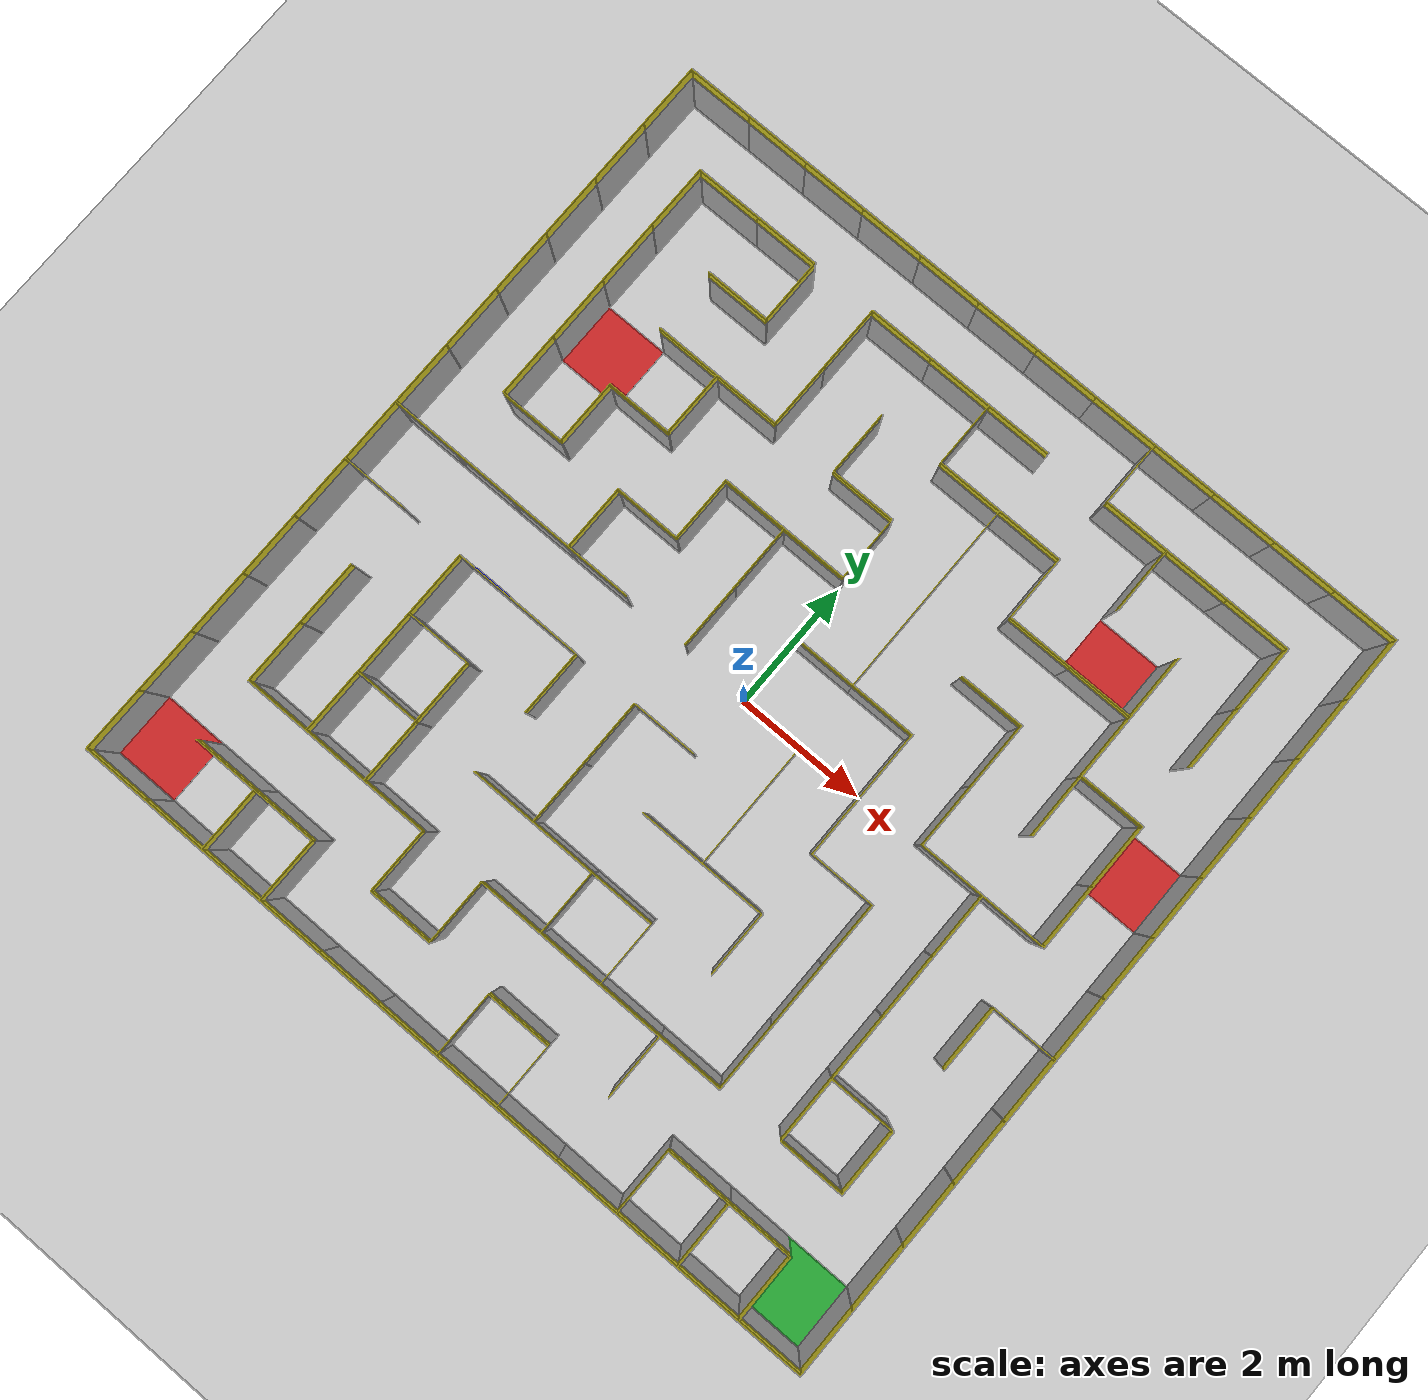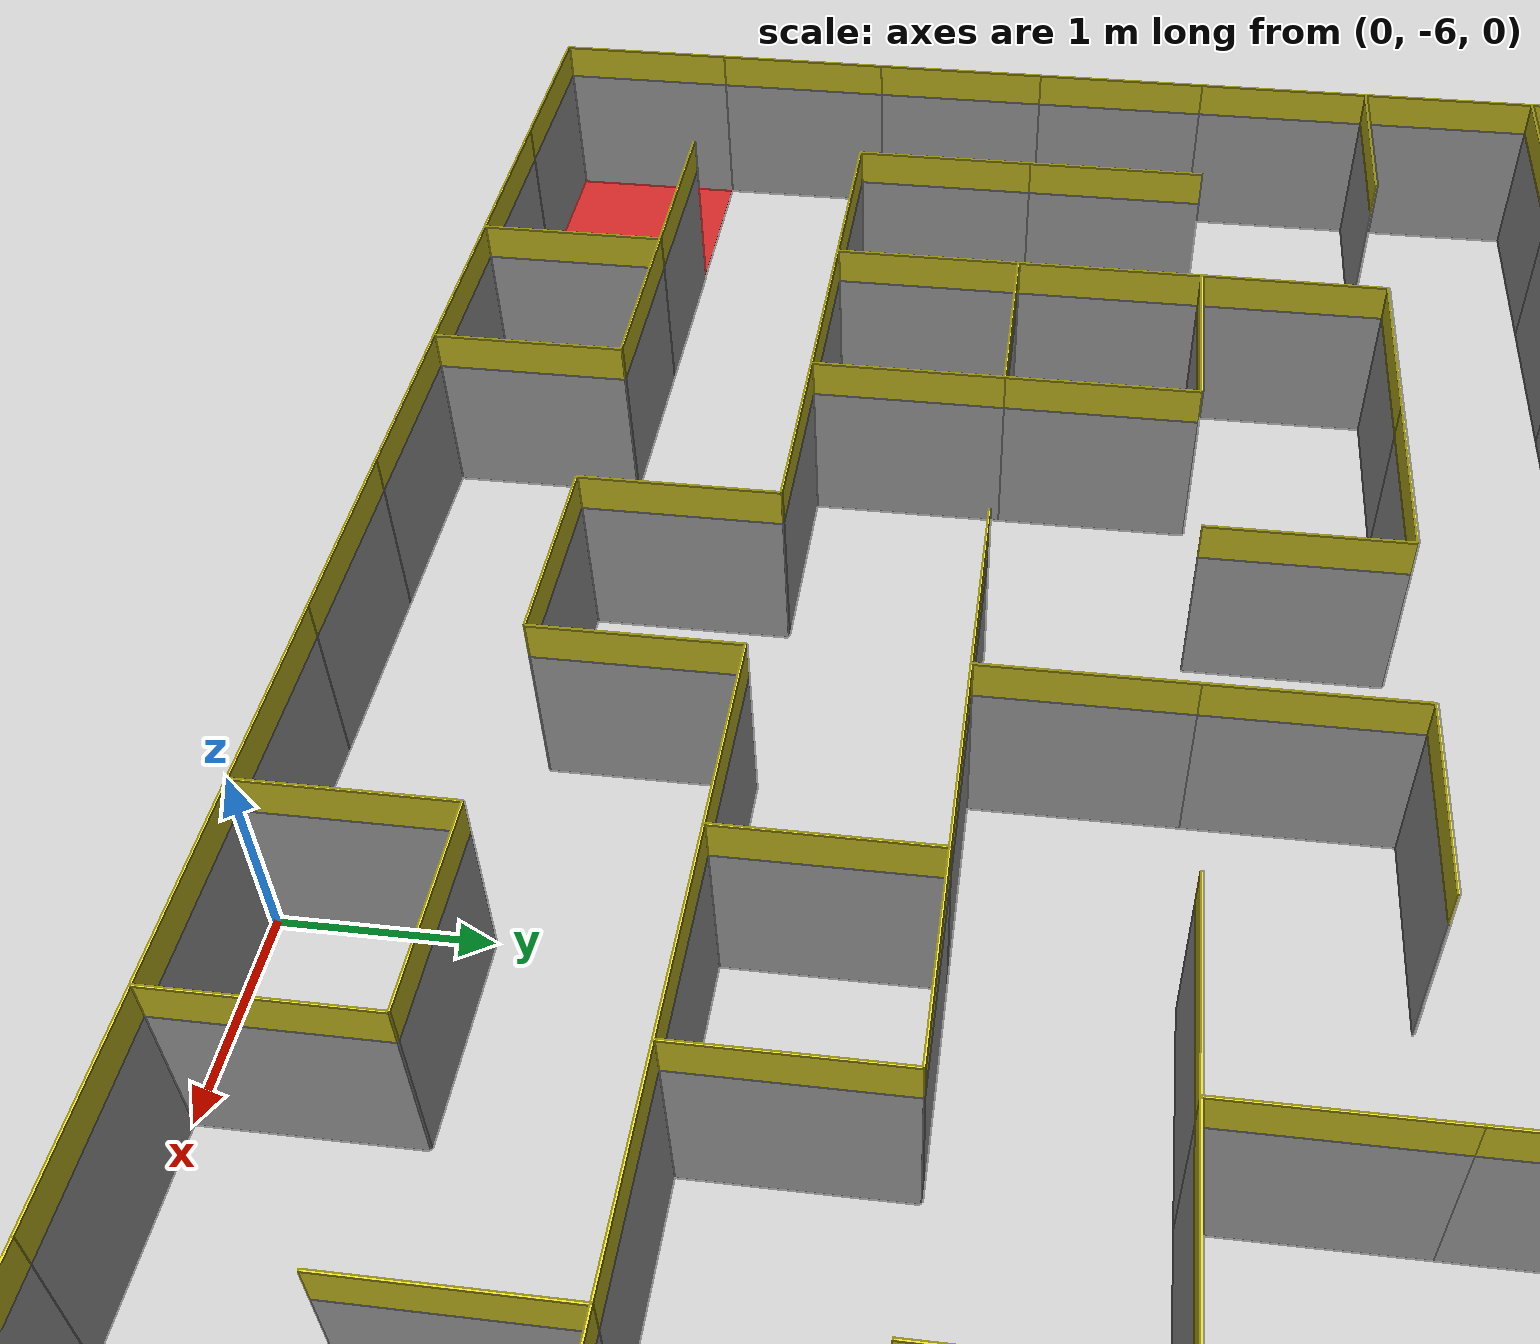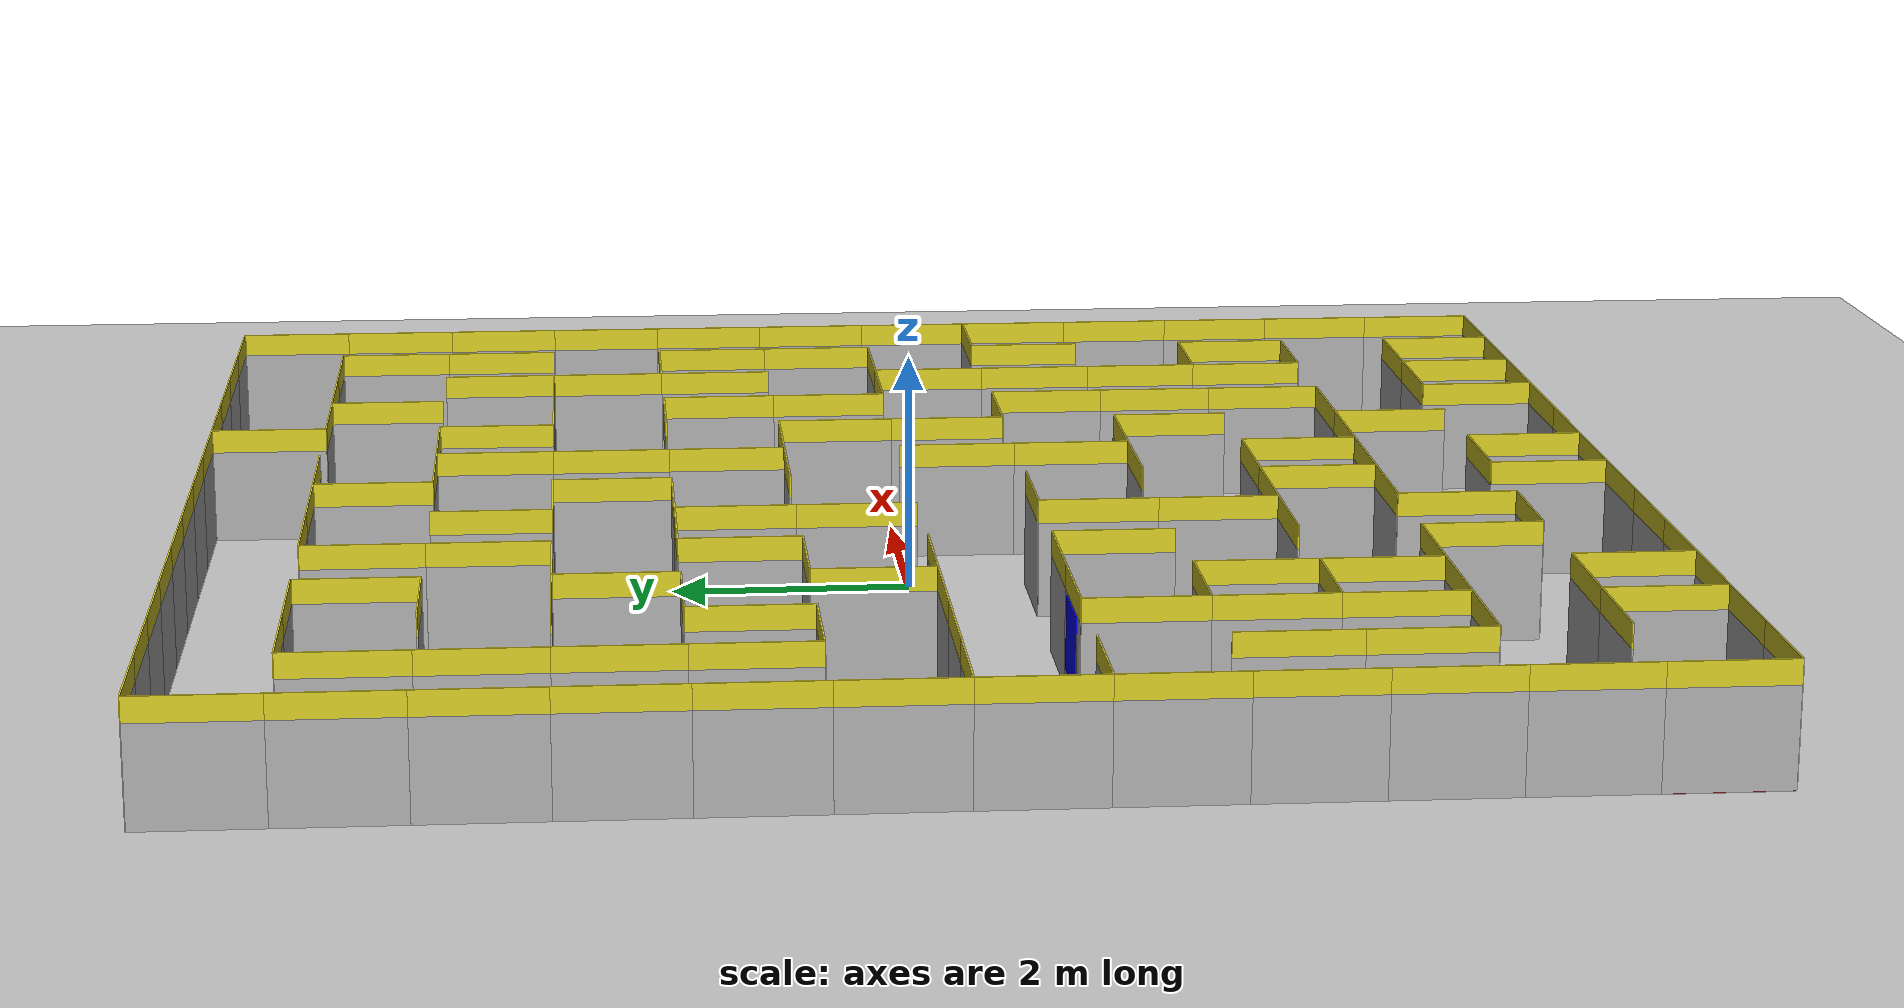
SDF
<sdf version='1.6'>
  <world name='default'>
    <gui fullscreen='0'>
      <plugin name='sample' filename='libregenerate_widget.so'/>
      <camera name='user_camera'>
        <pose frame=''>0.114113 8.57883 16.0652 -0 0.941797 -1.61726</pose>
        <view_controller>orbit</view_controller>
        <projection_type>perspective</projection_type>
      </camera>
    </gui>
    <light name='sun' type='directional'>
      <cast_shadows>0</cast_shadows>
      <pose frame=''>0 0 100 0 -0 0</pose>
      <diffuse>1 1 1 1</diffuse>
      <specular>0.2 0.2 0.2 1</specular>
      <attenuation>
        <range>1000</range>
        <constant>0.9</constant>
        <linear>0.01</linear>
        <quadratic>0.001</quadratic>
      </attenuation>
      <direction>-0.5 0.1 -0.9</direction>
    </light>
    <model name='ground_plane'>
      <static>1</static>
      <link name='link'>
        <collision name='collision'>
          <geometry>
            <plane>
              <normal>0 0 1</normal>
              <size>100 100</size>
            </plane>
          </geometry>
          <surface>
            <contact>
              <collide_bitmask>65535</collide_bitmask>
              <ode/>
            </contact>
            <friction>
              <ode>
                <mu>100</mu>
                <mu2>50</mu2>
              </ode>
              <torsional>
                <ode/>
              </torsional>
            </friction>
            <bounce/>
          </surface>
          <max_contacts>10</max_contacts>
        </collision>
        <visual name='visual'>
          <cast_shadows>0</cast_shadows>
          <geometry>
            <plane>
              <normal>0 0 1</normal>
              <size>100 100</size>
            </plane>
          </geometry>
          <material>
            <script>
              <uri>file://media/materials/scripts/gazebo.material</uri>
              <name>Gazebo/Grey</name>
            </script>
          </material>
        </visual>
        <self_collide>0</self_collide>
        <kinematic>0</kinematic>
      </link>
    </model>
    <model name='maze_base'>
      <static>1</static>
      <link name='hole_1'>
        <pose frame=''>5.5 1.5 0 0 -0 0</pose>
        <self_collide>0</self_collide>
        <kinematic>0</kinematic>
        <visual name='visual'>
          <pose frame=''>0 0 0.003 0 -0 0</pose>
          <geometry>
            <box>
              <size>1 1 0.005</size>
            </box>
          </geometry>
          <material>
            <script>
              <uri>file://media/materials/scripts/gazebo.material</uri>
              <name>Gazebo/Red</name>
            </script>
          </material>
        </visual>
      </link>
      <link name='hole_2'>
        <pose frame=''>3.5 3.5 0 0 -0 0</pose>
        <self_collide>0</self_collide>
        <kinematic>0</kinematic>
        <visual name='visual'>
          <pose frame=''>0 0 0.003 0 -0 0</pose>
          <geometry>
            <box>
              <size>1 1 0.005</size>
            </box>
          </geometry>
          <material>
            <script>
              <uri>file://media/materials/scripts/gazebo.material</uri>
              <name>Gazebo/Red</name>
            </script>
          </material>
        </visual>
      </link>
      <link name='hole_3'>
        <pose frame=''>-4.5 2.5 0 0 -0 0</pose>
        <self_collide>0</self_collide>
        <kinematic>0</kinematic>
        <visual name='visual'>
          <pose frame=''>0 0 0.003 0 -0 0</pose>
          <geometry>
            <box>
              <size>1 1 0.005</size>
            </box>
          </geometry>
          <material>
            <script>
              <uri>file://media/materials/scripts/gazebo.material</uri>
              <name>Gazebo/Red</name>
            </script>
          </material>
        </visual>
      </link>
      <link name='hole_4'>
        <pose frame=''>-5.5 -5.5 0 0 -0 0</pose>
        <self_collide>0</self_collide>
        <kinematic>0</kinematic>
        <visual name='visual'>
          <pose frame=''>0 0 0.003 0 -0 0</pose>
          <geometry>
            <box>
              <size>1 1 0.005</size>
            </box>
          </geometry>
          <material>
            <script>
              <uri>file://media/materials/scripts/gazebo.material</uri>
              <name>Gazebo/Red</name>
            </script>
          </material>
        </visual>
      </link>
      <link name='destination'>
        <pose frame=''>5.5 -5.5 0 0 -0 0</pose>
        <self_collide>0</self_collide>
        <kinematic>0</kinematic>
        <visual name='visual'>
          <pose frame=''>0 0 0.003 0 -0 0</pose>
          <geometry>
            <box>
              <size>1 1 0.005</size>
            </box>
          </geometry>
          <material>
            <script>
              <uri>file://media/materials/scripts/gazebo.material</uri>
              <name>Gazebo/Green</name>
            </script>
          </material>
        </visual>
      </link>
    </model>
    <gui fullscreen='0'>
      <plugin name='sample' filename='libregenerate_widget.so'/>
    </gui>
    <plugin name='maze' filename='libmaze_plugin.so'/>
    <physics name='default_physics' default='0' type='ode'>
      <max_step_size>0.01</max_step_size>
      <real_time_factor>1</real_time_factor>
      <real_time_update_rate>100</real_time_update_rate>
    </physics>
    <gravity>0 0 -9.8</gravity>
    <magnetic_field>6e-06 2.3e-05 -4.2e-05</magnetic_field>
    <atmosphere type='adiabatic'/>
    <scene>
      <ambient>0.4 0.4 0.4 1</ambient>
      <background>0.7 0.7 0.7 1</background>
      <shadows>1</shadows>
    </scene>
    <spherical_coordinates>
      <surface_model>EARTH_WGS84</surface_model>
      <latitude_deg>0</latitude_deg>
      <longitude_deg>0</longitude_deg>
      <elevation>0</elevation>
      <heading_deg>0</heading_deg>
    </spherical_coordinates>
    <model name='my_maze'>
      <link name='__default__'>
        <visual name='paint_v_0_1_S'>
          <pose frame=''>-4.5 5 0.905 0 -0 0</pose>
          <geometry>
            <box>
              <size>1 0.012 0.2</size>
            </box>
          </geometry>
          <material>
            <script>
              <name>Gazebo/Yellow</name>
              <uri>file://media/materials/scripts/gazebo.material</uri>
            </script>
          </material>
        </visual>
        <visual name='v_0_1_S'>
          <pose frame=''>-4.5 5 0.405 0 -0 0</pose>
          <geometry>
            <box>
              <size>1 0.012 0.8</size>
            </box>
          </geometry>
        </visual>
        <collision name='p_0_1_S'>
          <pose frame=''>-4.5 5 0.505 0 -0 0</pose>
          <geometry>
            <box>
              <size>1 0.012 1</size>
            </box>
          </geometry>
          <max_contacts>10</max_contacts>
          <surface>
            <contact>
              <ode/>
            </contact>
            <bounce/>
            <friction>
              <torsional>
                <ode/>
              </torsional>
              <ode/>
            </friction>
          </surface>
        </collision>
        <visual name='paint_v_0_2_S'>
          <pose frame=''>-3.5 5 0.905 0 -0 0</pose>
          <geometry>
            <box>
              <size>1 0.012 0.2</size>
            </box>
          </geometry>
          <material>
            <script>
              <name>Gazebo/Yellow</name>
              <uri>file://media/materials/scripts/gazebo.material</uri>
            </script>
          </material>
        </visual>
        <visual name='v_0_2_S'>
          <pose frame=''>-3.5 5 0.405 0 -0 0</pose>
          <geometry>
            <box>
              <size>1 0.012 0.8</size>
            </box>
          </geometry>
        </visual>
        <collision name='p_0_2_S'>
          <pose frame=''>-3.5 5 0.505 0 -0 0</pose>
          <geometry>
            <box>
              <size>1 0.012 1</size>
            </box>
          </geometry>
          <max_contacts>10</max_contacts>
          <surface>
            <contact>
              <ode/>
            </contact>
            <bounce/>
            <friction>
              <torsional>
                <ode/>
              </torsional>
              <ode/>
            </friction>
          </surface>
        </collision>
        <visual name='paint_v_0_4_S'>
          <pose frame=''>-1.5 5 0.905 0 -0 0</pose>
          <geometry>
            <box>
              <size>1 0.012 0.2</size>
            </box>
          </geometry>
          <material>
            <script>
              <name>Gazebo/Yellow</name>
              <uri>file://media/materials/scripts/gazebo.material</uri>
            </script>
          </material>
        </visual>
        <visual name='v_0_4_S'>
          <pose frame=''>-1.5 5 0.405 0 -0 0</pose>
          <geometry>
            <box>
              <size>1 0.012 0.8</size>
            </box>
          </geometry>
        </visual>
        <collision name='p_0_4_S'>
          <pose frame=''>-1.5 5 0.505 0 -0 0</pose>
          <geometry>
            <box>
              <size>1 0.012 1</size>
            </box>
          </geometry>
          <max_contacts>10</max_contacts>
          <surface>
            <contact>
              <ode/>
            </contact>
            <bounce/>
            <friction>
              <torsional>
                <ode/>
              </torsional>
              <ode/>
            </friction>
          </surface>
        </collision>
        <visual name='paint_v_0_5_S'>
          <pose frame=''>-0.5 5 0.905 0 -0 0</pose>
          <geometry>
            <box>
              <size>1 0.012 0.2</size>
            </box>
          </geometry>
          <material>
            <script>
              <name>Gazebo/Yellow</name>
              <uri>file://media/materials/scripts/gazebo.material</uri>
            </script>
          </material>
        </visual>
        <visual name='v_0_5_S'>
          <pose frame=''>-0.5 5 0.405 0 -0 0</pose>
          <geometry>
            <box>
              <size>1 0.012 0.8</size>
            </box>
          </geometry>
        </visual>
        <collision name='p_0_5_S'>
          <pose frame=''>-0.5 5 0.505 0 -0 0</pose>
          <geometry>
            <box>
              <size>1 0.012 1</size>
            </box>
          </geometry>
          <max_contacts>10</max_contacts>
          <surface>
            <contact>
              <ode/>
            </contact>
            <bounce/>
            <friction>
              <torsional>
                <ode/>
              </torsional>
              <ode/>
            </friction>
          </surface>
        </collision>
        <visual name='paint_v_0_6_S'>
          <pose frame=''>0.5 5 0.905 0 -0 0</pose>
          <geometry>
            <box>
              <size>1 0.012 0.2</size>
            </box>
          </geometry>
          <material>
            <script>
              <name>Gazebo/Yellow</name>
              <uri>file://media/materials/scripts/gazebo.material</uri>
            </script>
          </material>
        </visual>
        <visual name='v_0_6_S'>
          <pose frame=''>0.5 5 0.405 0 -0 0</pose>
          <geometry>
            <box>
              <size>1 0.012 0.8</size>
            </box>
          </geometry>
        </visual>
        <collision name='p_0_6_S'>
          <pose frame=''>0.5 5 0.505 0 -0 0</pose>
          <geometry>
            <box>
              <size>1 0.012 1</size>
            </box>
          </geometry>
          <max_contacts>10</max_contacts>
          <surface>
            <contact>
              <ode/>
            </contact>
            <bounce/>
            <friction>
              <torsional>
                <ode/>
              </torsional>
              <ode/>
            </friction>
          </surface>
        </collision>
        <visual name='paint_v_0_8_W'>
          <pose frame=''>2 5.5 0.905 0 -0 1.5708</pose>
          <geometry>
            <box>
              <size>1 0.012 0.2</size>
            </box>
          </geometry>
          <material>
            <script>
              <name>Gazebo/Yellow</name>
              <uri>file://media/materials/scripts/gazebo.material</uri>
            </script>
          </material>
        </visual>
        <visual name='v_0_8_W'>
          <pose frame=''>2 5.5 0.405 0 -0 1.5708</pose>
          <geometry>
            <box>
              <size>1 0.012 0.8</size>
            </box>
          </geometry>
        </visual>
        <collision name='p_0_8_W'>
          <pose frame=''>2 5.5 0.505 0 -0 1.5708</pose>
          <geometry>
            <box>
              <size>1 0.012 1</size>
            </box>
          </geometry>
          <max_contacts>10</max_contacts>
          <surface>
            <contact>
              <ode/>
            </contact>
            <bounce/>
            <friction>
              <torsional>
                <ode/>
              </torsional>
              <ode/>
            </friction>
          </surface>
        </collision>
        <visual name='paint_v_0_8_S'>
          <pose frame=''>2.5 5 0.905 0 -0 0</pose>
          <geometry>
            <box>
              <size>1 0.012 0.2</size>
            </box>
          </geometry>
          <material>
            <script>
              <name>Gazebo/Yellow</name>
              <uri>file://media/materials/scripts/gazebo.material</uri>
            </script>
          </material>
        </visual>
        <visual name='v_0_8_S'>
          <pose frame=''>2.5 5 0.405 0 -0 0</pose>
          <geometry>
            <box>
              <size>1 0.012 0.8</size>
            </box>
          </geometry>
        </visual>
        <collision name='p_0_8_S'>
          <pose frame=''>2.5 5 0.505 0 -0 0</pose>
          <geometry>
            <box>
              <size>1 0.012 1</size>
            </box>
          </geometry>
          <max_contacts>10</max_contacts>
          <surface>
            <contact>
              <ode/>
            </contact>
            <bounce/>
            <friction>
              <torsional>
                <ode/>
              </torsional>
              <ode/>
            </friction>
          </surface>
        </collision>
        <visual name='paint_v_0_9_S'>
          <pose frame=''>3.5 5 0.905 0 -0 0</pose>
          <geometry>
            <box>
              <size>1 0.012 0.2</size>
            </box>
          </geometry>
          <material>
            <script>
              <name>Gazebo/Yellow</name>
              <uri>file://media/materials/scripts/gazebo.material</uri>
            </script>
          </material>
        </visual>
        <visual name='v_0_9_S'>
          <pose frame=''>3.5 5 0.405 0 -0 0</pose>
          <geometry>
            <box>
              <size>1 0.012 0.8</size>
            </box>
          </geometry>
        </visual>
        <collision name='p_0_9_S'>
          <pose frame=''>3.5 5 0.505 0 -0 0</pose>
          <geometry>
            <box>
              <size>1 0.012 1</size>
            </box>
          </geometry>
          <max_contacts>10</max_contacts>
          <surface>
            <contact>
              <ode/>
            </contact>
            <bounce/>
            <friction>
              <torsional>
                <ode/>
              </torsional>
              <ode/>
            </friction>
          </surface>
        </collision>
        <visual name='paint_v_0_10_S'>
          <pose frame=''>4.5 5 0.905 0 -0 0</pose>
          <geometry>
            <box>
              <size>1 0.012 0.2</size>
            </box>
          </geometry>
          <material>
            <script>
              <name>Gazebo/Yellow</name>
              <uri>file://media/materials/scripts/gazebo.material</uri>
            </script>
          </material>
        </visual>
        <visual name='v_0_10_S'>
          <pose frame=''>4.5 5 0.405 0 -0 0</pose>
          <geometry>
            <box>
              <size>1 0.012 0.8</size>
            </box>
          </geometry>
        </visual>
        <collision name='p_0_10_S'>
          <pose frame=''>4.5 5 0.505 0 -0 0</pose>
          <geometry>
            <box>
              <size>1 0.012 1</size>
            </box>
          </geometry>
          <max_contacts>10</max_contacts>
          <surface>
            <contact>
              <ode/>
            </contact>
            <bounce/>
            <friction>
              <torsional>
                <ode/>
              </torsional>
              <ode/>
            </friction>
          </surface>
        </collision>
        <visual name='paint_v_0_0_W'>
          <pose frame=''>-6 5.5 0.905 0 -0 1.5708</pose>
          <geometry>
            <box>
              <size>1 0.012 0.2</size>
            </box>
          </geometry>
          <material>
            <script>
              <name>Gazebo/Yellow</name>
              <uri>file://media/materials/scripts/gazebo.material</uri>
            </script>
          </material>
        </visual>
        <visual name='v_0_0_W'>
          <pose frame=''>-6 5.5 0.405 0 -0 1.5708</pose>
          <geometry>
            <box>
              <size>1 0.012 0.8</size>
            </box>
          </geometry>
        </visual>
        <collision name='p_0_0_W'>
          <pose frame=''>-6 5.5 0.505 0 -0 1.5708</pose>
          <geometry>
            <box>
              <size>1 0.012 1</size>
            </box>
          </geometry>
          <max_contacts>10</max_contacts>
          <surface>
            <contact>
              <ode/>
            </contact>
            <bounce/>
            <friction>
              <torsional>
                <ode/>
              </torsional>
              <ode/>
            </friction>
          </surface>
        </collision>
        <visual name='paint_v_0_11_E'>
          <pose frame=''>6 5.5 0.905 0 -0 1.5708</pose>
          <geometry>
            <box>
              <size>1 0.012 0.2</size>
            </box>
          </geometry>
          <material>
            <script>
              <name>Gazebo/Yellow</name>
              <uri>file://media/materials/scripts/gazebo.material</uri>
            </script>
          </material>
        </visual>
        <visual name='v_0_11_E'>
          <pose frame=''>6 5.5 0.405 0 -0 1.5708</pose>
          <geometry>
            <box>
              <size>1 0.012 0.8</size>
            </box>
          </geometry>
        </visual>
        <collision name='p_0_11_E'>
          <pose frame=''>6 5.5 0.505 0 -0 1.5708</pose>
          <geometry>
            <box>
              <size>1 0.012 1</size>
            </box>
          </geometry>
          <max_contacts>10</max_contacts>
          <surface>
            <contact>
              <ode/>
            </contact>
            <bounce/>
            <friction>
              <torsional>
                <ode/>
              </torsional>
              <ode/>
            </friction>
          </surface>
        </collision>
        <visual name='paint_v_0_0_N'>
          <pose frame=''>-5.5 6 0.905 0 -0 0</pose>
          <geometry>
            <box>
              <size>1 0.012 0.2</size>
            </box>
          </geometry>
          <material>
            <script>
              <name>Gazebo/Yellow</name>
              <uri>file://media/materials/scripts/gazebo.material</uri>
            </script>
          </material>
        </visual>
        <visual name='v_0_0_N'>
          <pose frame=''>-5.5 6 0.405 0 -0 0</pose>
          <geometry>
            <box>
              <size>1 0.012 0.8</size>
            </box>
          </geometry>
        </visual>
        <collision name='p_0_0_N'>
          <pose frame=''>-5.5 6 0.505 0 -0 0</pose>
          <geometry>
            <box>
              <size>1 0.012 1</size>
            </box>
          </geometry>
          <max_contacts>10</max_contacts>
          <surface>
            <contact>
              <ode/>
            </contact>
            <bounce/>
            <friction>
              <torsional>
                <ode/>
              </torsional>
              <ode/>
            </friction>
          </surface>
        </collision>
        <visual name='paint_v_11_0_S'>
          <pose frame=''>-5.5 -6 0.905 0 -0 0</pose>
          <geometry>
            <box>
              <size>1 0.012 0.2</size>
            </box>
          </geometry>
          <material>
            <script>
              <name>Gazebo/Yellow</name>
              <uri>file://media/materials/scripts/gazebo.material</uri>
            </script>
          </material>
        </visual>
        <visual name='v_11_0_S'>
          <pose frame=''>-5.5 -6 0.405 0 -0 0</pose>
          <geometry>
            <box>
              <size>1 0.012 0.8</size>
            </box>
          </geometry>
        </visual>
        <collision name='p_11_0_S'>
          <pose frame=''>-5.5 -6 0.505 0 -0 0</pose>
          <geometry>
            <box>
              <size>1 0.012 1</size>
            </box>
          </geometry>
          <max_contacts>10</max_contacts>
          <surface>
            <contact>
              <ode/>
            </contact>
            <bounce/>
            <friction>
              <torsional>
                <ode/>
              </torsional>
              <ode/>
            </friction>
          </surface>
        </collision>
        <visual name='paint_v_1_0_W'>
          <pose frame=''>-6 4.5 0.905 0 -0 1.5708</pose>
          <geometry>
            <box>
              <size>1 0.012 0.2</size>
            </box>
          </geometry>
          <material>
            <script>
              <name>Gazebo/Yellow</name>
              <uri>file://media/materials/scripts/gazebo.material</uri>
            </script>
          </material>
        </visual>
        <visual name='v_1_0_W'>
          <pose frame=''>-6 4.5 0.405 0 -0 1.5708</pose>
          <geometry>
            <box>
              <size>1 0.012 0.8</size>
            </box>
          </geometry>
        </visual>
        <collision name='p_1_0_W'>
          <pose frame=''>-6 4.5 0.505 0 -0 1.5708</pose>
          <geometry>
            <box>
              <size>1 0.012 1</size>
            </box>
          </geometry>
          <max_contacts>10</max_contacts>
          <surface>
            <contact>
              <ode/>
            </contact>
            <bounce/>
            <friction>
              <torsional>
                <ode/>
              </torsional>
              <ode/>
            </friction>
          </surface>
        </collision>
        <visual name='paint_v_1_1_W'>
          <pose frame=''>-5 4.5 0.905 0 -0 1.5708</pose>
          <geometry>
            <box>
              <size>1 0.012 0.2</size>
            </box>
          </geometry>
          <material>
            <script>
              <name>Gazebo/Yellow</name>
              <uri>file://media/materials/scripts/gazebo.material</uri>
            </script>
          </material>
        </visual>
        <visual name='v_1_1_W'>
          <pose frame=''>-5 4.5 0.405 0 -0 1.5708</pose>
          <geometry>
            <box>
              <size>1 0.012 0.8</size>
            </box>
          </geometry>
        </visual>
        <collision name='p_1_1_W'>
          <pose frame=''>-5 4.5 0.505 0 -0 1.5708</pose>
          <geometry>
            <box>
              <size>1 0.012 1</size>
            </box>
          </geometry>
          <max_contacts>10</max_contacts>
          <surface>
            <contact>
              <ode/>
            </contact>
            <bounce/>
            <friction>
              <torsional>
                <ode/>
              </torsional>
              <ode/>
            </friction>
          </surface>
        </collision>
        <visual name='paint_v_1_2_S'>
          <pose frame=''>-3.5 4 0.905 0 -0 0</pose>
          <geometry>
            <box>
              <size>1 0.012 0.2</size>
            </box>
          </geometry>
          <material>
            <script>
              <name>Gazebo/Yellow</name>
              <uri>file://media/materials/scripts/gazebo.material</uri>
            </script>
          </material>
        </visual>
        <visual name='v_1_2_S'>
          <pose frame=''>-3.5 4 0.405 0 -0 0</pose>
          <geometry>
            <box>
              <size>1 0.012 0.8</size>
            </box>
          </geometry>
        </visual>
        <collision name='p_1_2_S'>
          <pose frame=''>-3.5 4 0.505 0 -0 0</pose>
          <geometry>
            <box>
              <size>1 0.012 1</size>
            </box>
          </geometry>
          <max_contacts>10</max_contacts>
          <surface>
            <contact>
              <ode/>
            </contact>
            <bounce/>
            <friction>
              <torsional>
                <ode/>
              </torsional>
              <ode/>
            </friction>
          </surface>
        </collision>
        <visual name='paint_v_1_3_W'>
          <pose frame=''>-3 4.5 0.905 0 -0 1.5708</pose>
          <geometry>
            <box>
              <size>1 0.012 0.2</size>
            </box>
          </geometry>
          <material>
            <script>
              <name>Gazebo/Yellow</name>
              <uri>file://media/materials/scripts/gazebo.material</uri>
            </script>
          </material>
        </visual>
        <visual name='v_1_3_W'>
          <pose frame=''>-3 4.5 0.405 0 -0 1.5708</pose>
          <geometry>
            <box>
              <size>1 0.012 0.8</size>
            </box>
          </geometry>
        </visual>
        <collision name='p_1_3_W'>
          <pose frame=''>-3 4.5 0.505 0 -0 1.5708</pose>
          <geometry>
            <box>
              <size>1 0.012 1</size>
            </box>
          </geometry>
          <max_contacts>10</max_contacts>
          <surface>
            <contact>
              <ode/>
            </contact>
            <bounce/>
            <friction>
              <torsional>
                <ode/>
              </torsional>
              <ode/>
            </friction>
          </surface>
        </collision>
        <visual name='paint_v_1_4_W'>
          <pose frame=''>-2 4.5 0.905 0 -0 1.5708</pose>
          <geometry>
            <box>
              <size>1 0.012 0.2</size>
            </box>
          </geometry>
          <material>
            <script>
              <name>Gazebo/Yellow</name>
              <uri>file://media/materials/scripts/gazebo.material</uri>
            </script>
          </material>
        </visual>
        <visual name='v_1_4_W'>
          <pose frame=''>-2 4.5 0.405 0 -0 1.5708</pose>
          <geometry>
            <box>
              <size>1 0.012 0.8</size>
            </box>
          </geometry>
        </visual>
        <collision name='p_1_4_W'>
          <pose frame=''>-2 4.5 0.505 0 -0 1.5708</pose>
          <geometry>
            <box>
              <size>1 0.012 1</size>
            </box>
          </geometry>
          <max_contacts>10</max_contacts>
          <surface>
            <contact>
              <ode/>
            </contact>
            <bounce/>
            <friction>
              <torsional>
                <ode/>
              </torsional>
              <ode/>
            </friction>
          </surface>
        </collision>
        <visual name='paint_v_1_6_W'>
          <pose frame=''>0 4.5 0.905 0 -0 1.5708</pose>
          <geometry>
            <box>
              <size>1 0.012 0.2</size>
            </box>
          </geometry>
          <material>
            <script>
              <name>Gazebo/Yellow</name>
              <uri>file://media/materials/scripts/gazebo.material</uri>
            </script>
          </material>
        </visual>
        <visual name='v_1_6_W'>
          <pose frame=''>0 4.5 0.405 0 -0 1.5708</pose>
          <geometry>
            <box>
              <size>1 0.012 0.8</size>
            </box>
          </geometry>
        </visual>
        <collision name='p_1_6_W'>
          <pose frame=''>0 4.5 0.505 0 -0 1.5708</pose>
          <geometry>
            <box>
              <size>1 0.012 1</size>
            </box>
          </geometry>
          <max_contacts>10</max_contacts>
          <surface>
            <contact>
              <ode/>
            </contact>
            <bounce/>
            <friction>
              <torsional>
                <ode/>
              </torsional>
              <ode/>
            </friction>
          </surface>
        </collision>
        <visual name='paint_v_1_6_S'>
          <pose frame=''>0.5 4 0.905 0 -0 0</pose>
          <geometry>
            <box>
              <size>1 0.012 0.2</size>
            </box>
          </geometry>
          <material>
            <script>
              <name>Gazebo/Yellow</name>
              <uri>file://media/materials/scripts/gazebo.material</uri>
            </script>
          </material>
        </visual>
        <visual name='v_1_6_S'>
          <pose frame=''>0.5 4 0.405 0 -0 0</pose>
          <geometry>
            <box>
              <size>1 0.012 0.8</size>
            </box>
          </geometry>
        </visual>
        <collision name='p_1_6_S'>
          <pose frame=''>0.5 4 0.505 0 -0 0</pose>
          <geometry>
            <box>
              <size>1 0.012 1</size>
            </box>
          </geometry>
          <max_contacts>10</max_contacts>
          <surface>
            <contact>
              <ode/>
            </contact>
            <bounce/>
            <friction>
              <torsional>
                <ode/>
              </torsional>
              <ode/>
            </friction>
          </surface>
        </collision>
        <visual name='paint_v_1_7_S'>
          <pose frame=''>1.5 4 0.905 0 -0 0</pose>
          <geometry>
            <box>
              <size>1 0.012 0.2</size>
            </box>
          </geometry>
          <material>
            <script>
              <name>Gazebo/Yellow</name>
              <uri>file://media/materials/scripts/gazebo.material</uri>
            </script>
          </material>
        </visual>
        <visual name='v_1_7_S'>
          <pose frame=''>1.5 4 0.405 0 -0 0</pose>
          <geometry>
            <box>
              <size>1 0.012 0.8</size>
            </box>
          </geometry>
        </visual>
        <collision name='p_1_7_S'>
          <pose frame=''>1.5 4 0.505 0 -0 0</pose>
          <geometry>
            <box>
              <size>1 0.012 1</size>
            </box>
          </geometry>
          <max_contacts>10</max_contacts>
          <surface>
            <contact>
              <ode/>
            </contact>
            <bounce/>
            <friction>
              <torsional>
                <ode/>
              </torsional>
              <ode/>
            </friction>
          </surface>
        </collision>
        <visual name='paint_v_1_9_W'>
          <pose frame=''>3 4.5 0.905 0 -0 1.5708</pose>
          <geometry>
            <box>
              <size>1 0.012 0.2</size>
            </box>
          </geometry>
          <material>
            <script>
              <name>Gazebo/Yellow</name>
              <uri>file://media/materials/scripts/gazebo.material</uri>
            </script>
          </material>
        </visual>
        <visual name='v_1_9_W'>
          <pose frame=''>3 4.5 0.405 0 -0 1.5708</pose>
          <geometry>
            <box>
              <size>1 0.012 0.8</size>
            </box>
          </geometry>
        </visual>
        <collision name='p_1_9_W'>
          <pose frame=''>3 4.5 0.505 0 -0 1.5708</pose>
          <geometry>
            <box>
              <size>1 0.012 1</size>
            </box>
          </geometry>
          <max_contacts>10</max_contacts>
          <surface>
            <contact>
              <ode/>
            </contact>
            <bounce/>
            <friction>
              <torsional>
                <ode/>
              </torsional>
              <ode/>
            </friction>
          </surface>
        </collision>
        <visual name='paint_v_1_11_W'>
          <pose frame=''>5 4.5 0.905 0 -0 1.5708</pose>
          <geometry>
            <box>
              <size>1 0.012 0.2</size>
            </box>
          </geometry>
          <material>
            <script>
              <name>Gazebo/Yellow</name>
              <uri>file://media/materials/scripts/gazebo.material</uri>
            </script>
          </material>
        </visual>
        <visual name='v_1_11_W'>
          <pose frame=''>5 4.5 0.405 0 -0 1.5708</pose>
          <geometry>
            <box>
              <size>1 0.012 0.8</size>
            </box>
          </geometry>
        </visual>
        <collision name='p_1_11_W'>
          <pose frame=''>5 4.5 0.505 0 -0 1.5708</pose>
          <geometry>
            <box>
              <size>1 0.012 1</size>
            </box>
          </geometry>
          <max_contacts>10</max_contacts>
          <surface>
            <contact>
              <ode/>
            </contact>
            <bounce/>
            <friction>
              <torsional>
                <ode/>
              </torsional>
              <ode/>
            </friction>
          </surface>
        </collision>
        <visual name='paint_v_1_0_W'>
          <pose frame=''>-6 4.5 0.905 0 -0 1.5708</pose>
          <geometry>
            <box>
              <size>1 0.012 0.2</size>
            </box>
          </geometry>
          <material>
            <script>
              <name>Gazebo/Yellow</name>
              <uri>file://media/materials/scripts/gazebo.material</uri>
            </script>
          </material>
        </visual>
        <visual name='v_1_0_W'>
          <pose frame=''>-6 4.5 0.405 0 -0 1.5708</pose>
          <geometry>
            <box>
              <size>1 0.012 0.8</size>
            </box>
          </geometry>
        </visual>
        <collision name='p_1_0_W'>
          <pose frame=''>-6 4.5 0.505 0 -0 1.5708</pose>
          <geometry>
            <box>
              <size>1 0.012 1</size>
            </box>
          </geometry>
          <max_contacts>10</max_contacts>
          <surface>
            <contact>
              <ode/>
            </contact>
            <bounce/>
            <friction>
              <torsional>
                <ode/>
              </torsional>
              <ode/>
            </friction>
          </surface>
        </collision>
        <visual name='paint_v_1_11_E'>
          <pose frame=''>6 4.5 0.905 0 -0 1.5708</pose>
          <geometry>
            <box>
              <size>1 0.012 0.2</size>
            </box>
          </geometry>
          <material>
            <script>
              <name>Gazebo/Yellow</name>
              <uri>file://media/materials/scripts/gazebo.material</uri>
            </script>
          </material>
        </visual>
        <visual name='v_1_11_E'>
          <pose frame=''>6 4.5 0.405 0 -0 1.5708</pose>
          <geometry>
            <box>
              <size>1 0.012 0.8</size>
            </box>
          </geometry>
        </visual>
        <collision name='p_1_11_E'>
          <pose frame=''>6 4.5 0.505 0 -0 1.5708</pose>
          <geometry>
            <box>
              <size>1 0.012 1</size>
            </box>
          </geometry>
          <max_contacts>10</max_contacts>
          <surface>
            <contact>
              <ode/>
            </contact>
            <bounce/>
            <friction>
              <torsional>
                <ode/>
              </torsional>
              <ode/>
            </friction>
          </surface>
        </collision>
        <visual name='paint_v_0_1_N'>
          <pose frame=''>-4.5 6 0.905 0 -0 0</pose>
          <geometry>
            <box>
              <size>1 0.012 0.2</size>
            </box>
          </geometry>
          <material>
            <script>
              <name>Gazebo/Yellow</name>
              <uri>file://media/materials/scripts/gazebo.material</uri>
            </script>
          </material>
        </visual>
        <visual name='v_0_1_N'>
          <pose frame=''>-4.5 6 0.405 0 -0 0</pose>
          <geometry>
            <box>
              <size>1 0.012 0.8</size>
            </box>
          </geometry>
        </visual>
        <collision name='p_0_1_N'>
          <pose frame=''>-4.5 6 0.505 0 -0 0</pose>
          <geometry>
            <box>
              <size>1 0.012 1</size>
            </box>
          </geometry>
          <max_contacts>10</max_contacts>
          <surface>
            <contact>
              <ode/>
            </contact>
            <bounce/>
            <friction>
              <torsional>
                <ode/>
              </torsional>
              <ode/>
            </friction>
          </surface>
        </collision>
        <visual name='paint_v_11_1_S'>
          <pose frame=''>-4.5 -6 0.905 0 -0 0</pose>
          <geometry>
            <box>
              <size>1 0.012 0.2</size>
            </box>
          </geometry>
          <material>
            <script>
              <name>Gazebo/Yellow</name>
              <uri>file://media/materials/scripts/gazebo.material</uri>
            </script>
          </material>
        </visual>
        <visual name='v_11_1_S'>
          <pose frame=''>-4.5 -6 0.405 0 -0 0</pose>
          <geometry>
            <box>
              <size>1 0.012 0.8</size>
            </box>
          </geometry>
        </visual>
        <collision name='p_11_1_S'>
          <pose frame=''>-4.5 -6 0.505 0 -0 0</pose>
          <geometry>
            <box>
              <size>1 0.012 1</size>
            </box>
          </geometry>
          <max_contacts>10</max_contacts>
          <surface>
            <contact>
              <ode/>
            </contact>
            <bounce/>
            <friction>
              <torsional>
                <ode/>
              </torsional>
              <ode/>
            </friction>
          </surface>
        </collision>
        <visual name='paint_v_2_1_W'>
          <pose frame=''>-5 3.5 0.905 0 -0 1.5708</pose>
          <geometry>
            <box>
              <size>1 0.012 0.2</size>
            </box>
          </geometry>
          <material>
            <script>
              <name>Gazebo/Yellow</name>
              <uri>file://media/materials/scripts/gazebo.material</uri>
            </script>
          </material>
        </visual>
        <visual name='v_2_1_W'>
          <pose frame=''>-5 3.5 0.405 0 -0 1.5708</pose>
          <geometry>
            <box>
              <size>1 0.012 0.8</size>
            </box>
          </geometry>
        </visual>
        <collision name='p_2_1_W'>
          <pose frame=''>-5 3.5 0.505 0 -0 1.5708</pose>
          <geometry>
            <box>
              <size>1 0.012 1</size>
            </box>
          </geometry>
          <max_contacts>10</max_contacts>
          <surface>
            <contact>
              <ode/>
            </contact>
            <bounce/>
            <friction>
              <torsional>
                <ode/>
              </torsional>
              <ode/>
            </friction>
          </surface>
        </collision>
        <visual name='paint_v_2_2_S'>
          <pose frame=''>-3.5 3 0.905 0 -0 0</pose>
          <geometry>
            <box>
              <size>1 0.012 0.2</size>
            </box>
          </geometry>
          <material>
            <script>
              <name>Gazebo/Yellow</name>
              <uri>file://media/materials/scripts/gazebo.material</uri>
            </script>
          </material>
        </visual>
        <visual name='v_2_2_S'>
          <pose frame=''>-3.5 3 0.405 0 -0 0</pose>
          <geometry>
            <box>
              <size>1 0.012 0.8</size>
            </box>
          </geometry>
        </visual>
        <collision name='p_2_2_S'>
          <pose frame=''>-3.5 3 0.505 0 -0 0</pose>
          <geometry>
            <box>
              <size>1 0.012 1</size>
            </box>
          </geometry>
          <max_contacts>10</max_contacts>
          <surface>
            <contact>
              <ode/>
            </contact>
            <bounce/>
            <friction>
              <torsional>
                <ode/>
              </torsional>
              <ode/>
            </friction>
          </surface>
        </collision>
        <visual name='paint_v_2_3_S'>
          <pose frame=''>-2.5 3 0.905 0 -0 0</pose>
          <geometry>
            <box>
              <size>1 0.012 0.2</size>
            </box>
          </geometry>
          <material>
            <script>
              <name>Gazebo/Yellow</name>
              <uri>file://media/materials/scripts/gazebo.material</uri>
            </script>
          </material>
        </visual>
        <visual name='v_2_3_S'>
          <pose frame=''>-2.5 3 0.405 0 -0 0</pose>
          <geometry>
            <box>
              <size>1 0.012 0.8</size>
            </box>
          </geometry>
        </visual>
        <collision name='p_2_3_S'>
          <pose frame=''>-2.5 3 0.505 0 -0 0</pose>
          <geometry>
            <box>
              <size>1 0.012 1</size>
            </box>
          </geometry>
          <max_contacts>10</max_contacts>
          <surface>
            <contact>
              <ode/>
            </contact>
            <bounce/>
            <friction>
              <torsional>
                <ode/>
              </torsional>
              <ode/>
            </friction>
          </surface>
        </collision>
        <visual name='paint_v_2_4_W'>
          <pose frame=''>-2 3.5 0.905 0 -0 1.5708</pose>
          <geometry>
            <box>
              <size>1 0.012 0.2</size>
            </box>
          </geometry>
          <material>
            <script>
              <name>Gazebo/Yellow</name>
              <uri>file://media/materials/scripts/gazebo.material</uri>
            </script>
          </material>
        </visual>
        <visual name='v_2_4_W'>
          <pose frame=''>-2 3.5 0.405 0 -0 1.5708</pose>
          <geometry>
            <box>
              <size>1 0.012 0.8</size>
            </box>
          </geometry>
        </visual>
        <collision name='p_2_4_W'>
          <pose frame=''>-2 3.5 0.505 0 -0 1.5708</pose>
          <geometry>
            <box>
              <size>1 0.012 1</size>
            </box>
          </geometry>
          <max_contacts>10</max_contacts>
          <surface>
            <contact>
              <ode/>
            </contact>
            <bounce/>
            <friction>
              <torsional>
                <ode/>
              </torsional>
              <ode/>
            </friction>
          </surface>
        </collision>
        <visual name='paint_v_2_5_W'>
          <pose frame=''>-1 3.5 0.905 0 -0 1.5708</pose>
          <geometry>
            <box>
              <size>1 0.012 0.2</size>
            </box>
          </geometry>
          <material>
            <script>
              <name>Gazebo/Yellow</name>
              <uri>file://media/materials/scripts/gazebo.material</uri>
            </script>
          </material>
        </visual>
        <visual name='v_2_5_W'>
          <pose frame=''>-1 3.5 0.405 0 -0 1.5708</pose>
          <geometry>
            <box>
              <size>1 0.012 0.8</size>
            </box>
          </geometry>
        </visual>
        <collision name='p_2_5_W'>
          <pose frame=''>-1 3.5 0.505 0 -0 1.5708</pose>
          <geometry>
            <box>
              <size>1 0.012 1</size>
            </box>
          </geometry>
          <max_contacts>10</max_contacts>
          <surface>
            <contact>
              <ode/>
            </contact>
            <bounce/>
            <friction>
              <torsional>
                <ode/>
              </torsional>
              <ode/>
            </friction>
          </surface>
        </collision>
        <visual name='paint_v_2_5_S'>
          <pose frame=''>-0.5 3 0.905 0 -0 0</pose>
          <geometry>
            <box>
              <size>1 0.012 0.2</size>
            </box>
          </geometry>
          <material>
            <script>
              <name>Gazebo/Yellow</name>
              <uri>file://media/materials/scripts/gazebo.material</uri>
            </script>
          </material>
        </visual>
        <visual name='v_2_5_S'>
          <pose frame=''>-0.5 3 0.405 0 -0 0</pose>
          <geometry>
            <box>
              <size>1 0.012 0.8</size>
            </box>
          </geometry>
        </visual>
        <collision name='p_2_5_S'>
          <pose frame=''>-0.5 3 0.505 0 -0 0</pose>
          <geometry>
            <box>
              <size>1 0.012 1</size>
            </box>
          </geometry>
          <max_contacts>10</max_contacts>
          <surface>
            <contact>
              <ode/>
            </contact>
            <bounce/>
            <friction>
              <torsional>
                <ode/>
              </torsional>
              <ode/>
            </friction>
          </surface>
        </collision>
        <visual name='paint_v_2_7_W'>
          <pose frame=''>1 3.5 0.905 0 -0 1.5708</pose>
          <geometry>
            <box>
              <size>1 0.012 0.2</size>
            </box>
          </geometry>
          <material>
            <script>
              <name>Gazebo/Yellow</name>
              <uri>file://media/materials/scripts/gazebo.material</uri>
            </script>
          </material>
        </visual>
        <visual name='v_2_7_W'>
          <pose frame=''>1 3.5 0.405 0 -0 1.5708</pose>
          <geometry>
            <box>
              <size>1 0.012 0.8</size>
            </box>
          </geometry>
        </visual>
        <collision name='p_2_7_W'>
          <pose frame=''>1 3.5 0.505 0 -0 1.5708</pose>
          <geometry>
            <box>
              <size>1 0.012 1</size>
            </box>
          </geometry>
          <max_contacts>10</max_contacts>
          <surface>
            <contact>
              <ode/>
            </contact>
            <bounce/>
            <friction>
              <torsional>
                <ode/>
              </torsional>
              <ode/>
            </friction>
          </surface>
        </collision>
        <visual name='paint_v_2_8_W'>
          <pose frame=''>2 3.5 0.905 0 -0 1.5708</pose>
          <geometry>
            <box>
              <size>1 0.012 0.2</size>
            </box>
          </geometry>
          <material>
            <script>
              <name>Gazebo/Yellow</name>
              <uri>file://media/materials/scripts/gazebo.material</uri>
            </script>
          </material>
        </visual>
        <visual name='v_2_8_W'>
          <pose frame=''>2 3.5 0.405 0 -0 1.5708</pose>
          <geometry>
            <box>
              <size>1 0.012 0.8</size>
            </box>
          </geometry>
        </visual>
        <collision name='p_2_8_W'>
          <pose frame=''>2 3.5 0.505 0 -0 1.5708</pose>
          <geometry>
            <box>
              <size>1 0.012 1</size>
            </box>
          </geometry>
          <max_contacts>10</max_contacts>
          <surface>
            <contact>
              <ode/>
            </contact>
            <bounce/>
            <friction>
              <torsional>
                <ode/>
              </torsional>
              <ode/>
            </friction>
          </surface>
        </collision>
        <visual name='paint_v_2_8_S'>
          <pose frame=''>2.5 3 0.905 0 -0 0</pose>
          <geometry>
            <box>
              <size>1 0.012 0.2</size>
            </box>
          </geometry>
          <material>
            <script>
              <name>Gazebo/Yellow</name>
              <uri>file://media/materials/scripts/gazebo.material</uri>
            </script>
          </material>
        </visual>
        <visual name='v_2_8_S'>
          <pose frame=''>2.5 3 0.405 0 -0 0</pose>
          <geometry>
            <box>
              <size>1 0.012 0.8</size>
            </box>
          </geometry>
        </visual>
        <collision name='p_2_8_S'>
          <pose frame=''>2.5 3 0.505 0 -0 0</pose>
          <geometry>
            <box>
              <size>1 0.012 1</size>
            </box>
          </geometry>
          <max_contacts>10</max_contacts>
          <surface>
            <contact>
              <ode/>
            </contact>
            <bounce/>
            <friction>
              <torsional>
                <ode/>
              </torsional>
              <ode/>
            </friction>
          </surface>
        </collision>
        <visual name='paint_v_2_9_S'>
          <pose frame=''>3.5 3 0.905 0 -0 0</pose>
          <geometry>
            <box>
              <size>1 0.012 0.2</size>
            </box>
          </geometry>
          <material>
            <script>
              <name>Gazebo/Yellow</name>
              <uri>file://media/materials/scripts/gazebo.material</uri>
            </script>
          </material>
        </visual>
        <visual name='v_2_9_S'>
          <pose frame=''>3.5 3 0.405 0 -0 0</pose>
          <geometry>
            <box>
              <size>1 0.012 0.8</size>
            </box>
          </geometry>
        </visual>
        <collision name='p_2_9_S'>
          <pose frame=''>3.5 3 0.505 0 -0 0</pose>
          <geometry>
            <box>
              <size>1 0.012 1</size>
            </box>
          </geometry>
          <max_contacts>10</max_contacts>
          <surface>
            <contact>
              <ode/>
            </contact>
            <bounce/>
            <friction>
              <torsional>
                <ode/>
              </torsional>
              <ode/>
            </friction>
          </surface>
        </collision>
        <visual name='paint_v_2_10_W'>
          <pose frame=''>4 3.5 0.905 0 -0 1.5708</pose>
          <geometry>
            <box>
              <size>1 0.012 0.2</size>
            </box>
          </geometry>
          <material>
            <script>
              <name>Gazebo/Yellow</name>
              <uri>file://media/materials/scripts/gazebo.material</uri>
            </script>
          </material>
        </visual>
        <visual name='v_2_10_W'>
          <pose frame=''>4 3.5 0.405 0 -0 1.5708</pose>
          <geometry>
            <box>
              <size>1 0.012 0.8</size>
            </box>
          </geometry>
        </visual>
        <collision name='p_2_10_W'>
          <pose frame=''>4 3.5 0.505 0 -0 1.5708</pose>
          <geometry>
            <box>
              <size>1 0.012 1</size>
            </box>
          </geometry>
          <max_contacts>10</max_contacts>
          <surface>
            <contact>
              <ode/>
            </contact>
            <bounce/>
            <friction>
              <torsional>
                <ode/>
              </torsional>
              <ode/>
            </friction>
          </surface>
        </collision>
        <visual name='paint_v_2_11_W'>
          <pose frame=''>5 3.5 0.905 0 -0 1.5708</pose>
          <geometry>
            <box>
              <size>1 0.012 0.2</size>
            </box>
          </geometry>
          <material>
            <script>
              <name>Gazebo/Yellow</name>
              <uri>file://media/materials/scripts/gazebo.material</uri>
            </script>
          </material>
        </visual>
        <visual name='v_2_11_W'>
          <pose frame=''>5 3.5 0.405 0 -0 1.5708</pose>
          <geometry>
            <box>
              <size>1 0.012 0.8</size>
            </box>
          </geometry>
        </visual>
        <collision name='p_2_11_W'>
          <pose frame=''>5 3.5 0.505 0 -0 1.5708</pose>
          <geometry>
            <box>
              <size>1 0.012 1</size>
            </box>
          </geometry>
          <max_contacts>10</max_contacts>
          <surface>
            <contact>
              <ode/>
            </contact>
            <bounce/>
            <friction>
              <torsional>
                <ode/>
              </torsional>
              <ode/>
            </friction>
          </surface>
        </collision>
        <visual name='paint_v_2_0_W'>
          <pose frame=''>-6 3.5 0.905 0 -0 1.5708</pose>
          <geometry>
            <box>
              <size>1 0.012 0.2</size>
            </box>
          </geometry>
          <material>
            <script>
              <name>Gazebo/Yellow</name>
              <uri>file://media/materials/scripts/gazebo.material</uri>
            </script>
          </material>
        </visual>
        <visual name='v_2_0_W'>
          <pose frame=''>-6 3.5 0.405 0 -0 1.5708</pose>
          <geometry>
            <box>
              <size>1 0.012 0.8</size>
            </box>
          </geometry>
        </visual>
        <collision name='p_2_0_W'>
          <pose frame=''>-6 3.5 0.505 0 -0 1.5708</pose>
          <geometry>
            <box>
              <size>1 0.012 1</size>
            </box>
          </geometry>
          <max_contacts>10</max_contacts>
          <surface>
            <contact>
              <ode/>
            </contact>
            <bounce/>
            <friction>
              <torsional>
                <ode/>
              </torsional>
              <ode/>
            </friction>
          </surface>
        </collision>
        <visual name='paint_v_2_11_E'>
          <pose frame=''>6 3.5 0.905 0 -0 1.5708</pose>
          <geometry>
            <box>
              <size>1 0.012 0.2</size>
            </box>
          </geometry>
          <material>
            <script>
              <name>Gazebo/Yellow</name>
              <uri>file://media/materials/scripts/gazebo.material</uri>
            </script>
          </material>
        </visual>
        <visual name='v_2_11_E'>
          <pose frame=''>6 3.5 0.405 0 -0 1.5708</pose>
          <geometry>
            <box>
              <size>1 0.012 0.8</size>
            </box>
          </geometry>
        </visual>
        <collision name='p_2_11_E'>
          <pose frame=''>6 3.5 0.505 0 -0 1.5708</pose>
          <geometry>
            <box>
              <size>1 0.012 1</size>
            </box>
          </geometry>
          <max_contacts>10</max_contacts>
          <surface>
            <contact>
              <ode/>
            </contact>
            <bounce/>
            <friction>
              <torsional>
                <ode/>
              </torsional>
              <ode/>
            </friction>
          </surface>
        </collision>
        <visual name='paint_v_0_2_N'>
          <pose frame=''>-3.5 6 0.905 0 -0 0</pose>
          <geometry>
            <box>
              <size>1 0.012 0.2</size>
            </box>
          </geometry>
          <material>
            <script>
              <name>Gazebo/Yellow</name>
              <uri>file://media/materials/scripts/gazebo.material</uri>
            </script>
          </material>
        </visual>
        <visual name='v_0_2_N'>
          <pose frame=''>-3.5 6 0.405 0 -0 0</pose>
          <geometry>
            <box>
              <size>1 0.012 0.8</size>
            </box>
          </geometry>
        </visual>
        <collision name='p_0_2_N'>
          <pose frame=''>-3.5 6 0.505 0 -0 0</pose>
          <geometry>
            <box>
              <size>1 0.012 1</size>
            </box>
          </geometry>
          <max_contacts>10</max_contacts>
          <surface>
            <contact>
              <ode/>
            </contact>
            <bounce/>
            <friction>
              <torsional>
                <ode/>
              </torsional>
              <ode/>
            </friction>
          </surface>
        </collision>
        <visual name='paint_v_11_2_S'>
          <pose frame=''>-3.5 -6 0.905 0 -0 0</pose>
          <geometry>
            <box>
              <size>1 0.012 0.2</size>
            </box>
          </geometry>
          <material>
            <script>
              <name>Gazebo/Yellow</name>
              <uri>file://media/materials/scripts/gazebo.material</uri>
            </script>
          </material>
        </visual>
        <visual name='v_11_2_S'>
          <pose frame=''>-3.5 -6 0.405 0 -0 0</pose>
          <geometry>
            <box>
              <size>1 0.012 0.8</size>
            </box>
          </geometry>
        </visual>
        <collision name='p_11_2_S'>
          <pose frame=''>-3.5 -6 0.505 0 -0 0</pose>
          <geometry>
            <box>
              <size>1 0.012 1</size>
            </box>
          </geometry>
          <max_contacts>10</max_contacts>
          <surface>
            <contact>
              <ode/>
            </contact>
            <bounce/>
            <friction>
              <torsional>
                <ode/>
              </torsional>
              <ode/>
            </friction>
          </surface>
        </collision>
        <visual name='paint_v_3_0_W'>
          <pose frame=''>-6 2.5 0.905 0 -0 1.5708</pose>
          <geometry>
            <box>
              <size>1 0.012 0.2</size>
            </box>
          </geometry>
          <material>
            <script>
              <name>Gazebo/Yellow</name>
              <uri>file://media/materials/scripts/gazebo.material</uri>
            </script>
          </material>
        </visual>
        <visual name='v_3_0_W'>
          <pose frame=''>-6 2.5 0.405 0 -0 1.5708</pose>
          <geometry>
            <box>
              <size>1 0.012 0.8</size>
            </box>
          </geometry>
        </visual>
        <collision name='p_3_0_W'>
          <pose frame=''>-6 2.5 0.505 0 -0 1.5708</pose>
          <geometry>
            <box>
              <size>1 0.012 1</size>
            </box>
          </geometry>
          <max_contacts>10</max_contacts>
          <surface>
            <contact>
              <ode/>
            </contact>
            <bounce/>
            <friction>
              <torsional>
                <ode/>
              </torsional>
              <ode/>
            </friction>
          </surface>
        </collision>
        <visual name='paint_v_3_1_W'>
          <pose frame=''>-5 2.5 0.905 0 -0 1.5708</pose>
          <geometry>
            <box>
              <size>1 0.012 0.2</size>
            </box>
          </geometry>
          <material>
            <script>
              <name>Gazebo/Yellow</name>
              <uri>file://media/materials/scripts/gazebo.material</uri>
            </script>
          </material>
        </visual>
        <visual name='v_3_1_W'>
          <pose frame=''>-5 2.5 0.405 0 -0 1.5708</pose>
          <geometry>
            <box>
              <size>1 0.012 0.8</size>
            </box>
          </geometry>
        </visual>
        <collision name='p_3_1_W'>
          <pose frame=''>-5 2.5 0.505 0 -0 1.5708</pose>
          <geometry>
            <box>
              <size>1 0.012 1</size>
            </box>
          </geometry>
          <max_contacts>10</max_contacts>
          <surface>
            <contact>
              <ode/>
            </contact>
            <bounce/>
            <friction>
              <torsional>
                <ode/>
              </torsional>
              <ode/>
            </friction>
          </surface>
        </collision>
        <visual name='paint_v_3_2_S'>
          <pose frame=''>-3.5 2 0.905 0 -0 0</pose>
          <geometry>
            <box>
              <size>1 0.012 0.2</size>
            </box>
          </geometry>
          <material>
            <script>
              <name>Gazebo/Yellow</name>
              <uri>file://media/materials/scripts/gazebo.material</uri>
            </script>
          </material>
        </visual>
        <visual name='v_3_2_S'>
          <pose frame=''>-3.5 2 0.405 0 -0 0</pose>
          <geometry>
            <box>
              <size>1 0.012 0.8</size>
            </box>
          </geometry>
        </visual>
        <collision name='p_3_2_S'>
          <pose frame=''>-3.5 2 0.505 0 -0 0</pose>
          <geometry>
            <box>
              <size>1 0.012 1</size>
            </box>
          </geometry>
          <max_contacts>10</max_contacts>
          <surface>
            <contact>
              <ode/>
            </contact>
            <bounce/>
            <friction>
              <torsional>
                <ode/>
              </torsional>
              <ode/>
            </friction>
          </surface>
        </collision>
        <visual name='paint_v_3_3_W'>
          <pose frame=''>-3 2.5 0.905 0 -0 1.5708</pose>
          <geometry>
            <box>
              <size>1 0.012 0.2</size>
            </box>
          </geometry>
          <material>
            <script>
              <name>Gazebo/Yellow</name>
              <uri>file://media/materials/scripts/gazebo.material</uri>
            </script>
          </material>
        </visual>
        <visual name='v_3_3_W'>
          <pose frame=''>-3 2.5 0.405 0 -0 1.5708</pose>
          <geometry>
            <box>
              <size>1 0.012 0.8</size>
            </box>
          </geometry>
        </visual>
        <collision name='p_3_3_W'>
          <pose frame=''>-3 2.5 0.505 0 -0 1.5708</pose>
          <geometry>
            <box>
              <size>1 0.012 1</size>
            </box>
          </geometry>
          <max_contacts>10</max_contacts>
          <surface>
            <contact>
              <ode/>
            </contact>
            <bounce/>
            <friction>
              <torsional>
                <ode/>
              </torsional>
              <ode/>
            </friction>
          </surface>
        </collision>
        <visual name='paint_v_3_4_S'>
          <pose frame=''>-1.5 2 0.905 0 -0 0</pose>
          <geometry>
            <box>
              <size>1 0.012 0.2</size>
            </box>
          </geometry>
          <material>
            <script>
              <name>Gazebo/Yellow</name>
              <uri>file://media/materials/scripts/gazebo.material</uri>
            </script>
          </material>
        </visual>
        <visual name='v_3_4_S'>
          <pose frame=''>-1.5 2 0.405 0 -0 0</pose>
          <geometry>
            <box>
              <size>1 0.012 0.8</size>
            </box>
          </geometry>
        </visual>
        <collision name='p_3_4_S'>
          <pose frame=''>-1.5 2 0.505 0 -0 0</pose>
          <geometry>
            <box>
              <size>1 0.012 1</size>
            </box>
          </geometry>
          <max_contacts>10</max_contacts>
          <surface>
            <contact>
              <ode/>
            </contact>
            <bounce/>
            <friction>
              <torsional>
                <ode/>
              </torsional>
              <ode/>
            </friction>
          </surface>
        </collision>
        <visual name='paint_v_3_5_S'>
          <pose frame=''>-0.5 2 0.905 0 -0 0</pose>
          <geometry>
            <box>
              <size>1 0.012 0.2</size>
            </box>
          </geometry>
          <material>
            <script>
              <name>Gazebo/Yellow</name>
              <uri>file://media/materials/scripts/gazebo.material</uri>
            </script>
          </material>
        </visual>
        <visual name='v_3_5_S'>
          <pose frame=''>-0.5 2 0.405 0 -0 0</pose>
          <geometry>
            <box>
              <size>1 0.012 0.8</size>
            </box>
          </geometry>
        </visual>
        <collision name='p_3_5_S'>
          <pose frame=''>-0.5 2 0.505 0 -0 0</pose>
          <geometry>
            <box>
              <size>1 0.012 1</size>
            </box>
          </geometry>
          <max_contacts>10</max_contacts>
          <surface>
            <contact>
              <ode/>
            </contact>
            <bounce/>
            <friction>
              <torsional>
                <ode/>
              </torsional>
              <ode/>
            </friction>
          </surface>
        </collision>
        <visual name='paint_v_3_6_W'>
          <pose frame=''>0 2.5 0.905 0 -0 1.5708</pose>
          <geometry>
            <box>
              <size>1 0.012 0.2</size>
            </box>
          </geometry>
          <material>
            <script>
              <name>Gazebo/Yellow</name>
              <uri>file://media/materials/scripts/gazebo.material</uri>
            </script>
          </material>
        </visual>
        <visual name='v_3_6_W'>
          <pose frame=''>0 2.5 0.405 0 -0 1.5708</pose>
          <geometry>
            <box>
              <size>1 0.012 0.8</size>
            </box>
          </geometry>
        </visual>
        <collision name='p_3_6_W'>
          <pose frame=''>0 2.5 0.505 0 -0 1.5708</pose>
          <geometry>
            <box>
              <size>1 0.012 1</size>
            </box>
          </geometry>
          <max_contacts>10</max_contacts>
          <surface>
            <contact>
              <ode/>
            </contact>
            <bounce/>
            <friction>
              <torsional>
                <ode/>
              </torsional>
              <ode/>
            </friction>
          </surface>
        </collision>
        <visual name='paint_v_3_7_W'>
          <pose frame=''>1 2.5 0.905 0 -0 1.5708</pose>
          <geometry>
            <box>
              <size>1 0.012 0.2</size>
            </box>
          </geometry>
          <material>
            <script>
              <name>Gazebo/Yellow</name>
              <uri>file://media/materials/scripts/gazebo.material</uri>
            </script>
          </material>
        </visual>
        <visual name='v_3_7_W'>
          <pose frame=''>1 2.5 0.405 0 -0 1.5708</pose>
          <geometry>
            <box>
              <size>1 0.012 0.8</size>
            </box>
          </geometry>
        </visual>
        <collision name='p_3_7_W'>
          <pose frame=''>1 2.5 0.505 0 -0 1.5708</pose>
          <geometry>
            <box>
              <size>1 0.012 1</size>
            </box>
          </geometry>
          <max_contacts>10</max_contacts>
          <surface>
            <contact>
              <ode/>
            </contact>
            <bounce/>
            <friction>
              <torsional>
                <ode/>
              </torsional>
              <ode/>
            </friction>
          </surface>
        </collision>
        <visual name='paint_v_3_8_S'>
          <pose frame=''>2.5 2 0.905 0 -0 0</pose>
          <geometry>
            <box>
              <size>1 0.012 0.2</size>
            </box>
          </geometry>
          <material>
            <script>
              <name>Gazebo/Yellow</name>
              <uri>file://media/materials/scripts/gazebo.material</uri>
            </script>
          </material>
        </visual>
        <visual name='v_3_8_S'>
          <pose frame=''>2.5 2 0.405 0 -0 0</pose>
          <geometry>
            <box>
              <size>1 0.012 0.8</size>
            </box>
          </geometry>
        </visual>
        <collision name='p_3_8_S'>
          <pose frame=''>2.5 2 0.505 0 -0 0</pose>
          <geometry>
            <box>
              <size>1 0.012 1</size>
            </box>
          </geometry>
          <max_contacts>10</max_contacts>
          <surface>
            <contact>
              <ode/>
            </contact>
            <bounce/>
            <friction>
              <torsional>
                <ode/>
              </torsional>
              <ode/>
            </friction>
          </surface>
        </collision>
        <visual name='paint_v_3_10_W'>
          <pose frame=''>4 2.5 0.905 0 -0 1.5708</pose>
          <geometry>
            <box>
              <size>1 0.012 0.2</size>
            </box>
          </geometry>
          <material>
            <script>
              <name>Gazebo/Yellow</name>
              <uri>file://media/materials/scripts/gazebo.material</uri>
            </script>
          </material>
        </visual>
        <visual name='v_3_10_W'>
          <pose frame=''>4 2.5 0.405 0 -0 1.5708</pose>
          <geometry>
            <box>
              <size>1 0.012 0.8</size>
            </box>
          </geometry>
        </visual>
        <collision name='p_3_10_W'>
          <pose frame=''>4 2.5 0.505 0 -0 1.5708</pose>
          <geometry>
            <box>
              <size>1 0.012 1</size>
            </box>
          </geometry>
          <max_contacts>10</max_contacts>
          <surface>
            <contact>
              <ode/>
            </contact>
            <bounce/>
            <friction>
              <torsional>
                <ode/>
              </torsional>
              <ode/>
            </friction>
          </surface>
        </collision>
        <visual name='paint_v_3_10_S'>
          <pose frame=''>4.5 2 0.905 0 -0 0</pose>
          <geometry>
            <box>
              <size>1 0.012 0.2</size>
            </box>
          </geometry>
          <material>
            <script>
              <name>Gazebo/Yellow</name>
              <uri>file://media/materials/scripts/gazebo.material</uri>
            </script>
          </material>
        </visual>
        <visual name='v_3_10_S'>
          <pose frame=''>4.5 2 0.405 0 -0 0</pose>
          <geometry>
            <box>
              <size>1 0.012 0.8</size>
            </box>
          </geometry>
        </visual>
        <collision name='p_3_10_S'>
          <pose frame=''>4.5 2 0.505 0 -0 0</pose>
          <geometry>
            <box>
              <size>1 0.012 1</size>
            </box>
          </geometry>
          <max_contacts>10</max_contacts>
          <surface>
            <contact>
              <ode/>
            </contact>
            <bounce/>
            <friction>
              <torsional>
                <ode/>
              </torsional>
              <ode/>
            </friction>
          </surface>
        </collision>
        <visual name='paint_v_3_0_W'>
          <pose frame=''>-6 2.5 0.905 0 -0 1.5708</pose>
          <geometry>
            <box>
              <size>1 0.012 0.2</size>
            </box>
          </geometry>
          <material>
            <script>
              <name>Gazebo/Yellow</name>
              <uri>file://media/materials/scripts/gazebo.material</uri>
            </script>
          </material>
        </visual>
        <visual name='v_3_0_W'>
          <pose frame=''>-6 2.5 0.405 0 -0 1.5708</pose>
          <geometry>
            <box>
              <size>1 0.012 0.8</size>
            </box>
          </geometry>
        </visual>
        <collision name='p_3_0_W'>
          <pose frame=''>-6 2.5 0.505 0 -0 1.5708</pose>
          <geometry>
            <box>
              <size>1 0.012 1</size>
            </box>
          </geometry>
          <max_contacts>10</max_contacts>
          <surface>
            <contact>
              <ode/>
            </contact>
            <bounce/>
            <friction>
              <torsional>
                <ode/>
              </torsional>
              <ode/>
            </friction>
          </surface>
        </collision>
        <visual name='paint_v_3_11_E'>
          <pose frame=''>6 2.5 0.905 0 -0 1.5708</pose>
          <geometry>
            <box>
              <size>1 0.012 0.2</size>
            </box>
          </geometry>
          <material>
            <script>
              <name>Gazebo/Yellow</name>
              <uri>file://media/materials/scripts/gazebo.material</uri>
            </script>
          </material>
        </visual>
        <visual name='v_3_11_E'>
          <pose frame=''>6 2.5 0.405 0 -0 1.5708</pose>
          <geometry>
            <box>
              <size>1 0.012 0.8</size>
            </box>
          </geometry>
        </visual>
        <collision name='p_3_11_E'>
          <pose frame=''>6 2.5 0.505 0 -0 1.5708</pose>
          <geometry>
            <box>
              <size>1 0.012 1</size>
            </box>
          </geometry>
          <max_contacts>10</max_contacts>
          <surface>
            <contact>
              <ode/>
            </contact>
            <bounce/>
            <friction>
              <torsional>
                <ode/>
              </torsional>
              <ode/>
            </friction>
          </surface>
        </collision>
        <visual name='paint_v_0_3_N'>
          <pose frame=''>-2.5 6 0.905 0 -0 0</pose>
          <geometry>
            <box>
              <size>1 0.012 0.2</size>
            </box>
          </geometry>
          <material>
            <script>
              <name>Gazebo/Yellow</name>
              <uri>file://media/materials/scripts/gazebo.material</uri>
            </script>
          </material>
        </visual>
        <visual name='v_0_3_N'>
          <pose frame=''>-2.5 6 0.405 0 -0 0</pose>
          <geometry>
            <box>
              <size>1 0.012 0.8</size>
            </box>
          </geometry>
        </visual>
        <collision name='p_0_3_N'>
          <pose frame=''>-2.5 6 0.505 0 -0 0</pose>
          <geometry>
            <box>
              <size>1 0.012 1</size>
            </box>
          </geometry>
          <max_contacts>10</max_contacts>
          <surface>
            <contact>
              <ode/>
            </contact>
            <bounce/>
            <friction>
              <torsional>
                <ode/>
              </torsional>
              <ode/>
            </friction>
          </surface>
        </collision>
        <visual name='paint_v_11_3_S'>
          <pose frame=''>-2.5 -6 0.905 0 -0 0</pose>
          <geometry>
            <box>
              <size>1 0.012 0.2</size>
            </box>
          </geometry>
          <material>
            <script>
              <name>Gazebo/Yellow</name>
              <uri>file://media/materials/scripts/gazebo.material</uri>
            </script>
          </material>
        </visual>
        <visual name='v_11_3_S'>
          <pose frame=''>-2.5 -6 0.405 0 -0 0</pose>
          <geometry>
            <box>
              <size>1 0.012 0.8</size>
            </box>
          </geometry>
        </visual>
        <collision name='p_11_3_S'>
          <pose frame=''>-2.5 -6 0.505 0 -0 0</pose>
          <geometry>
            <box>
              <size>1 0.012 1</size>
            </box>
          </geometry>
          <max_contacts>10</max_contacts>
          <surface>
            <contact>
              <ode/>
            </contact>
            <bounce/>
            <friction>
              <torsional>
                <ode/>
              </torsional>
              <ode/>
            </friction>
          </surface>
        </collision>
        <visual name='paint_v_4_1_W'>
          <pose frame=''>-5 1.5 0.905 0 -0 1.5708</pose>
          <geometry>
            <box>
              <size>1 0.012 0.2</size>
            </box>
          </geometry>
          <material>
            <script>
              <name>Gazebo/Yellow</name>
              <uri>file://media/materials/scripts/gazebo.material</uri>
            </script>
          </material>
        </visual>
        <visual name='v_4_1_W'>
          <pose frame=''>-5 1.5 0.405 0 -0 1.5708</pose>
          <geometry>
            <box>
              <size>1 0.012 0.8</size>
            </box>
          </geometry>
        </visual>
        <collision name='p_4_1_W'>
          <pose frame=''>-5 1.5 0.505 0 -0 1.5708</pose>
          <geometry>
            <box>
              <size>1 0.012 1</size>
            </box>
          </geometry>
          <max_contacts>10</max_contacts>
          <surface>
            <contact>
              <ode/>
            </contact>
            <bounce/>
            <friction>
              <torsional>
                <ode/>
              </torsional>
              <ode/>
            </friction>
          </surface>
        </collision>
        <visual name='paint_v_4_1_S'>
          <pose frame=''>-4.5 1 0.905 0 -0 0</pose>
          <geometry>
            <box>
              <size>1 0.012 0.2</size>
            </box>
          </geometry>
          <material>
            <script>
              <name>Gazebo/Yellow</name>
              <uri>file://media/materials/scripts/gazebo.material</uri>
            </script>
          </material>
        </visual>
        <visual name='v_4_1_S'>
          <pose frame=''>-4.5 1 0.405 0 -0 0</pose>
          <geometry>
            <box>
              <size>1 0.012 0.8</size>
            </box>
          </geometry>
        </visual>
        <collision name='p_4_1_S'>
          <pose frame=''>-4.5 1 0.505 0 -0 0</pose>
          <geometry>
            <box>
              <size>1 0.012 1</size>
            </box>
          </geometry>
          <max_contacts>10</max_contacts>
          <surface>
            <contact>
              <ode/>
            </contact>
            <bounce/>
            <friction>
              <torsional>
                <ode/>
              </torsional>
              <ode/>
            </friction>
          </surface>
        </collision>
        <visual name='paint_v_4_2_W'>
          <pose frame=''>-4 1.5 0.905 0 -0 1.5708</pose>
          <geometry>
            <box>
              <size>1 0.012 0.2</size>
            </box>
          </geometry>
          <material>
            <script>
              <name>Gazebo/Yellow</name>
              <uri>file://media/materials/scripts/gazebo.material</uri>
            </script>
          </material>
        </visual>
        <visual name='v_4_2_W'>
          <pose frame=''>-4 1.5 0.405 0 -0 1.5708</pose>
          <geometry>
            <box>
              <size>1 0.012 0.8</size>
            </box>
          </geometry>
        </visual>
        <collision name='p_4_2_W'>
          <pose frame=''>-4 1.5 0.505 0 -0 1.5708</pose>
          <geometry>
            <box>
              <size>1 0.012 1</size>
            </box>
          </geometry>
          <max_contacts>10</max_contacts>
          <surface>
            <contact>
              <ode/>
            </contact>
            <bounce/>
            <friction>
              <torsional>
                <ode/>
              </torsional>
              <ode/>
            </friction>
          </surface>
        </collision>
        <visual name='paint_v_4_3_S'>
          <pose frame=''>-2.5 1 0.905 0 -0 0</pose>
          <geometry>
            <box>
              <size>1 0.012 0.2</size>
            </box>
          </geometry>
          <material>
            <script>
              <name>Gazebo/Yellow</name>
              <uri>file://media/materials/scripts/gazebo.material</uri>
            </script>
          </material>
        </visual>
        <visual name='v_4_3_S'>
          <pose frame=''>-2.5 1 0.405 0 -0 0</pose>
          <geometry>
            <box>
              <size>1 0.012 0.8</size>
            </box>
          </geometry>
        </visual>
        <collision name='p_4_3_S'>
          <pose frame=''>-2.5 1 0.505 0 -0 0</pose>
          <geometry>
            <box>
              <size>1 0.012 1</size>
            </box>
          </geometry>
          <max_contacts>10</max_contacts>
          <surface>
            <contact>
              <ode/>
            </contact>
            <bounce/>
            <friction>
              <torsional>
                <ode/>
              </torsional>
              <ode/>
            </friction>
          </surface>
        </collision>
        <visual name='paint_v_4_4_W'>
          <pose frame=''>-2 1.5 0.905 0 -0 1.5708</pose>
          <geometry>
            <box>
              <size>1 0.012 0.2</size>
            </box>
          </geometry>
          <material>
            <script>
              <name>Gazebo/Yellow</name>
              <uri>file://media/materials/scripts/gazebo.material</uri>
            </script>
          </material>
        </visual>
        <visual name='v_4_4_W'>
          <pose frame=''>-2 1.5 0.405 0 -0 1.5708</pose>
          <geometry>
            <box>
              <size>1 0.012 0.8</size>
            </box>
          </geometry>
        </visual>
        <collision name='p_4_4_W'>
          <pose frame=''>-2 1.5 0.505 0 -0 1.5708</pose>
          <geometry>
            <box>
              <size>1 0.012 1</size>
            </box>
          </geometry>
          <max_contacts>10</max_contacts>
          <surface>
            <contact>
              <ode/>
            </contact>
            <bounce/>
            <friction>
              <torsional>
                <ode/>
              </torsional>
              <ode/>
            </friction>
          </surface>
        </collision>
        <visual name='paint_v_4_5_W'>
          <pose frame=''>-1 1.5 0.905 0 -0 1.5708</pose>
          <geometry>
            <box>
              <size>1 0.012 0.2</size>
            </box>
          </geometry>
          <material>
            <script>
              <name>Gazebo/Yellow</name>
              <uri>file://media/materials/scripts/gazebo.material</uri>
            </script>
          </material>
        </visual>
        <visual name='v_4_5_W'>
          <pose frame=''>-1 1.5 0.405 0 -0 1.5708</pose>
          <geometry>
            <box>
              <size>1 0.012 0.8</size>
            </box>
          </geometry>
        </visual>
        <collision name='p_4_5_W'>
          <pose frame=''>-1 1.5 0.505 0 -0 1.5708</pose>
          <geometry>
            <box>
              <size>1 0.012 1</size>
            </box>
          </geometry>
          <max_contacts>10</max_contacts>
          <surface>
            <contact>
              <ode/>
            </contact>
            <bounce/>
            <friction>
              <torsional>
                <ode/>
              </torsional>
              <ode/>
            </friction>
          </surface>
        </collision>
        <visual name='paint_v_4_6_S'>
          <pose frame=''>0.5 1 0.905 0 -0 0</pose>
          <geometry>
            <box>
              <size>1 0.012 0.2</size>
            </box>
          </geometry>
          <material>
            <script>
              <name>Gazebo/Yellow</name>
              <uri>file://media/materials/scripts/gazebo.material</uri>
            </script>
          </material>
        </visual>
        <visual name='v_4_6_S'>
          <pose frame=''>0.5 1 0.405 0 -0 0</pose>
          <geometry>
            <box>
              <size>1 0.012 0.8</size>
            </box>
          </geometry>
        </visual>
        <collision name='p_4_6_S'>
          <pose frame=''>0.5 1 0.505 0 -0 0</pose>
          <geometry>
            <box>
              <size>1 0.012 1</size>
            </box>
          </geometry>
          <max_contacts>10</max_contacts>
          <surface>
            <contact>
              <ode/>
            </contact>
            <bounce/>
            <friction>
              <torsional>
                <ode/>
              </torsional>
              <ode/>
            </friction>
          </surface>
        </collision>
        <visual name='paint_v_4_7_W'>
          <pose frame=''>1 1.5 0.905 0 -0 1.5708</pose>
          <geometry>
            <box>
              <size>1 0.012 0.2</size>
            </box>
          </geometry>
          <material>
            <script>
              <name>Gazebo/Yellow</name>
              <uri>file://media/materials/scripts/gazebo.material</uri>
            </script>
          </material>
        </visual>
        <visual name='v_4_7_W'>
          <pose frame=''>1 1.5 0.405 0 -0 1.5708</pose>
          <geometry>
            <box>
              <size>1 0.012 0.8</size>
            </box>
          </geometry>
        </visual>
        <collision name='p_4_7_W'>
          <pose frame=''>1 1.5 0.505 0 -0 1.5708</pose>
          <geometry>
            <box>
              <size>1 0.012 1</size>
            </box>
          </geometry>
          <max_contacts>10</max_contacts>
          <surface>
            <contact>
              <ode/>
            </contact>
            <bounce/>
            <friction>
              <torsional>
                <ode/>
              </torsional>
              <ode/>
            </friction>
          </surface>
        </collision>
        <visual name='paint_v_4_7_S'>
          <pose frame=''>1.5 1 0.905 0 -0 0</pose>
          <geometry>
            <box>
              <size>1 0.012 0.2</size>
            </box>
          </geometry>
          <material>
            <script>
              <name>Gazebo/Yellow</name>
              <uri>file://media/materials/scripts/gazebo.material</uri>
            </script>
          </material>
        </visual>
        <visual name='v_4_7_S'>
          <pose frame=''>1.5 1 0.405 0 -0 0</pose>
          <geometry>
            <box>
              <size>1 0.012 0.8</size>
            </box>
          </geometry>
        </visual>
        <collision name='p_4_7_S'>
          <pose frame=''>1.5 1 0.505 0 -0 0</pose>
          <geometry>
            <box>
              <size>1 0.012 1</size>
            </box>
          </geometry>
          <max_contacts>10</max_contacts>
          <surface>
            <contact>
              <ode/>
            </contact>
            <bounce/>
            <friction>
              <torsional>
                <ode/>
              </torsional>
              <ode/>
            </friction>
          </surface>
        </collision>
        <visual name='paint_v_4_9_W'>
          <pose frame=''>3 1.5 0.905 0 -0 1.5708</pose>
          <geometry>
            <box>
              <size>1 0.012 0.2</size>
            </box>
          </geometry>
          <material>
            <script>
              <name>Gazebo/Yellow</name>
              <uri>file://media/materials/scripts/gazebo.material</uri>
            </script>
          </material>
        </visual>
        <visual name='v_4_9_W'>
          <pose frame=''>3 1.5 0.405 0 -0 1.5708</pose>
          <geometry>
            <box>
              <size>1 0.012 0.8</size>
            </box>
          </geometry>
        </visual>
        <collision name='p_4_9_W'>
          <pose frame=''>3 1.5 0.505 0 -0 1.5708</pose>
          <geometry>
            <box>
              <size>1 0.012 1</size>
            </box>
          </geometry>
          <max_contacts>10</max_contacts>
          <surface>
            <contact>
              <ode/>
            </contact>
            <bounce/>
            <friction>
              <torsional>
                <ode/>
              </torsional>
              <ode/>
            </friction>
          </surface>
        </collision>
        <visual name='paint_v_4_10_W'>
          <pose frame=''>4 1.5 0.905 0 -0 1.5708</pose>
          <geometry>
            <box>
              <size>1 0.012 0.2</size>
            </box>
          </geometry>
          <material>
            <script>
              <name>Gazebo/Yellow</name>
              <uri>file://media/materials/scripts/gazebo.material</uri>
            </script>
          </material>
        </visual>
        <visual name='v_4_10_W'>
          <pose frame=''>4 1.5 0.405 0 -0 1.5708</pose>
          <geometry>
            <box>
              <size>1 0.012 0.8</size>
            </box>
          </geometry>
        </visual>
        <collision name='p_4_10_W'>
          <pose frame=''>4 1.5 0.505 0 -0 1.5708</pose>
          <geometry>
            <box>
              <size>1 0.012 1</size>
            </box>
          </geometry>
          <max_contacts>10</max_contacts>
          <surface>
            <contact>
              <ode/>
            </contact>
            <bounce/>
            <friction>
              <torsional>
                <ode/>
              </torsional>
              <ode/>
            </friction>
          </surface>
        </collision>
        <visual name='paint_v_4_11_W'>
          <pose frame=''>5 1.5 0.905 0 -0 1.5708</pose>
          <geometry>
            <box>
              <size>1 0.012 0.2</size>
            </box>
          </geometry>
          <material>
            <script>
              <name>Gazebo/Yellow</name>
              <uri>file://media/materials/scripts/gazebo.material</uri>
            </script>
          </material>
        </visual>
        <visual name='v_4_11_W'>
          <pose frame=''>5 1.5 0.405 0 -0 1.5708</pose>
          <geometry>
            <box>
              <size>1 0.012 0.8</size>
            </box>
          </geometry>
        </visual>
        <collision name='p_4_11_W'>
          <pose frame=''>5 1.5 0.505 0 -0 1.5708</pose>
          <geometry>
            <box>
              <size>1 0.012 1</size>
            </box>
          </geometry>
          <max_contacts>10</max_contacts>
          <surface>
            <contact>
              <ode/>
            </contact>
            <bounce/>
            <friction>
              <torsional>
                <ode/>
              </torsional>
              <ode/>
            </friction>
          </surface>
        </collision>
        <visual name='paint_v_4_0_W'>
          <pose frame=''>-6 1.5 0.905 0 -0 1.5708</pose>
          <geometry>
            <box>
              <size>1 0.012 0.2</size>
            </box>
          </geometry>
          <material>
            <script>
              <name>Gazebo/Yellow</name>
              <uri>file://media/materials/scripts/gazebo.material</uri>
            </script>
          </material>
        </visual>
        <visual name='v_4_0_W'>
          <pose frame=''>-6 1.5 0.405 0 -0 1.5708</pose>
          <geometry>
            <box>
              <size>1 0.012 0.8</size>
            </box>
          </geometry>
        </visual>
        <collision name='p_4_0_W'>
          <pose frame=''>-6 1.5 0.505 0 -0 1.5708</pose>
          <geometry>
            <box>
              <size>1 0.012 1</size>
            </box>
          </geometry>
          <max_contacts>10</max_contacts>
          <surface>
            <contact>
              <ode/>
            </contact>
            <bounce/>
            <friction>
              <torsional>
                <ode/>
              </torsional>
              <ode/>
            </friction>
          </surface>
        </collision>
        <visual name='paint_v_4_11_E'>
          <pose frame=''>6 1.5 0.905 0 -0 1.5708</pose>
          <geometry>
            <box>
              <size>1 0.012 0.2</size>
            </box>
          </geometry>
          <material>
            <script>
              <name>Gazebo/Yellow</name>
              <uri>file://media/materials/scripts/gazebo.material</uri>
            </script>
          </material>
        </visual>
        <visual name='v_4_11_E'>
          <pose frame=''>6 1.5 0.405 0 -0 1.5708</pose>
          <geometry>
            <box>
              <size>1 0.012 0.8</size>
            </box>
          </geometry>
        </visual>
        <collision name='p_4_11_E'>
          <pose frame=''>6 1.5 0.505 0 -0 1.5708</pose>
          <geometry>
            <box>
              <size>1 0.012 1</size>
            </box>
          </geometry>
          <max_contacts>10</max_contacts>
          <surface>
            <contact>
              <ode/>
            </contact>
            <bounce/>
            <friction>
              <torsional>
                <ode/>
              </torsional>
              <ode/>
            </friction>
          </surface>
        </collision>
        <visual name='paint_v_0_4_N'>
          <pose frame=''>-1.5 6 0.905 0 -0 0</pose>
          <geometry>
            <box>
              <size>1 0.012 0.2</size>
            </box>
          </geometry>
          <material>
            <script>
              <name>Gazebo/Yellow</name>
              <uri>file://media/materials/scripts/gazebo.material</uri>
            </script>
          </material>
        </visual>
        <visual name='v_0_4_N'>
          <pose frame=''>-1.5 6 0.405 0 -0 0</pose>
          <geometry>
            <box>
              <size>1 0.012 0.8</size>
            </box>
          </geometry>
        </visual>
        <collision name='p_0_4_N'>
          <pose frame=''>-1.5 6 0.505 0 -0 0</pose>
          <geometry>
            <box>
              <size>1 0.012 1</size>
            </box>
          </geometry>
          <max_contacts>10</max_contacts>
          <surface>
            <contact>
              <ode/>
            </contact>
            <bounce/>
            <friction>
              <torsional>
                <ode/>
              </torsional>
              <ode/>
            </friction>
          </surface>
        </collision>
        <visual name='paint_v_11_4_S'>
          <pose frame=''>-1.5 -6 0.905 0 -0 0</pose>
          <geometry>
            <box>
              <size>1 0.012 0.2</size>
            </box>
          </geometry>
          <material>
            <script>
              <name>Gazebo/Yellow</name>
              <uri>file://media/materials/scripts/gazebo.material</uri>
            </script>
          </material>
        </visual>
        <visual name='v_11_4_S'>
          <pose frame=''>-1.5 -6 0.405 0 -0 0</pose>
          <geometry>
            <box>
              <size>1 0.012 0.8</size>
            </box>
          </geometry>
        </visual>
        <collision name='p_11_4_S'>
          <pose frame=''>-1.5 -6 0.505 0 -0 0</pose>
          <geometry>
            <box>
              <size>1 0.012 1</size>
            </box>
          </geometry>
          <max_contacts>10</max_contacts>
          <surface>
            <contact>
              <ode/>
            </contact>
            <bounce/>
            <friction>
              <torsional>
                <ode/>
              </torsional>
              <ode/>
            </friction>
          </surface>
        </collision>
        <visual name='paint_v_5_0_S'>
          <pose frame=''>-5.5 0 0.905 0 -0 0</pose>
          <geometry>
            <box>
              <size>1 0.012 0.2</size>
            </box>
          </geometry>
          <material>
            <script>
              <name>Gazebo/Yellow</name>
              <uri>file://media/materials/scripts/gazebo.material</uri>
            </script>
          </material>
        </visual>
        <visual name='v_5_0_S'>
          <pose frame=''>-5.5 0 0.405 0 -0 0</pose>
          <geometry>
            <box>
              <size>1 0.012 0.8</size>
            </box>
          </geometry>
        </visual>
        <collision name='p_5_0_S'>
          <pose frame=''>-5.5 0 0.505 0 -0 0</pose>
          <geometry>
            <box>
              <size>1 0.012 1</size>
            </box>
          </geometry>
          <max_contacts>10</max_contacts>
          <surface>
            <contact>
              <ode/>
            </contact>
            <bounce/>
            <friction>
              <torsional>
                <ode/>
              </torsional>
              <ode/>
            </friction>
          </surface>
        </collision>
        <visual name='paint_v_5_1_S'>
          <pose frame=''>-4.5 0 0.905 0 -0 0</pose>
          <geometry>
            <box>
              <size>1 0.012 0.2</size>
            </box>
          </geometry>
          <material>
            <script>
              <name>Gazebo/Yellow</name>
              <uri>file://media/materials/scripts/gazebo.material</uri>
            </script>
          </material>
        </visual>
        <visual name='v_5_1_S'>
          <pose frame=''>-4.5 0 0.405 0 -0 0</pose>
          <geometry>
            <box>
              <size>1 0.012 0.8</size>
            </box>
          </geometry>
        </visual>
        <collision name='p_5_1_S'>
          <pose frame=''>-4.5 0 0.505 0 -0 0</pose>
          <geometry>
            <box>
              <size>1 0.012 1</size>
            </box>
          </geometry>
          <max_contacts>10</max_contacts>
          <surface>
            <contact>
              <ode/>
            </contact>
            <bounce/>
            <friction>
              <torsional>
                <ode/>
              </torsional>
              <ode/>
            </friction>
          </surface>
        </collision>
        <visual name='paint_v_5_2_S'>
          <pose frame=''>-3.5 0 0.905 0 -0 0</pose>
          <geometry>
            <box>
              <size>1 0.012 0.2</size>
            </box>
          </geometry>
          <material>
            <script>
              <name>Gazebo/Yellow</name>
              <uri>file://media/materials/scripts/gazebo.material</uri>
            </script>
          </material>
        </visual>
        <visual name='v_5_2_S'>
          <pose frame=''>-3.5 0 0.405 0 -0 0</pose>
          <geometry>
            <box>
              <size>1 0.012 0.8</size>
            </box>
          </geometry>
        </visual>
        <collision name='p_5_2_S'>
          <pose frame=''>-3.5 0 0.505 0 -0 0</pose>
          <geometry>
            <box>
              <size>1 0.012 1</size>
            </box>
          </geometry>
          <max_contacts>10</max_contacts>
          <surface>
            <contact>
              <ode/>
            </contact>
            <bounce/>
            <friction>
              <torsional>
                <ode/>
              </torsional>
              <ode/>
            </friction>
          </surface>
        </collision>
        <visual name='paint_v_5_3_W'>
          <pose frame=''>-3 0.5 0.905 0 -0 1.5708</pose>
          <geometry>
            <box>
              <size>1 0.012 0.2</size>
            </box>
          </geometry>
          <material>
            <script>
              <name>Gazebo/Yellow</name>
              <uri>file://media/materials/scripts/gazebo.material</uri>
            </script>
          </material>
        </visual>
        <visual name='v_5_3_W'>
          <pose frame=''>-3 0.5 0.405 0 -0 1.5708</pose>
          <geometry>
            <box>
              <size>1 0.012 0.8</size>
            </box>
          </geometry>
        </visual>
        <collision name='p_5_3_W'>
          <pose frame=''>-3 0.5 0.505 0 -0 1.5708</pose>
          <geometry>
            <box>
              <size>1 0.012 1</size>
            </box>
          </geometry>
          <max_contacts>10</max_contacts>
          <surface>
            <contact>
              <ode/>
            </contact>
            <bounce/>
            <friction>
              <torsional>
                <ode/>
              </torsional>
              <ode/>
            </friction>
          </surface>
        </collision>
        <visual name='paint_v_5_3_S'>
          <pose frame=''>-2.5 0 0.905 0 -0 0</pose>
          <geometry>
            <box>
              <size>1 0.012 0.2</size>
            </box>
          </geometry>
          <material>
            <script>
              <name>Gazebo/Yellow</name>
              <uri>file://media/materials/scripts/gazebo.material</uri>
            </script>
          </material>
        </visual>
        <visual name='v_5_3_S'>
          <pose frame=''>-2.5 0 0.405 0 -0 0</pose>
          <geometry>
            <box>
              <size>1 0.012 0.8</size>
            </box>
          </geometry>
        </visual>
        <collision name='p_5_3_S'>
          <pose frame=''>-2.5 0 0.505 0 -0 0</pose>
          <geometry>
            <box>
              <size>1 0.012 1</size>
            </box>
          </geometry>
          <max_contacts>10</max_contacts>
          <surface>
            <contact>
              <ode/>
            </contact>
            <bounce/>
            <friction>
              <torsional>
                <ode/>
              </torsional>
              <ode/>
            </friction>
          </surface>
        </collision>
        <visual name='paint_v_5_5_W'>
          <pose frame=''>-1 0.5 0.905 0 -0 1.5708</pose>
          <geometry>
            <box>
              <size>1 0.012 0.2</size>
            </box>
          </geometry>
          <material>
            <script>
              <name>Gazebo/Yellow</name>
              <uri>file://media/materials/scripts/gazebo.material</uri>
            </script>
          </material>
        </visual>
        <visual name='v_5_5_W'>
          <pose frame=''>-1 0.5 0.405 0 -0 1.5708</pose>
          <geometry>
            <box>
              <size>1 0.012 0.8</size>
            </box>
          </geometry>
        </visual>
        <collision name='p_5_5_W'>
          <pose frame=''>-1 0.5 0.505 0 -0 1.5708</pose>
          <geometry>
            <box>
              <size>1 0.012 1</size>
            </box>
          </geometry>
          <max_contacts>10</max_contacts>
          <surface>
            <contact>
              <ode/>
            </contact>
            <bounce/>
            <friction>
              <torsional>
                <ode/>
              </torsional>
              <ode/>
            </friction>
          </surface>
        </collision>
        <visual name='paint_v_5_8_W'>
          <pose frame=''>2 0.5 0.905 0 -0 1.5708</pose>
          <geometry>
            <box>
              <size>1 0.012 0.2</size>
            </box>
          </geometry>
          <material>
            <script>
              <name>Gazebo/Yellow</name>
              <uri>file://media/materials/scripts/gazebo.material</uri>
            </script>
          </material>
        </visual>
        <visual name='v_5_8_W'>
          <pose frame=''>2 0.5 0.405 0 -0 1.5708</pose>
          <geometry>
            <box>
              <size>1 0.012 0.8</size>
            </box>
          </geometry>
        </visual>
        <collision name='p_5_8_W'>
          <pose frame=''>2 0.5 0.505 0 -0 1.5708</pose>
          <geometry>
            <box>
              <size>1 0.012 1</size>
            </box>
          </geometry>
          <max_contacts>10</max_contacts>
          <surface>
            <contact>
              <ode/>
            </contact>
            <bounce/>
            <friction>
              <torsional>
                <ode/>
              </torsional>
              <ode/>
            </friction>
          </surface>
        </collision>
        <visual name='paint_v_5_9_W'>
          <pose frame=''>3 0.5 0.905 0 -0 1.5708</pose>
          <geometry>
            <box>
              <size>1 0.012 0.2</size>
            </box>
          </geometry>
          <material>
            <script>
              <name>Gazebo/Yellow</name>
              <uri>file://media/materials/scripts/gazebo.material</uri>
            </script>
          </material>
        </visual>
        <visual name='v_5_9_W'>
          <pose frame=''>3 0.5 0.405 0 -0 1.5708</pose>
          <geometry>
            <box>
              <size>1 0.012 0.8</size>
            </box>
          </geometry>
        </visual>
        <collision name='p_5_9_W'>
          <pose frame=''>3 0.5 0.505 0 -0 1.5708</pose>
          <geometry>
            <box>
              <size>1 0.012 1</size>
            </box>
          </geometry>
          <max_contacts>10</max_contacts>
          <surface>
            <contact>
              <ode/>
            </contact>
            <bounce/>
            <friction>
              <torsional>
                <ode/>
              </torsional>
              <ode/>
            </friction>
          </surface>
        </collision>
        <visual name='paint_v_5_9_S'>
          <pose frame=''>3.5 0 0.905 0 -0 0</pose>
          <geometry>
            <box>
              <size>1 0.012 0.2</size>
            </box>
          </geometry>
          <material>
            <script>
              <name>Gazebo/Yellow</name>
              <uri>file://media/materials/scripts/gazebo.material</uri>
            </script>
          </material>
        </visual>
        <visual name='v_5_9_S'>
          <pose frame=''>3.5 0 0.405 0 -0 0</pose>
          <geometry>
            <box>
              <size>1 0.012 0.8</size>
            </box>
          </geometry>
        </visual>
        <collision name='p_5_9_S'>
          <pose frame=''>3.5 0 0.505 0 -0 0</pose>
          <geometry>
            <box>
              <size>1 0.012 1</size>
            </box>
          </geometry>
          <max_contacts>10</max_contacts>
          <surface>
            <contact>
              <ode/>
            </contact>
            <bounce/>
            <friction>
              <torsional>
                <ode/>
              </torsional>
              <ode/>
            </friction>
          </surface>
        </collision>
        <visual name='paint_v_5_10_S'>
          <pose frame=''>4.5 0 0.905 0 -0 0</pose>
          <geometry>
            <box>
              <size>1 0.012 0.2</size>
            </box>
          </geometry>
          <material>
            <script>
              <name>Gazebo/Yellow</name>
              <uri>file://media/materials/scripts/gazebo.material</uri>
            </script>
          </material>
        </visual>
        <visual name='v_5_10_S'>
          <pose frame=''>4.5 0 0.405 0 -0 0</pose>
          <geometry>
            <box>
              <size>1 0.012 0.8</size>
            </box>
          </geometry>
        </visual>
        <collision name='p_5_10_S'>
          <pose frame=''>4.5 0 0.505 0 -0 0</pose>
          <geometry>
            <box>
              <size>1 0.012 1</size>
            </box>
          </geometry>
          <max_contacts>10</max_contacts>
          <surface>
            <contact>
              <ode/>
            </contact>
            <bounce/>
            <friction>
              <torsional>
                <ode/>
              </torsional>
              <ode/>
            </friction>
          </surface>
        </collision>
        <visual name='paint_v_5_11_W'>
          <pose frame=''>5 0.5 0.905 0 -0 1.5708</pose>
          <geometry>
            <box>
              <size>1 0.012 0.2</size>
            </box>
          </geometry>
          <material>
            <script>
              <name>Gazebo/Yellow</name>
              <uri>file://media/materials/scripts/gazebo.material</uri>
            </script>
          </material>
        </visual>
        <visual name='v_5_11_W'>
          <pose frame=''>5 0.5 0.405 0 -0 1.5708</pose>
          <geometry>
            <box>
              <size>1 0.012 0.8</size>
            </box>
          </geometry>
        </visual>
        <collision name='p_5_11_W'>
          <pose frame=''>5 0.5 0.505 0 -0 1.5708</pose>
          <geometry>
            <box>
              <size>1 0.012 1</size>
            </box>
          </geometry>
          <max_contacts>10</max_contacts>
          <surface>
            <contact>
              <ode/>
            </contact>
            <bounce/>
            <friction>
              <torsional>
                <ode/>
              </torsional>
              <ode/>
            </friction>
          </surface>
        </collision>
        <visual name='paint_v_5_0_W'>
          <pose frame=''>-6 0.5 0.905 0 -0 1.5708</pose>
          <geometry>
            <box>
              <size>1 0.012 0.2</size>
            </box>
          </geometry>
          <material>
            <script>
              <name>Gazebo/Yellow</name>
              <uri>file://media/materials/scripts/gazebo.material</uri>
            </script>
          </material>
        </visual>
        <visual name='v_5_0_W'>
          <pose frame=''>-6 0.5 0.405 0 -0 1.5708</pose>
          <geometry>
            <box>
              <size>1 0.012 0.8</size>
            </box>
          </geometry>
        </visual>
        <collision name='p_5_0_W'>
          <pose frame=''>-6 0.5 0.505 0 -0 1.5708</pose>
          <geometry>
            <box>
              <size>1 0.012 1</size>
            </box>
          </geometry>
          <max_contacts>10</max_contacts>
          <surface>
            <contact>
              <ode/>
            </contact>
            <bounce/>
            <friction>
              <torsional>
                <ode/>
              </torsional>
              <ode/>
            </friction>
          </surface>
        </collision>
        <visual name='paint_v_5_11_E'>
          <pose frame=''>6 0.5 0.905 0 -0 1.5708</pose>
          <geometry>
            <box>
              <size>1 0.012 0.2</size>
            </box>
          </geometry>
          <material>
            <script>
              <name>Gazebo/Yellow</name>
              <uri>file://media/materials/scripts/gazebo.material</uri>
            </script>
          </material>
        </visual>
        <visual name='v_5_11_E'>
          <pose frame=''>6 0.5 0.405 0 -0 1.5708</pose>
          <geometry>
            <box>
              <size>1 0.012 0.8</size>
            </box>
          </geometry>
        </visual>
        <collision name='p_5_11_E'>
          <pose frame=''>6 0.5 0.505 0 -0 1.5708</pose>
          <geometry>
            <box>
              <size>1 0.012 1</size>
            </box>
          </geometry>
          <max_contacts>10</max_contacts>
          <surface>
            <contact>
              <ode/>
            </contact>
            <bounce/>
            <friction>
              <torsional>
                <ode/>
              </torsional>
              <ode/>
            </friction>
          </surface>
        </collision>
        <visual name='paint_v_0_5_N'>
          <pose frame=''>-0.5 6 0.905 0 -0 0</pose>
          <geometry>
            <box>
              <size>1 0.012 0.2</size>
            </box>
          </geometry>
          <material>
            <script>
              <name>Gazebo/Yellow</name>
              <uri>file://media/materials/scripts/gazebo.material</uri>
            </script>
          </material>
        </visual>
        <visual name='v_0_5_N'>
          <pose frame=''>-0.5 6 0.405 0 -0 0</pose>
          <geometry>
            <box>
              <size>1 0.012 0.8</size>
            </box>
          </geometry>
        </visual>
        <collision name='p_0_5_N'>
          <pose frame=''>-0.5 6 0.505 0 -0 0</pose>
          <geometry>
            <box>
              <size>1 0.012 1</size>
            </box>
          </geometry>
          <max_contacts>10</max_contacts>
          <surface>
            <contact>
              <ode/>
            </contact>
            <bounce/>
            <friction>
              <torsional>
                <ode/>
              </torsional>
              <ode/>
            </friction>
          </surface>
        </collision>
        <visual name='paint_v_11_5_S'>
          <pose frame=''>-0.5 -6 0.905 0 -0 0</pose>
          <geometry>
            <box>
              <size>1 0.012 0.2</size>
            </box>
          </geometry>
          <material>
            <script>
              <name>Gazebo/Yellow</name>
              <uri>file://media/materials/scripts/gazebo.material</uri>
            </script>
          </material>
        </visual>
        <visual name='v_11_5_S'>
          <pose frame=''>-0.5 -6 0.405 0 -0 0</pose>
          <geometry>
            <box>
              <size>1 0.012 0.8</size>
            </box>
          </geometry>
        </visual>
        <collision name='p_11_5_S'>
          <pose frame=''>-0.5 -6 0.505 0 -0 0</pose>
          <geometry>
            <box>
              <size>1 0.012 1</size>
            </box>
          </geometry>
          <max_contacts>10</max_contacts>
          <surface>
            <contact>
              <ode/>
            </contact>
            <bounce/>
            <friction>
              <torsional>
                <ode/>
              </torsional>
              <ode/>
            </friction>
          </surface>
        </collision>
        <visual name='paint_v_6_0_S'>
          <pose frame=''>-5.5 -1 0.905 0 -0 0</pose>
          <geometry>
            <box>
              <size>1 0.012 0.2</size>
            </box>
          </geometry>
          <material>
            <script>
              <name>Gazebo/Yellow</name>
              <uri>file://media/materials/scripts/gazebo.material</uri>
            </script>
          </material>
        </visual>
        <visual name='v_6_0_S'>
          <pose frame=''>-5.5 -1 0.405 0 -0 0</pose>
          <geometry>
            <box>
              <size>1 0.012 0.8</size>
            </box>
          </geometry>
        </visual>
        <collision name='p_6_0_S'>
          <pose frame=''>-5.5 -1 0.505 0 -0 0</pose>
          <geometry>
            <box>
              <size>1 0.012 1</size>
            </box>
          </geometry>
          <max_contacts>10</max_contacts>
          <surface>
            <contact>
              <ode/>
            </contact>
            <bounce/>
            <friction>
              <torsional>
                <ode/>
              </torsional>
              <ode/>
            </friction>
          </surface>
        </collision>
        <visual name='paint_v_6_2_S'>
          <pose frame=''>-3.5 -1 0.905 0 -0 0</pose>
          <geometry>
            <box>
              <size>1 0.012 0.2</size>
            </box>
          </geometry>
          <material>
            <script>
              <name>Gazebo/Yellow</name>
              <uri>file://media/materials/scripts/gazebo.material</uri>
            </script>
          </material>
        </visual>
        <visual name='v_6_2_S'>
          <pose frame=''>-3.5 -1 0.405 0 -0 0</pose>
          <geometry>
            <box>
              <size>1 0.012 0.8</size>
            </box>
          </geometry>
        </visual>
        <collision name='p_6_2_S'>
          <pose frame=''>-3.5 -1 0.505 0 -0 0</pose>
          <geometry>
            <box>
              <size>1 0.012 1</size>
            </box>
          </geometry>
          <max_contacts>10</max_contacts>
          <surface>
            <contact>
              <ode/>
            </contact>
            <bounce/>
            <friction>
              <torsional>
                <ode/>
              </torsional>
              <ode/>
            </friction>
          </surface>
        </collision>
        <visual name='paint_v_6_3_S'>
          <pose frame=''>-2.5 -1 0.905 0 -0 0</pose>
          <geometry>
            <box>
              <size>1 0.012 0.2</size>
            </box>
          </geometry>
          <material>
            <script>
              <name>Gazebo/Yellow</name>
              <uri>file://media/materials/scripts/gazebo.material</uri>
            </script>
          </material>
        </visual>
        <visual name='v_6_3_S'>
          <pose frame=''>-2.5 -1 0.405 0 -0 0</pose>
          <geometry>
            <box>
              <size>1 0.012 0.8</size>
            </box>
          </geometry>
        </visual>
        <collision name='p_6_3_S'>
          <pose frame=''>-2.5 -1 0.505 0 -0 0</pose>
          <geometry>
            <box>
              <size>1 0.012 1</size>
            </box>
          </geometry>
          <max_contacts>10</max_contacts>
          <surface>
            <contact>
              <ode/>
            </contact>
            <bounce/>
            <friction>
              <torsional>
                <ode/>
              </torsional>
              <ode/>
            </friction>
          </surface>
        </collision>
        <visual name='paint_v_6_5_S'>
          <pose frame=''>-0.5 -1 0.905 0 -0 0</pose>
          <geometry>
            <box>
              <size>1 0.012 0.2</size>
            </box>
          </geometry>
          <material>
            <script>
              <name>Gazebo/Yellow</name>
              <uri>file://media/materials/scripts/gazebo.material</uri>
            </script>
          </material>
        </visual>
        <visual name='v_6_5_S'>
          <pose frame=''>-0.5 -1 0.405 0 -0 0</pose>
          <geometry>
            <box>
              <size>1 0.012 0.8</size>
            </box>
          </geometry>
        </visual>
        <collision name='p_6_5_S'>
          <pose frame=''>-0.5 -1 0.505 0 -0 0</pose>
          <geometry>
            <box>
              <size>1 0.012 1</size>
            </box>
          </geometry>
          <max_contacts>10</max_contacts>
          <surface>
            <contact>
              <ode/>
            </contact>
            <bounce/>
            <friction>
              <torsional>
                <ode/>
              </torsional>
              <ode/>
            </friction>
          </surface>
        </collision>
        <visual name='paint_v_6_7_W'>
          <pose frame=''>1 -0.5 0.905 0 -0 1.5708</pose>
          <geometry>
            <box>
              <size>1 0.012 0.2</size>
            </box>
          </geometry>
          <material>
            <script>
              <name>Gazebo/Yellow</name>
              <uri>file://media/materials/scripts/gazebo.material</uri>
            </script>
          </material>
        </visual>
        <visual name='v_6_7_W'>
          <pose frame=''>1 -0.5 0.405 0 -0 1.5708</pose>
          <geometry>
            <box>
              <size>1 0.012 0.8</size>
            </box>
          </geometry>
        </visual>
        <collision name='p_6_7_W'>
          <pose frame=''>1 -0.5 0.505 0 -0 1.5708</pose>
          <geometry>
            <box>
              <size>1 0.012 1</size>
            </box>
          </geometry>
          <max_contacts>10</max_contacts>
          <surface>
            <contact>
              <ode/>
            </contact>
            <bounce/>
            <friction>
              <torsional>
                <ode/>
              </torsional>
              <ode/>
            </friction>
          </surface>
        </collision>
        <visual name='paint_v_6_8_W'>
          <pose frame=''>2 -0.5 0.905 0 -0 1.5708</pose>
          <geometry>
            <box>
              <size>1 0.012 0.2</size>
            </box>
          </geometry>
          <material>
            <script>
              <name>Gazebo/Yellow</name>
              <uri>file://media/materials/scripts/gazebo.material</uri>
            </script>
          </material>
        </visual>
        <visual name='v_6_8_W'>
          <pose frame=''>2 -0.5 0.405 0 -0 1.5708</pose>
          <geometry>
            <box>
              <size>1 0.012 0.8</size>
            </box>
          </geometry>
        </visual>
        <collision name='p_6_8_W'>
          <pose frame=''>2 -0.5 0.505 0 -0 1.5708</pose>
          <geometry>
            <box>
              <size>1 0.012 1</size>
            </box>
          </geometry>
          <max_contacts>10</max_contacts>
          <surface>
            <contact>
              <ode/>
            </contact>
            <bounce/>
            <friction>
              <torsional>
                <ode/>
              </torsional>
              <ode/>
            </friction>
          </surface>
        </collision>
        <visual name='paint_v_6_8_S'>
          <pose frame=''>2.5 -1 0.905 0 -0 0</pose>
          <geometry>
            <box>
              <size>1 0.012 0.2</size>
            </box>
          </geometry>
          <material>
            <script>
              <name>Gazebo/Yellow</name>
              <uri>file://media/materials/scripts/gazebo.material</uri>
            </script>
          </material>
        </visual>
        <visual name='v_6_8_S'>
          <pose frame=''>2.5 -1 0.405 0 -0 0</pose>
          <geometry>
            <box>
              <size>1 0.012 0.8</size>
            </box>
          </geometry>
        </visual>
        <collision name='p_6_8_S'>
          <pose frame=''>2.5 -1 0.505 0 -0 0</pose>
          <geometry>
            <box>
              <size>1 0.012 1</size>
            </box>
          </geometry>
          <max_contacts>10</max_contacts>
          <surface>
            <contact>
              <ode/>
            </contact>
            <bounce/>
            <friction>
              <torsional>
                <ode/>
              </torsional>
              <ode/>
            </friction>
          </surface>
        </collision>
        <visual name='paint_v_6_10_W'>
          <pose frame=''>4 -0.5 0.905 0 -0 1.5708</pose>
          <geometry>
            <box>
              <size>1 0.012 0.2</size>
            </box>
          </geometry>
          <material>
            <script>
              <name>Gazebo/Yellow</name>
              <uri>file://media/materials/scripts/gazebo.material</uri>
            </script>
          </material>
        </visual>
        <visual name='v_6_10_W'>
          <pose frame=''>4 -0.5 0.405 0 -0 1.5708</pose>
          <geometry>
            <box>
              <size>1 0.012 0.8</size>
            </box>
          </geometry>
        </visual>
        <collision name='p_6_10_W'>
          <pose frame=''>4 -0.5 0.505 0 -0 1.5708</pose>
          <geometry>
            <box>
              <size>1 0.012 1</size>
            </box>
          </geometry>
          <max_contacts>10</max_contacts>
          <surface>
            <contact>
              <ode/>
            </contact>
            <bounce/>
            <friction>
              <torsional>
                <ode/>
              </torsional>
              <ode/>
            </friction>
          </surface>
        </collision>
        <visual name='paint_v_6_11_S'>
          <pose frame=''>5.5 -1 0.905 0 -0 0</pose>
          <geometry>
            <box>
              <size>1 0.012 0.2</size>
            </box>
          </geometry>
          <material>
            <script>
              <name>Gazebo/Yellow</name>
              <uri>file://media/materials/scripts/gazebo.material</uri>
            </script>
          </material>
        </visual>
        <visual name='v_6_11_S'>
          <pose frame=''>5.5 -1 0.405 0 -0 0</pose>
          <geometry>
            <box>
              <size>1 0.012 0.8</size>
            </box>
          </geometry>
        </visual>
        <collision name='p_6_11_S'>
          <pose frame=''>5.5 -1 0.505 0 -0 0</pose>
          <geometry>
            <box>
              <size>1 0.012 1</size>
            </box>
          </geometry>
          <max_contacts>10</max_contacts>
          <surface>
            <contact>
              <ode/>
            </contact>
            <bounce/>
            <friction>
              <torsional>
                <ode/>
              </torsional>
              <ode/>
            </friction>
          </surface>
        </collision>
        <visual name='paint_v_6_0_W'>
          <pose frame=''>-6 -0.5 0.905 0 -0 1.5708</pose>
          <geometry>
            <box>
              <size>1 0.012 0.2</size>
            </box>
          </geometry>
          <material>
            <script>
              <name>Gazebo/Yellow</name>
              <uri>file://media/materials/scripts/gazebo.material</uri>
            </script>
          </material>
        </visual>
        <visual name='v_6_0_W'>
          <pose frame=''>-6 -0.5 0.405 0 -0 1.5708</pose>
          <geometry>
            <box>
              <size>1 0.012 0.8</size>
            </box>
          </geometry>
        </visual>
        <collision name='p_6_0_W'>
          <pose frame=''>-6 -0.5 0.505 0 -0 1.5708</pose>
          <geometry>
            <box>
              <size>1 0.012 1</size>
            </box>
          </geometry>
          <max_contacts>10</max_contacts>
          <surface>
            <contact>
              <ode/>
            </contact>
            <bounce/>
            <friction>
              <torsional>
                <ode/>
              </torsional>
              <ode/>
            </friction>
          </surface>
        </collision>
        <visual name='paint_v_6_11_E'>
          <pose frame=''>6 -0.5 0.905 0 -0 1.5708</pose>
          <geometry>
            <box>
              <size>1 0.012 0.2</size>
            </box>
          </geometry>
          <material>
            <script>
              <name>Gazebo/Yellow</name>
              <uri>file://media/materials/scripts/gazebo.material</uri>
            </script>
          </material>
        </visual>
        <visual name='v_6_11_E'>
          <pose frame=''>6 -0.5 0.405 0 -0 1.5708</pose>
          <geometry>
            <box>
              <size>1 0.012 0.8</size>
            </box>
          </geometry>
        </visual>
        <collision name='p_6_11_E'>
          <pose frame=''>6 -0.5 0.505 0 -0 1.5708</pose>
          <geometry>
            <box>
              <size>1 0.012 1</size>
            </box>
          </geometry>
          <max_contacts>10</max_contacts>
          <surface>
            <contact>
              <ode/>
            </contact>
            <bounce/>
            <friction>
              <torsional>
                <ode/>
              </torsional>
              <ode/>
            </friction>
          </surface>
        </collision>
        <visual name='paint_v_0_6_N'>
          <pose frame=''>0.5 6 0.905 0 -0 0</pose>
          <geometry>
            <box>
              <size>1 0.012 0.2</size>
            </box>
          </geometry>
          <material>
            <script>
              <name>Gazebo/Yellow</name>
              <uri>file://media/materials/scripts/gazebo.material</uri>
            </script>
          </material>
        </visual>
        <visual name='v_0_6_N'>
          <pose frame=''>0.5 6 0.405 0 -0 0</pose>
          <geometry>
            <box>
              <size>1 0.012 0.8</size>
            </box>
          </geometry>
        </visual>
        <collision name='p_0_6_N'>
          <pose frame=''>0.5 6 0.505 0 -0 0</pose>
          <geometry>
            <box>
              <size>1 0.012 1</size>
            </box>
          </geometry>
          <max_contacts>10</max_contacts>
          <surface>
            <contact>
              <ode/>
            </contact>
            <bounce/>
            <friction>
              <torsional>
                <ode/>
              </torsional>
              <ode/>
            </friction>
          </surface>
        </collision>
        <visual name='paint_v_11_6_S'>
          <pose frame=''>0.5 -6 0.905 0 -0 0</pose>
          <geometry>
            <box>
              <size>1 0.012 0.2</size>
            </box>
          </geometry>
          <material>
            <script>
              <name>Gazebo/Yellow</name>
              <uri>file://media/materials/scripts/gazebo.material</uri>
            </script>
          </material>
        </visual>
        <visual name='v_11_6_S'>
          <pose frame=''>0.5 -6 0.405 0 -0 0</pose>
          <geometry>
            <box>
              <size>1 0.012 0.8</size>
            </box>
          </geometry>
        </visual>
        <collision name='p_11_6_S'>
          <pose frame=''>0.5 -6 0.505 0 -0 0</pose>
          <geometry>
            <box>
              <size>1 0.012 1</size>
            </box>
          </geometry>
          <max_contacts>10</max_contacts>
          <surface>
            <contact>
              <ode/>
            </contact>
            <bounce/>
            <friction>
              <torsional>
                <ode/>
              </torsional>
              <ode/>
            </friction>
          </surface>
        </collision>
        <visual name='paint_v_7_0_W'>
          <pose frame=''>-6 -1.5 0.905 0 -0 1.5708</pose>
          <geometry>
            <box>
              <size>1 0.012 0.2</size>
            </box>
          </geometry>
          <material>
            <script>
              <name>Gazebo/Yellow</name>
              <uri>file://media/materials/scripts/gazebo.material</uri>
            </script>
          </material>
        </visual>
        <visual name='v_7_0_W'>
          <pose frame=''>-6 -1.5 0.405 0 -0 1.5708</pose>
          <geometry>
            <box>
              <size>1 0.012 0.8</size>
            </box>
          </geometry>
        </visual>
        <collision name='p_7_0_W'>
          <pose frame=''>-6 -1.5 0.505 0 -0 1.5708</pose>
          <geometry>
            <box>
              <size>1 0.012 1</size>
            </box>
          </geometry>
          <max_contacts>10</max_contacts>
          <surface>
            <contact>
              <ode/>
            </contact>
            <bounce/>
            <friction>
              <torsional>
                <ode/>
              </torsional>
              <ode/>
            </friction>
          </surface>
        </collision>
        <visual name='paint_v_7_2_W'>
          <pose frame=''>-4 -1.5 0.905 0 -0 1.5708</pose>
          <geometry>
            <box>
              <size>1 0.012 0.2</size>
            </box>
          </geometry>
          <material>
            <script>
              <name>Gazebo/Yellow</name>
              <uri>file://media/materials/scripts/gazebo.material</uri>
            </script>
          </material>
        </visual>
        <visual name='v_7_2_W'>
          <pose frame=''>-4 -1.5 0.405 0 -0 1.5708</pose>
          <geometry>
            <box>
              <size>1 0.012 0.8</size>
            </box>
          </geometry>
        </visual>
        <collision name='p_7_2_W'>
          <pose frame=''>-4 -1.5 0.505 0 -0 1.5708</pose>
          <geometry>
            <box>
              <size>1 0.012 1</size>
            </box>
          </geometry>
          <max_contacts>10</max_contacts>
          <surface>
            <contact>
              <ode/>
            </contact>
            <bounce/>
            <friction>
              <torsional>
                <ode/>
              </torsional>
              <ode/>
            </friction>
          </surface>
        </collision>
        <visual name='paint_v_7_2_S'>
          <pose frame=''>-3.5 -2 0.905 0 -0 0</pose>
          <geometry>
            <box>
              <size>1 0.012 0.2</size>
            </box>
          </geometry>
          <material>
            <script>
              <name>Gazebo/Yellow</name>
              <uri>file://media/materials/scripts/gazebo.material</uri>
            </script>
          </material>
        </visual>
        <visual name='v_7_2_S'>
          <pose frame=''>-3.5 -2 0.405 0 -0 0</pose>
          <geometry>
            <box>
              <size>1 0.012 0.8</size>
            </box>
          </geometry>
        </visual>
        <collision name='p_7_2_S'>
          <pose frame=''>-3.5 -2 0.505 0 -0 0</pose>
          <geometry>
            <box>
              <size>1 0.012 1</size>
            </box>
          </geometry>
          <max_contacts>10</max_contacts>
          <surface>
            <contact>
              <ode/>
            </contact>
            <bounce/>
            <friction>
              <torsional>
                <ode/>
              </torsional>
              <ode/>
            </friction>
          </surface>
        </collision>
        <visual name='paint_v_7_4_W'>
          <pose frame=''>-2 -1.5 0.905 0 -0 1.5708</pose>
          <geometry>
            <box>
              <size>1 0.012 0.2</size>
            </box>
          </geometry>
          <material>
            <script>
              <name>Gazebo/Yellow</name>
              <uri>file://media/materials/scripts/gazebo.material</uri>
            </script>
          </material>
        </visual>
        <visual name='v_7_4_W'>
          <pose frame=''>-2 -1.5 0.405 0 -0 1.5708</pose>
          <geometry>
            <box>
              <size>1 0.012 0.8</size>
            </box>
          </geometry>
        </visual>
        <collision name='p_7_4_W'>
          <pose frame=''>-2 -1.5 0.505 0 -0 1.5708</pose>
          <geometry>
            <box>
              <size>1 0.012 1</size>
            </box>
          </geometry>
          <max_contacts>10</max_contacts>
          <surface>
            <contact>
              <ode/>
            </contact>
            <bounce/>
            <friction>
              <torsional>
                <ode/>
              </torsional>
              <ode/>
            </friction>
          </surface>
        </collision>
        <visual name='paint_v_7_5_W'>
          <pose frame=''>-1 -1.5 0.905 0 -0 1.5708</pose>
          <geometry>
            <box>
              <size>1 0.012 0.2</size>
            </box>
          </geometry>
          <material>
            <script>
              <name>Gazebo/Yellow</name>
              <uri>file://media/materials/scripts/gazebo.material</uri>
            </script>
          </material>
        </visual>
        <visual name='v_7_5_W'>
          <pose frame=''>-1 -1.5 0.405 0 -0 1.5708</pose>
          <geometry>
            <box>
              <size>1 0.012 0.8</size>
            </box>
          </geometry>
        </visual>
        <collision name='p_7_5_W'>
          <pose frame=''>-1 -1.5 0.505 0 -0 1.5708</pose>
          <geometry>
            <box>
              <size>1 0.012 1</size>
            </box>
          </geometry>
          <max_contacts>10</max_contacts>
          <surface>
            <contact>
              <ode/>
            </contact>
            <bounce/>
            <friction>
              <torsional>
                <ode/>
              </torsional>
              <ode/>
            </friction>
          </surface>
        </collision>
        <visual name='paint_v_7_6_S'>
          <pose frame=''>0.5 -2 0.905 0 -0 0</pose>
          <geometry>
            <box>
              <size>1 0.012 0.2</size>
            </box>
          </geometry>
          <material>
            <script>
              <name>Gazebo/Yellow</name>
              <uri>file://media/materials/scripts/gazebo.material</uri>
            </script>
          </material>
        </visual>
        <visual name='v_7_6_S'>
          <pose frame=''>0.5 -2 0.405 0 -0 0</pose>
          <geometry>
            <box>
              <size>1 0.012 0.8</size>
            </box>
          </geometry>
        </visual>
        <collision name='p_7_6_S'>
          <pose frame=''>0.5 -2 0.505 0 -0 0</pose>
          <geometry>
            <box>
              <size>1 0.012 1</size>
            </box>
          </geometry>
          <max_contacts>10</max_contacts>
          <surface>
            <contact>
              <ode/>
            </contact>
            <bounce/>
            <friction>
              <torsional>
                <ode/>
              </torsional>
              <ode/>
            </friction>
          </surface>
        </collision>
        <visual name='paint_v_7_7_W'>
          <pose frame=''>1 -1.5 0.905 0 -0 1.5708</pose>
          <geometry>
            <box>
              <size>1 0.012 0.2</size>
            </box>
          </geometry>
          <material>
            <script>
              <name>Gazebo/Yellow</name>
              <uri>file://media/materials/scripts/gazebo.material</uri>
            </script>
          </material>
        </visual>
        <visual name='v_7_7_W'>
          <pose frame=''>1 -1.5 0.405 0 -0 1.5708</pose>
          <geometry>
            <box>
              <size>1 0.012 0.8</size>
            </box>
          </geometry>
        </visual>
        <collision name='p_7_7_W'>
          <pose frame=''>1 -1.5 0.505 0 -0 1.5708</pose>
          <geometry>
            <box>
              <size>1 0.012 1</size>
            </box>
          </geometry>
          <max_contacts>10</max_contacts>
          <surface>
            <contact>
              <ode/>
            </contact>
            <bounce/>
            <friction>
              <torsional>
                <ode/>
              </torsional>
              <ode/>
            </friction>
          </surface>
        </collision>
        <visual name='paint_v_7_7_S'>
          <pose frame=''>1.5 -2 0.905 0 -0 0</pose>
          <geometry>
            <box>
              <size>1 0.012 0.2</size>
            </box>
          </geometry>
          <material>
            <script>
              <name>Gazebo/Yellow</name>
              <uri>file://media/materials/scripts/gazebo.material</uri>
            </script>
          </material>
        </visual>
        <visual name='v_7_7_S'>
          <pose frame=''>1.5 -2 0.405 0 -0 0</pose>
          <geometry>
            <box>
              <size>1 0.012 0.8</size>
            </box>
          </geometry>
        </visual>
        <collision name='p_7_7_S'>
          <pose frame=''>1.5 -2 0.505 0 -0 0</pose>
          <geometry>
            <box>
              <size>1 0.012 1</size>
            </box>
          </geometry>
          <max_contacts>10</max_contacts>
          <surface>
            <contact>
              <ode/>
            </contact>
            <bounce/>
            <friction>
              <torsional>
                <ode/>
              </torsional>
              <ode/>
            </friction>
          </surface>
        </collision>
        <visual name='paint_v_7_9_W'>
          <pose frame=''>3 -1.5 0.905 0 -0 1.5708</pose>
          <geometry>
            <box>
              <size>1 0.012 0.2</size>
            </box>
          </geometry>
          <material>
            <script>
              <name>Gazebo/Yellow</name>
              <uri>file://media/materials/scripts/gazebo.material</uri>
            </script>
          </material>
        </visual>
        <visual name='v_7_9_W'>
          <pose frame=''>3 -1.5 0.405 0 -0 1.5708</pose>
          <geometry>
            <box>
              <size>1 0.012 0.8</size>
            </box>
          </geometry>
        </visual>
        <collision name='p_7_9_W'>
          <pose frame=''>3 -1.5 0.505 0 -0 1.5708</pose>
          <geometry>
            <box>
              <size>1 0.012 1</size>
            </box>
          </geometry>
          <max_contacts>10</max_contacts>
          <surface>
            <contact>
              <ode/>
            </contact>
            <bounce/>
            <friction>
              <torsional>
                <ode/>
              </torsional>
              <ode/>
            </friction>
          </surface>
        </collision>
        <visual name='paint_v_7_10_W'>
          <pose frame=''>4 -1.5 0.905 0 -0 1.5708</pose>
          <geometry>
            <box>
              <size>1 0.012 0.2</size>
            </box>
          </geometry>
          <material>
            <script>
              <name>Gazebo/Yellow</name>
              <uri>file://media/materials/scripts/gazebo.material</uri>
            </script>
          </material>
        </visual>
        <visual name='v_7_10_W'>
          <pose frame=''>4 -1.5 0.405 0 -0 1.5708</pose>
          <geometry>
            <box>
              <size>1 0.012 0.8</size>
            </box>
          </geometry>
        </visual>
        <collision name='p_7_10_W'>
          <pose frame=''>4 -1.5 0.505 0 -0 1.5708</pose>
          <geometry>
            <box>
              <size>1 0.012 1</size>
            </box>
          </geometry>
          <max_contacts>10</max_contacts>
          <surface>
            <contact>
              <ode/>
            </contact>
            <bounce/>
            <friction>
              <torsional>
                <ode/>
              </torsional>
              <ode/>
            </friction>
          </surface>
        </collision>
        <visual name='paint_v_7_11_W'>
          <pose frame=''>5 -1.5 0.905 0 -0 1.5708</pose>
          <geometry>
            <box>
              <size>1 0.012 0.2</size>
            </box>
          </geometry>
          <material>
            <script>
              <name>Gazebo/Yellow</name>
              <uri>file://media/materials/scripts/gazebo.material</uri>
            </script>
          </material>
        </visual>
        <visual name='v_7_11_W'>
          <pose frame=''>5 -1.5 0.405 0 -0 1.5708</pose>
          <geometry>
            <box>
              <size>1 0.012 0.8</size>
            </box>
          </geometry>
        </visual>
        <collision name='p_7_11_W'>
          <pose frame=''>5 -1.5 0.505 0 -0 1.5708</pose>
          <geometry>
            <box>
              <size>1 0.012 1</size>
            </box>
          </geometry>
          <max_contacts>10</max_contacts>
          <surface>
            <contact>
              <ode/>
            </contact>
            <bounce/>
            <friction>
              <torsional>
                <ode/>
              </torsional>
              <ode/>
            </friction>
          </surface>
        </collision>
        <visual name='paint_v_7_0_W'>
          <pose frame=''>-6 -1.5 0.905 0 -0 1.5708</pose>
          <geometry>
            <box>
              <size>1 0.012 0.2</size>
            </box>
          </geometry>
          <material>
            <script>
              <name>Gazebo/Yellow</name>
              <uri>file://media/materials/scripts/gazebo.material</uri>
            </script>
          </material>
        </visual>
        <visual name='v_7_0_W'>
          <pose frame=''>-6 -1.5 0.405 0 -0 1.5708</pose>
          <geometry>
            <box>
              <size>1 0.012 0.8</size>
            </box>
          </geometry>
        </visual>
        <collision name='p_7_0_W'>
          <pose frame=''>-6 -1.5 0.505 0 -0 1.5708</pose>
          <geometry>
            <box>
              <size>1 0.012 1</size>
            </box>
          </geometry>
          <max_contacts>10</max_contacts>
          <surface>
            <contact>
              <ode/>
            </contact>
            <bounce/>
            <friction>
              <torsional>
                <ode/>
              </torsional>
              <ode/>
            </friction>
          </surface>
        </collision>
        <visual name='paint_v_7_11_E'>
          <pose frame=''>6 -1.5 0.905 0 -0 1.5708</pose>
          <geometry>
            <box>
              <size>1 0.012 0.2</size>
            </box>
          </geometry>
          <material>
            <script>
              <name>Gazebo/Yellow</name>
              <uri>file://media/materials/scripts/gazebo.material</uri>
            </script>
          </material>
        </visual>
        <visual name='v_7_11_E'>
          <pose frame=''>6 -1.5 0.405 0 -0 1.5708</pose>
          <geometry>
            <box>
              <size>1 0.012 0.8</size>
            </box>
          </geometry>
        </visual>
        <collision name='p_7_11_E'>
          <pose frame=''>6 -1.5 0.505 0 -0 1.5708</pose>
          <geometry>
            <box>
              <size>1 0.012 1</size>
            </box>
          </geometry>
          <max_contacts>10</max_contacts>
          <surface>
            <contact>
              <ode/>
            </contact>
            <bounce/>
            <friction>
              <torsional>
                <ode/>
              </torsional>
              <ode/>
            </friction>
          </surface>
        </collision>
        <visual name='paint_v_0_7_N'>
          <pose frame=''>1.5 6 0.905 0 -0 0</pose>
          <geometry>
            <box>
              <size>1 0.012 0.2</size>
            </box>
          </geometry>
          <material>
            <script>
              <name>Gazebo/Yellow</name>
              <uri>file://media/materials/scripts/gazebo.material</uri>
            </script>
          </material>
        </visual>
        <visual name='v_0_7_N'>
          <pose frame=''>1.5 6 0.405 0 -0 0</pose>
          <geometry>
            <box>
              <size>1 0.012 0.8</size>
            </box>
          </geometry>
        </visual>
        <collision name='p_0_7_N'>
          <pose frame=''>1.5 6 0.505 0 -0 0</pose>
          <geometry>
            <box>
              <size>1 0.012 1</size>
            </box>
          </geometry>
          <max_contacts>10</max_contacts>
          <surface>
            <contact>
              <ode/>
            </contact>
            <bounce/>
            <friction>
              <torsional>
                <ode/>
              </torsional>
              <ode/>
            </friction>
          </surface>
        </collision>
        <visual name='paint_v_11_7_S'>
          <pose frame=''>1.5 -6 0.905 0 -0 0</pose>
          <geometry>
            <box>
              <size>1 0.012 0.2</size>
            </box>
          </geometry>
          <material>
            <script>
              <name>Gazebo/Yellow</name>
              <uri>file://media/materials/scripts/gazebo.material</uri>
            </script>
          </material>
        </visual>
        <visual name='v_11_7_S'>
          <pose frame=''>1.5 -6 0.405 0 -0 0</pose>
          <geometry>
            <box>
              <size>1 0.012 0.8</size>
            </box>
          </geometry>
        </visual>
        <collision name='p_11_7_S'>
          <pose frame=''>1.5 -6 0.505 0 -0 0</pose>
          <geometry>
            <box>
              <size>1 0.012 1</size>
            </box>
          </geometry>
          <max_contacts>10</max_contacts>
          <surface>
            <contact>
              <ode/>
            </contact>
            <bounce/>
            <friction>
              <torsional>
                <ode/>
              </torsional>
              <ode/>
            </friction>
          </surface>
        </collision>
        <visual name='paint_v_8_1_W'>
          <pose frame=''>-5 -2.5 0.905 0 -0 1.5708</pose>
          <geometry>
            <box>
              <size>1 0.012 0.2</size>
            </box>
          </geometry>
          <material>
            <script>
              <name>Gazebo/Yellow</name>
              <uri>file://media/materials/scripts/gazebo.material</uri>
            </script>
          </material>
        </visual>
        <visual name='v_8_1_W'>
          <pose frame=''>-5 -2.5 0.405 0 -0 1.5708</pose>
          <geometry>
            <box>
              <size>1 0.012 0.8</size>
            </box>
          </geometry>
        </visual>
        <collision name='p_8_1_W'>
          <pose frame=''>-5 -2.5 0.505 0 -0 1.5708</pose>
          <geometry>
            <box>
              <size>1 0.012 1</size>
            </box>
          </geometry>
          <max_contacts>10</max_contacts>
          <surface>
            <contact>
              <ode/>
            </contact>
            <bounce/>
            <friction>
              <torsional>
                <ode/>
              </torsional>
              <ode/>
            </friction>
          </surface>
        </collision>
        <visual name='paint_v_8_2_W'>
          <pose frame=''>-4 -2.5 0.905 0 -0 1.5708</pose>
          <geometry>
            <box>
              <size>1 0.012 0.2</size>
            </box>
          </geometry>
          <material>
            <script>
              <name>Gazebo/Yellow</name>
              <uri>file://media/materials/scripts/gazebo.material</uri>
            </script>
          </material>
        </visual>
        <visual name='v_8_2_W'>
          <pose frame=''>-4 -2.5 0.405 0 -0 1.5708</pose>
          <geometry>
            <box>
              <size>1 0.012 0.8</size>
            </box>
          </geometry>
        </visual>
        <collision name='p_8_2_W'>
          <pose frame=''>-4 -2.5 0.505 0 -0 1.5708</pose>
          <geometry>
            <box>
              <size>1 0.012 1</size>
            </box>
          </geometry>
          <max_contacts>10</max_contacts>
          <surface>
            <contact>
              <ode/>
            </contact>
            <bounce/>
            <friction>
              <torsional>
                <ode/>
              </torsional>
              <ode/>
            </friction>
          </surface>
        </collision>
        <visual name='paint_v_8_2_S'>
          <pose frame=''>-3.5 -3 0.905 0 -0 0</pose>
          <geometry>
            <box>
              <size>1 0.012 0.2</size>
            </box>
          </geometry>
          <material>
            <script>
              <name>Gazebo/Yellow</name>
              <uri>file://media/materials/scripts/gazebo.material</uri>
            </script>
          </material>
        </visual>
        <visual name='v_8_2_S'>
          <pose frame=''>-3.5 -3 0.405 0 -0 0</pose>
          <geometry>
            <box>
              <size>1 0.012 0.8</size>
            </box>
          </geometry>
        </visual>
        <collision name='p_8_2_S'>
          <pose frame=''>-3.5 -3 0.505 0 -0 0</pose>
          <geometry>
            <box>
              <size>1 0.012 1</size>
            </box>
          </geometry>
          <max_contacts>10</max_contacts>
          <surface>
            <contact>
              <ode/>
            </contact>
            <bounce/>
            <friction>
              <torsional>
                <ode/>
              </torsional>
              <ode/>
            </friction>
          </surface>
        </collision>
        <visual name='paint_v_8_3_W'>
          <pose frame=''>-3 -2.5 0.905 0 -0 1.5708</pose>
          <geometry>
            <box>
              <size>1 0.012 0.2</size>
            </box>
          </geometry>
          <material>
            <script>
              <name>Gazebo/Yellow</name>
              <uri>file://media/materials/scripts/gazebo.material</uri>
            </script>
          </material>
        </visual>
        <visual name='v_8_3_W'>
          <pose frame=''>-3 -2.5 0.405 0 -0 1.5708</pose>
          <geometry>
            <box>
              <size>1 0.012 0.8</size>
            </box>
          </geometry>
        </visual>
        <collision name='p_8_3_W'>
          <pose frame=''>-3 -2.5 0.505 0 -0 1.5708</pose>
          <geometry>
            <box>
              <size>1 0.012 1</size>
            </box>
          </geometry>
          <max_contacts>10</max_contacts>
          <surface>
            <contact>
              <ode/>
            </contact>
            <bounce/>
            <friction>
              <torsional>
                <ode/>
              </torsional>
              <ode/>
            </friction>
          </surface>
        </collision>
        <visual name='paint_v_8_4_S'>
          <pose frame=''>-1.5 -3 0.905 0 -0 0</pose>
          <geometry>
            <box>
              <size>1 0.012 0.2</size>
            </box>
          </geometry>
          <material>
            <script>
              <name>Gazebo/Yellow</name>
              <uri>file://media/materials/scripts/gazebo.material</uri>
            </script>
          </material>
        </visual>
        <visual name='v_8_4_S'>
          <pose frame=''>-1.5 -3 0.405 0 -0 0</pose>
          <geometry>
            <box>
              <size>1 0.012 0.8</size>
            </box>
          </geometry>
        </visual>
        <collision name='p_8_4_S'>
          <pose frame=''>-1.5 -3 0.505 0 -0 0</pose>
          <geometry>
            <box>
              <size>1 0.012 1</size>
            </box>
          </geometry>
          <max_contacts>10</max_contacts>
          <surface>
            <contact>
              <ode/>
            </contact>
            <bounce/>
            <friction>
              <torsional>
                <ode/>
              </torsional>
              <ode/>
            </friction>
          </surface>
        </collision>
        <visual name='paint_v_8_5_W'>
          <pose frame=''>-1 -2.5 0.905 0 -0 1.5708</pose>
          <geometry>
            <box>
              <size>1 0.012 0.2</size>
            </box>
          </geometry>
          <material>
            <script>
              <name>Gazebo/Yellow</name>
              <uri>file://media/materials/scripts/gazebo.material</uri>
            </script>
          </material>
        </visual>
        <visual name='v_8_5_W'>
          <pose frame=''>-1 -2.5 0.405 0 -0 1.5708</pose>
          <geometry>
            <box>
              <size>1 0.012 0.8</size>
            </box>
          </geometry>
        </visual>
        <collision name='p_8_5_W'>
          <pose frame=''>-1 -2.5 0.505 0 -0 1.5708</pose>
          <geometry>
            <box>
              <size>1 0.012 1</size>
            </box>
          </geometry>
          <max_contacts>10</max_contacts>
          <surface>
            <contact>
              <ode/>
            </contact>
            <bounce/>
            <friction>
              <torsional>
                <ode/>
              </torsional>
              <ode/>
            </friction>
          </surface>
        </collision>
        <visual name='paint_v_8_5_S'>
          <pose frame=''>-0.5 -3 0.905 0 -0 0</pose>
          <geometry>
            <box>
              <size>1 0.012 0.2</size>
            </box>
          </geometry>
          <material>
            <script>
              <name>Gazebo/Yellow</name>
              <uri>file://media/materials/scripts/gazebo.material</uri>
            </script>
          </material>
        </visual>
        <visual name='v_8_5_S'>
          <pose frame=''>-0.5 -3 0.405 0 -0 0</pose>
          <geometry>
            <box>
              <size>1 0.012 0.8</size>
            </box>
          </geometry>
        </visual>
        <collision name='p_8_5_S'>
          <pose frame=''>-0.5 -3 0.505 0 -0 0</pose>
          <geometry>
            <box>
              <size>1 0.012 1</size>
            </box>
          </geometry>
          <max_contacts>10</max_contacts>
          <surface>
            <contact>
              <ode/>
            </contact>
            <bounce/>
            <friction>
              <torsional>
                <ode/>
              </torsional>
              <ode/>
            </friction>
          </surface>
        </collision>
        <visual name='paint_v_8_6_S'>
          <pose frame=''>0.5 -3 0.905 0 -0 0</pose>
          <geometry>
            <box>
              <size>1 0.012 0.2</size>
            </box>
          </geometry>
          <material>
            <script>
              <name>Gazebo/Yellow</name>
              <uri>file://media/materials/scripts/gazebo.material</uri>
            </script>
          </material>
        </visual>
        <visual name='v_8_6_S'>
          <pose frame=''>0.5 -3 0.405 0 -0 0</pose>
          <geometry>
            <box>
              <size>1 0.012 0.8</size>
            </box>
          </geometry>
        </visual>
        <collision name='p_8_6_S'>
          <pose frame=''>0.5 -3 0.505 0 -0 0</pose>
          <geometry>
            <box>
              <size>1 0.012 1</size>
            </box>
          </geometry>
          <max_contacts>10</max_contacts>
          <surface>
            <contact>
              <ode/>
            </contact>
            <bounce/>
            <friction>
              <torsional>
                <ode/>
              </torsional>
              <ode/>
            </friction>
          </surface>
        </collision>
        <visual name='paint_v_8_8_W'>
          <pose frame=''>2 -2.5 0.905 0 -0 1.5708</pose>
          <geometry>
            <box>
              <size>1 0.012 0.2</size>
            </box>
          </geometry>
          <material>
            <script>
              <name>Gazebo/Yellow</name>
              <uri>file://media/materials/scripts/gazebo.material</uri>
            </script>
          </material>
        </visual>
        <visual name='v_8_8_W'>
          <pose frame=''>2 -2.5 0.405 0 -0 1.5708</pose>
          <geometry>
            <box>
              <size>1 0.012 0.8</size>
            </box>
          </geometry>
        </visual>
        <collision name='p_8_8_W'>
          <pose frame=''>2 -2.5 0.505 0 -0 1.5708</pose>
          <geometry>
            <box>
              <size>1 0.012 1</size>
            </box>
          </geometry>
          <max_contacts>10</max_contacts>
          <surface>
            <contact>
              <ode/>
            </contact>
            <bounce/>
            <friction>
              <torsional>
                <ode/>
              </torsional>
              <ode/>
            </friction>
          </surface>
        </collision>
        <visual name='paint_v_8_9_W'>
          <pose frame=''>3 -2.5 0.905 0 -0 1.5708</pose>
          <geometry>
            <box>
              <size>1 0.012 0.2</size>
            </box>
          </geometry>
          <material>
            <script>
              <name>Gazebo/Yellow</name>
              <uri>file://media/materials/scripts/gazebo.material</uri>
            </script>
          </material>
        </visual>
        <visual name='v_8_9_W'>
          <pose frame=''>3 -2.5 0.405 0 -0 1.5708</pose>
          <geometry>
            <box>
              <size>1 0.012 0.8</size>
            </box>
          </geometry>
        </visual>
        <collision name='p_8_9_W'>
          <pose frame=''>3 -2.5 0.505 0 -0 1.5708</pose>
          <geometry>
            <box>
              <size>1 0.012 1</size>
            </box>
          </geometry>
          <max_contacts>10</max_contacts>
          <surface>
            <contact>
              <ode/>
            </contact>
            <bounce/>
            <friction>
              <torsional>
                <ode/>
              </torsional>
              <ode/>
            </friction>
          </surface>
        </collision>
        <visual name='paint_v_8_10_W'>
          <pose frame=''>4 -2.5 0.905 0 -0 1.5708</pose>
          <geometry>
            <box>
              <size>1 0.012 0.2</size>
            </box>
          </geometry>
          <material>
            <script>
              <name>Gazebo/Yellow</name>
              <uri>file://media/materials/scripts/gazebo.material</uri>
            </script>
          </material>
        </visual>
        <visual name='v_8_10_W'>
          <pose frame=''>4 -2.5 0.405 0 -0 1.5708</pose>
          <geometry>
            <box>
              <size>1 0.012 0.8</size>
            </box>
          </geometry>
        </visual>
        <collision name='p_8_10_W'>
          <pose frame=''>4 -2.5 0.505 0 -0 1.5708</pose>
          <geometry>
            <box>
              <size>1 0.012 1</size>
            </box>
          </geometry>
          <max_contacts>10</max_contacts>
          <surface>
            <contact>
              <ode/>
            </contact>
            <bounce/>
            <friction>
              <torsional>
                <ode/>
              </torsional>
              <ode/>
            </friction>
          </surface>
        </collision>
        <visual name='paint_v_8_10_S'>
          <pose frame=''>4.5 -3 0.905 0 -0 0</pose>
          <geometry>
            <box>
              <size>1 0.012 0.2</size>
            </box>
          </geometry>
          <material>
            <script>
              <name>Gazebo/Yellow</name>
              <uri>file://media/materials/scripts/gazebo.material</uri>
            </script>
          </material>
        </visual>
        <visual name='v_8_10_S'>
          <pose frame=''>4.5 -3 0.405 0 -0 0</pose>
          <geometry>
            <box>
              <size>1 0.012 0.8</size>
            </box>
          </geometry>
        </visual>
        <collision name='p_8_10_S'>
          <pose frame=''>4.5 -3 0.505 0 -0 0</pose>
          <geometry>
            <box>
              <size>1 0.012 1</size>
            </box>
          </geometry>
          <max_contacts>10</max_contacts>
          <surface>
            <contact>
              <ode/>
            </contact>
            <bounce/>
            <friction>
              <torsional>
                <ode/>
              </torsional>
              <ode/>
            </friction>
          </surface>
        </collision>
        <visual name='paint_v_8_0_W'>
          <pose frame=''>-6 -2.5 0.905 0 -0 1.5708</pose>
          <geometry>
            <box>
              <size>1 0.012 0.2</size>
            </box>
          </geometry>
          <material>
            <script>
              <name>Gazebo/Yellow</name>
              <uri>file://media/materials/scripts/gazebo.material</uri>
            </script>
          </material>
        </visual>
        <visual name='v_8_0_W'>
          <pose frame=''>-6 -2.5 0.405 0 -0 1.5708</pose>
          <geometry>
            <box>
              <size>1 0.012 0.8</size>
            </box>
          </geometry>
        </visual>
        <collision name='p_8_0_W'>
          <pose frame=''>-6 -2.5 0.505 0 -0 1.5708</pose>
          <geometry>
            <box>
              <size>1 0.012 1</size>
            </box>
          </geometry>
          <max_contacts>10</max_contacts>
          <surface>
            <contact>
              <ode/>
            </contact>
            <bounce/>
            <friction>
              <torsional>
                <ode/>
              </torsional>
              <ode/>
            </friction>
          </surface>
        </collision>
        <visual name='paint_v_8_11_E'>
          <pose frame=''>6 -2.5 0.905 0 -0 1.5708</pose>
          <geometry>
            <box>
              <size>1 0.012 0.2</size>
            </box>
          </geometry>
          <material>
            <script>
              <name>Gazebo/Yellow</name>
              <uri>file://media/materials/scripts/gazebo.material</uri>
            </script>
          </material>
        </visual>
        <visual name='v_8_11_E'>
          <pose frame=''>6 -2.5 0.405 0 -0 1.5708</pose>
          <geometry>
            <box>
              <size>1 0.012 0.8</size>
            </box>
          </geometry>
        </visual>
        <collision name='p_8_11_E'>
          <pose frame=''>6 -2.5 0.505 0 -0 1.5708</pose>
          <geometry>
            <box>
              <size>1 0.012 1</size>
            </box>
          </geometry>
          <max_contacts>10</max_contacts>
          <surface>
            <contact>
              <ode/>
            </contact>
            <bounce/>
            <friction>
              <torsional>
                <ode/>
              </torsional>
              <ode/>
            </friction>
          </surface>
        </collision>
        <visual name='paint_v_0_8_N'>
          <pose frame=''>2.5 6 0.905 0 -0 0</pose>
          <geometry>
            <box>
              <size>1 0.012 0.2</size>
            </box>
          </geometry>
          <material>
            <script>
              <name>Gazebo/Yellow</name>
              <uri>file://media/materials/scripts/gazebo.material</uri>
            </script>
          </material>
        </visual>
        <visual name='v_0_8_N'>
          <pose frame=''>2.5 6 0.405 0 -0 0</pose>
          <geometry>
            <box>
              <size>1 0.012 0.8</size>
            </box>
          </geometry>
        </visual>
        <collision name='p_0_8_N'>
          <pose frame=''>2.5 6 0.505 0 -0 0</pose>
          <geometry>
            <box>
              <size>1 0.012 1</size>
            </box>
          </geometry>
          <max_contacts>10</max_contacts>
          <surface>
            <contact>
              <ode/>
            </contact>
            <bounce/>
            <friction>
              <torsional>
                <ode/>
              </torsional>
              <ode/>
            </friction>
          </surface>
        </collision>
        <visual name='paint_v_11_8_S'>
          <pose frame=''>2.5 -6 0.905 0 -0 0</pose>
          <geometry>
            <box>
              <size>1 0.012 0.2</size>
            </box>
          </geometry>
          <material>
            <script>
              <name>Gazebo/Yellow</name>
              <uri>file://media/materials/scripts/gazebo.material</uri>
            </script>
          </material>
        </visual>
        <visual name='v_11_8_S'>
          <pose frame=''>2.5 -6 0.405 0 -0 0</pose>
          <geometry>
            <box>
              <size>1 0.012 0.8</size>
            </box>
          </geometry>
        </visual>
        <collision name='p_11_8_S'>
          <pose frame=''>2.5 -6 0.505 0 -0 0</pose>
          <geometry>
            <box>
              <size>1 0.012 1</size>
            </box>
          </geometry>
          <max_contacts>10</max_contacts>
          <surface>
            <contact>
              <ode/>
            </contact>
            <bounce/>
            <friction>
              <torsional>
                <ode/>
              </torsional>
              <ode/>
            </friction>
          </surface>
        </collision>
        <visual name='paint_v_9_1_W'>
          <pose frame=''>-5 -3.5 0.905 0 -0 1.5708</pose>
          <geometry>
            <box>
              <size>1 0.012 0.2</size>
            </box>
          </geometry>
          <material>
            <script>
              <name>Gazebo/Yellow</name>
              <uri>file://media/materials/scripts/gazebo.material</uri>
            </script>
          </material>
        </visual>
        <visual name='v_9_1_W'>
          <pose frame=''>-5 -3.5 0.405 0 -0 1.5708</pose>
          <geometry>
            <box>
              <size>1 0.012 0.8</size>
            </box>
          </geometry>
        </visual>
        <collision name='p_9_1_W'>
          <pose frame=''>-5 -3.5 0.505 0 -0 1.5708</pose>
          <geometry>
            <box>
              <size>1 0.012 1</size>
            </box>
          </geometry>
          <max_contacts>10</max_contacts>
          <surface>
            <contact>
              <ode/>
            </contact>
            <bounce/>
            <friction>
              <torsional>
                <ode/>
              </torsional>
              <ode/>
            </friction>
          </surface>
        </collision>
        <visual name='paint_v_9_1_S'>
          <pose frame=''>-4.5 -4 0.905 0 -0 0</pose>
          <geometry>
            <box>
              <size>1 0.012 0.2</size>
            </box>
          </geometry>
          <material>
            <script>
              <name>Gazebo/Yellow</name>
              <uri>file://media/materials/scripts/gazebo.material</uri>
            </script>
          </material>
        </visual>
        <visual name='v_9_1_S'>
          <pose frame=''>-4.5 -4 0.405 0 -0 0</pose>
          <geometry>
            <box>
              <size>1 0.012 0.8</size>
            </box>
          </geometry>
        </visual>
        <collision name='p_9_1_S'>
          <pose frame=''>-4.5 -4 0.505 0 -0 0</pose>
          <geometry>
            <box>
              <size>1 0.012 1</size>
            </box>
          </geometry>
          <max_contacts>10</max_contacts>
          <surface>
            <contact>
              <ode/>
            </contact>
            <bounce/>
            <friction>
              <torsional>
                <ode/>
              </torsional>
              <ode/>
            </friction>
          </surface>
        </collision>
        <visual name='paint_v_9_2_W'>
          <pose frame=''>-4 -3.5 0.905 0 -0 1.5708</pose>
          <geometry>
            <box>
              <size>1 0.012 0.2</size>
            </box>
          </geometry>
          <material>
            <script>
              <name>Gazebo/Yellow</name>
              <uri>file://media/materials/scripts/gazebo.material</uri>
            </script>
          </material>
        </visual>
        <visual name='v_9_2_W'>
          <pose frame=''>-4 -3.5 0.405 0 -0 1.5708</pose>
          <geometry>
            <box>
              <size>1 0.012 0.8</size>
            </box>
          </geometry>
        </visual>
        <collision name='p_9_2_W'>
          <pose frame=''>-4 -3.5 0.505 0 -0 1.5708</pose>
          <geometry>
            <box>
              <size>1 0.012 1</size>
            </box>
          </geometry>
          <max_contacts>10</max_contacts>
          <surface>
            <contact>
              <ode/>
            </contact>
            <bounce/>
            <friction>
              <torsional>
                <ode/>
              </torsional>
              <ode/>
            </friction>
          </surface>
        </collision>
        <visual name='paint_v_9_2_S'>
          <pose frame=''>-3.5 -4 0.905 0 -0 0</pose>
          <geometry>
            <box>
              <size>1 0.012 0.2</size>
            </box>
          </geometry>
          <material>
            <script>
              <name>Gazebo/Yellow</name>
              <uri>file://media/materials/scripts/gazebo.material</uri>
            </script>
          </material>
        </visual>
        <visual name='v_9_2_S'>
          <pose frame=''>-3.5 -4 0.405 0 -0 0</pose>
          <geometry>
            <box>
              <size>1 0.012 0.8</size>
            </box>
          </geometry>
        </visual>
        <collision name='p_9_2_S'>
          <pose frame=''>-3.5 -4 0.505 0 -0 0</pose>
          <geometry>
            <box>
              <size>1 0.012 1</size>
            </box>
          </geometry>
          <max_contacts>10</max_contacts>
          <surface>
            <contact>
              <ode/>
            </contact>
            <bounce/>
            <friction>
              <torsional>
                <ode/>
              </torsional>
              <ode/>
            </friction>
          </surface>
        </collision>
        <visual name='paint_v_9_3_W'>
          <pose frame=''>-3 -3.5 0.905 0 -0 1.5708</pose>
          <geometry>
            <box>
              <size>1 0.012 0.2</size>
            </box>
          </geometry>
          <material>
            <script>
              <name>Gazebo/Yellow</name>
              <uri>file://media/materials/scripts/gazebo.material</uri>
            </script>
          </material>
        </visual>
        <visual name='v_9_3_W'>
          <pose frame=''>-3 -3.5 0.405 0 -0 1.5708</pose>
          <geometry>
            <box>
              <size>1 0.012 0.8</size>
            </box>
          </geometry>
        </visual>
        <collision name='p_9_3_W'>
          <pose frame=''>-3 -3.5 0.505 0 -0 1.5708</pose>
          <geometry>
            <box>
              <size>1 0.012 1</size>
            </box>
          </geometry>
          <max_contacts>10</max_contacts>
          <surface>
            <contact>
              <ode/>
            </contact>
            <bounce/>
            <friction>
              <torsional>
                <ode/>
              </torsional>
              <ode/>
            </friction>
          </surface>
        </collision>
        <visual name='paint_v_9_3_S'>
          <pose frame=''>-2.5 -4 0.905 0 -0 0</pose>
          <geometry>
            <box>
              <size>1 0.012 0.2</size>
            </box>
          </geometry>
          <material>
            <script>
              <name>Gazebo/Yellow</name>
              <uri>file://media/materials/scripts/gazebo.material</uri>
            </script>
          </material>
        </visual>
        <visual name='v_9_3_S'>
          <pose frame=''>-2.5 -4 0.405 0 -0 0</pose>
          <geometry>
            <box>
              <size>1 0.012 0.8</size>
            </box>
          </geometry>
        </visual>
        <collision name='p_9_3_S'>
          <pose frame=''>-2.5 -4 0.505 0 -0 0</pose>
          <geometry>
            <box>
              <size>1 0.012 1</size>
            </box>
          </geometry>
          <max_contacts>10</max_contacts>
          <surface>
            <contact>
              <ode/>
            </contact>
            <bounce/>
            <friction>
              <torsional>
                <ode/>
              </torsional>
              <ode/>
            </friction>
          </surface>
        </collision>
        <visual name='paint_v_9_5_S'>
          <pose frame=''>-0.5 -4 0.905 0 -0 0</pose>
          <geometry>
            <box>
              <size>1 0.012 0.2</size>
            </box>
          </geometry>
          <material>
            <script>
              <name>Gazebo/Yellow</name>
              <uri>file://media/materials/scripts/gazebo.material</uri>
            </script>
          </material>
        </visual>
        <visual name='v_9_5_S'>
          <pose frame=''>-0.5 -4 0.405 0 -0 0</pose>
          <geometry>
            <box>
              <size>1 0.012 0.8</size>
            </box>
          </geometry>
        </visual>
        <collision name='p_9_5_S'>
          <pose frame=''>-0.5 -4 0.505 0 -0 0</pose>
          <geometry>
            <box>
              <size>1 0.012 1</size>
            </box>
          </geometry>
          <max_contacts>10</max_contacts>
          <surface>
            <contact>
              <ode/>
            </contact>
            <bounce/>
            <friction>
              <torsional>
                <ode/>
              </torsional>
              <ode/>
            </friction>
          </surface>
        </collision>
        <visual name='paint_v_9_6_W'>
          <pose frame=''>0 -3.5 0.905 0 -0 1.5708</pose>
          <geometry>
            <box>
              <size>1 0.012 0.2</size>
            </box>
          </geometry>
          <material>
            <script>
              <name>Gazebo/Yellow</name>
              <uri>file://media/materials/scripts/gazebo.material</uri>
            </script>
          </material>
        </visual>
        <visual name='v_9_6_W'>
          <pose frame=''>0 -3.5 0.405 0 -0 1.5708</pose>
          <geometry>
            <box>
              <size>1 0.012 0.8</size>
            </box>
          </geometry>
        </visual>
        <collision name='p_9_6_W'>
          <pose frame=''>0 -3.5 0.505 0 -0 1.5708</pose>
          <geometry>
            <box>
              <size>1 0.012 1</size>
            </box>
          </geometry>
          <max_contacts>10</max_contacts>
          <surface>
            <contact>
              <ode/>
            </contact>
            <bounce/>
            <friction>
              <torsional>
                <ode/>
              </torsional>
              <ode/>
            </friction>
          </surface>
        </collision>
        <visual name='paint_v_9_6_S'>
          <pose frame=''>0.5 -4 0.905 0 -0 0</pose>
          <geometry>
            <box>
              <size>1 0.012 0.2</size>
            </box>
          </geometry>
          <material>
            <script>
              <name>Gazebo/Yellow</name>
              <uri>file://media/materials/scripts/gazebo.material</uri>
            </script>
          </material>
        </visual>
        <visual name='v_9_6_S'>
          <pose frame=''>0.5 -4 0.405 0 -0 0</pose>
          <geometry>
            <box>
              <size>1 0.012 0.8</size>
            </box>
          </geometry>
        </visual>
        <collision name='p_9_6_S'>
          <pose frame=''>0.5 -4 0.505 0 -0 0</pose>
          <geometry>
            <box>
              <size>1 0.012 1</size>
            </box>
          </geometry>
          <max_contacts>10</max_contacts>
          <surface>
            <contact>
              <ode/>
            </contact>
            <bounce/>
            <friction>
              <torsional>
                <ode/>
              </torsional>
              <ode/>
            </friction>
          </surface>
        </collision>
        <visual name='paint_v_9_7_W'>
          <pose frame=''>1 -3.5 0.905 0 -0 1.5708</pose>
          <geometry>
            <box>
              <size>1 0.012 0.2</size>
            </box>
          </geometry>
          <material>
            <script>
              <name>Gazebo/Yellow</name>
              <uri>file://media/materials/scripts/gazebo.material</uri>
            </script>
          </material>
        </visual>
        <visual name='v_9_7_W'>
          <pose frame=''>1 -3.5 0.405 0 -0 1.5708</pose>
          <geometry>
            <box>
              <size>1 0.012 0.8</size>
            </box>
          </geometry>
        </visual>
        <collision name='p_9_7_W'>
          <pose frame=''>1 -3.5 0.505 0 -0 1.5708</pose>
          <geometry>
            <box>
              <size>1 0.012 1</size>
            </box>
          </geometry>
          <max_contacts>10</max_contacts>
          <surface>
            <contact>
              <ode/>
            </contact>
            <bounce/>
            <friction>
              <torsional>
                <ode/>
              </torsional>
              <ode/>
            </friction>
          </surface>
        </collision>
        <visual name='paint_v_9_7_S'>
          <pose frame=''>1.5 -4 0.905 0 -0 0</pose>
          <geometry>
            <box>
              <size>1 0.012 0.2</size>
            </box>
          </geometry>
          <material>
            <script>
              <name>Gazebo/Yellow</name>
              <uri>file://media/materials/scripts/gazebo.material</uri>
            </script>
          </material>
        </visual>
        <visual name='v_9_7_S'>
          <pose frame=''>1.5 -4 0.405 0 -0 0</pose>
          <geometry>
            <box>
              <size>1 0.012 0.8</size>
            </box>
          </geometry>
        </visual>
        <collision name='p_9_7_S'>
          <pose frame=''>1.5 -4 0.505 0 -0 0</pose>
          <geometry>
            <box>
              <size>1 0.012 1</size>
            </box>
          </geometry>
          <max_contacts>10</max_contacts>
          <surface>
            <contact>
              <ode/>
            </contact>
            <bounce/>
            <friction>
              <torsional>
                <ode/>
              </torsional>
              <ode/>
            </friction>
          </surface>
        </collision>
        <visual name='paint_v_9_8_S'>
          <pose frame=''>2.5 -4 0.905 0 -0 0</pose>
          <geometry>
            <box>
              <size>1 0.012 0.2</size>
            </box>
          </geometry>
          <material>
            <script>
              <name>Gazebo/Yellow</name>
              <uri>file://media/materials/scripts/gazebo.material</uri>
            </script>
          </material>
        </visual>
        <visual name='v_9_8_S'>
          <pose frame=''>2.5 -4 0.405 0 -0 0</pose>
          <geometry>
            <box>
              <size>1 0.012 0.8</size>
            </box>
          </geometry>
        </visual>
        <collision name='p_9_8_S'>
          <pose frame=''>2.5 -4 0.505 0 -0 0</pose>
          <geometry>
            <box>
              <size>1 0.012 1</size>
            </box>
          </geometry>
          <max_contacts>10</max_contacts>
          <surface>
            <contact>
              <ode/>
            </contact>
            <bounce/>
            <friction>
              <torsional>
                <ode/>
              </torsional>
              <ode/>
            </friction>
          </surface>
        </collision>
        <visual name='paint_v_9_9_W'>
          <pose frame=''>3 -3.5 0.905 0 -0 1.5708</pose>
          <geometry>
            <box>
              <size>1 0.012 0.2</size>
            </box>
          </geometry>
          <material>
            <script>
              <name>Gazebo/Yellow</name>
              <uri>file://media/materials/scripts/gazebo.material</uri>
            </script>
          </material>
        </visual>
        <visual name='v_9_9_W'>
          <pose frame=''>3 -3.5 0.405 0 -0 1.5708</pose>
          <geometry>
            <box>
              <size>1 0.012 0.8</size>
            </box>
          </geometry>
        </visual>
        <collision name='p_9_9_W'>
          <pose frame=''>3 -3.5 0.505 0 -0 1.5708</pose>
          <geometry>
            <box>
              <size>1 0.012 1</size>
            </box>
          </geometry>
          <max_contacts>10</max_contacts>
          <surface>
            <contact>
              <ode/>
            </contact>
            <bounce/>
            <friction>
              <torsional>
                <ode/>
              </torsional>
              <ode/>
            </friction>
          </surface>
        </collision>
        <visual name='paint_v_9_10_W'>
          <pose frame=''>4 -3.5 0.905 0 -0 1.5708</pose>
          <geometry>
            <box>
              <size>1 0.012 0.2</size>
            </box>
          </geometry>
          <material>
            <script>
              <name>Gazebo/Yellow</name>
              <uri>file://media/materials/scripts/gazebo.material</uri>
            </script>
          </material>
        </visual>
        <visual name='v_9_10_W'>
          <pose frame=''>4 -3.5 0.405 0 -0 1.5708</pose>
          <geometry>
            <box>
              <size>1 0.012 0.8</size>
            </box>
          </geometry>
        </visual>
        <collision name='p_9_10_W'>
          <pose frame=''>4 -3.5 0.505 0 -0 1.5708</pose>
          <geometry>
            <box>
              <size>1 0.012 1</size>
            </box>
          </geometry>
          <max_contacts>10</max_contacts>
          <surface>
            <contact>
              <ode/>
            </contact>
            <bounce/>
            <friction>
              <torsional>
                <ode/>
              </torsional>
              <ode/>
            </friction>
          </surface>
        </collision>
        <visual name='paint_v_9_10_S'>
          <pose frame=''>4.5 -4 0.905 0 -0 0</pose>
          <geometry>
            <box>
              <size>1 0.012 0.2</size>
            </box>
          </geometry>
          <material>
            <script>
              <name>Gazebo/Yellow</name>
              <uri>file://media/materials/scripts/gazebo.material</uri>
            </script>
          </material>
        </visual>
        <visual name='v_9_10_S'>
          <pose frame=''>4.5 -4 0.405 0 -0 0</pose>
          <geometry>
            <box>
              <size>1 0.012 0.8</size>
            </box>
          </geometry>
        </visual>
        <collision name='p_9_10_S'>
          <pose frame=''>4.5 -4 0.505 0 -0 0</pose>
          <geometry>
            <box>
              <size>1 0.012 1</size>
            </box>
          </geometry>
          <max_contacts>10</max_contacts>
          <surface>
            <contact>
              <ode/>
            </contact>
            <bounce/>
            <friction>
              <torsional>
                <ode/>
              </torsional>
              <ode/>
            </friction>
          </surface>
        </collision>
        <visual name='paint_v_9_11_W'>
          <pose frame=''>5 -3.5 0.905 0 -0 1.5708</pose>
          <geometry>
            <box>
              <size>1 0.012 0.2</size>
            </box>
          </geometry>
          <material>
            <script>
              <name>Gazebo/Yellow</name>
              <uri>file://media/materials/scripts/gazebo.material</uri>
            </script>
          </material>
        </visual>
        <visual name='v_9_11_W'>
          <pose frame=''>5 -3.5 0.405 0 -0 1.5708</pose>
          <geometry>
            <box>
              <size>1 0.012 0.8</size>
            </box>
          </geometry>
        </visual>
        <collision name='p_9_11_W'>
          <pose frame=''>5 -3.5 0.505 0 -0 1.5708</pose>
          <geometry>
            <box>
              <size>1 0.012 1</size>
            </box>
          </geometry>
          <max_contacts>10</max_contacts>
          <surface>
            <contact>
              <ode/>
            </contact>
            <bounce/>
            <friction>
              <torsional>
                <ode/>
              </torsional>
              <ode/>
            </friction>
          </surface>
        </collision>
        <visual name='paint_v_9_0_W'>
          <pose frame=''>-6 -3.5 0.905 0 -0 1.5708</pose>
          <geometry>
            <box>
              <size>1 0.012 0.2</size>
            </box>
          </geometry>
          <material>
            <script>
              <name>Gazebo/Yellow</name>
              <uri>file://media/materials/scripts/gazebo.material</uri>
            </script>
          </material>
        </visual>
        <visual name='v_9_0_W'>
          <pose frame=''>-6 -3.5 0.405 0 -0 1.5708</pose>
          <geometry>
            <box>
              <size>1 0.012 0.8</size>
            </box>
          </geometry>
        </visual>
        <collision name='p_9_0_W'>
          <pose frame=''>-6 -3.5 0.505 0 -0 1.5708</pose>
          <geometry>
            <box>
              <size>1 0.012 1</size>
            </box>
          </geometry>
          <max_contacts>10</max_contacts>
          <surface>
            <contact>
              <ode/>
            </contact>
            <bounce/>
            <friction>
              <torsional>
                <ode/>
              </torsional>
              <ode/>
            </friction>
          </surface>
        </collision>
        <visual name='paint_v_9_11_E'>
          <pose frame=''>6 -3.5 0.905 0 -0 1.5708</pose>
          <geometry>
            <box>
              <size>1 0.012 0.2</size>
            </box>
          </geometry>
          <material>
            <script>
              <name>Gazebo/Yellow</name>
              <uri>file://media/materials/scripts/gazebo.material</uri>
            </script>
          </material>
        </visual>
        <visual name='v_9_11_E'>
          <pose frame=''>6 -3.5 0.405 0 -0 1.5708</pose>
          <geometry>
            <box>
              <size>1 0.012 0.8</size>
            </box>
          </geometry>
        </visual>
        <collision name='p_9_11_E'>
          <pose frame=''>6 -3.5 0.505 0 -0 1.5708</pose>
          <geometry>
            <box>
              <size>1 0.012 1</size>
            </box>
          </geometry>
          <max_contacts>10</max_contacts>
          <surface>
            <contact>
              <ode/>
            </contact>
            <bounce/>
            <friction>
              <torsional>
                <ode/>
              </torsional>
              <ode/>
            </friction>
          </surface>
        </collision>
        <visual name='paint_v_0_9_N'>
          <pose frame=''>3.5 6 0.905 0 -0 0</pose>
          <geometry>
            <box>
              <size>1 0.012 0.2</size>
            </box>
          </geometry>
          <material>
            <script>
              <name>Gazebo/Yellow</name>
              <uri>file://media/materials/scripts/gazebo.material</uri>
            </script>
          </material>
        </visual>
        <visual name='v_0_9_N'>
          <pose frame=''>3.5 6 0.405 0 -0 0</pose>
          <geometry>
            <box>
              <size>1 0.012 0.8</size>
            </box>
          </geometry>
        </visual>
        <collision name='p_0_9_N'>
          <pose frame=''>3.5 6 0.505 0 -0 0</pose>
          <geometry>
            <box>
              <size>1 0.012 1</size>
            </box>
          </geometry>
          <max_contacts>10</max_contacts>
          <surface>
            <contact>
              <ode/>
            </contact>
            <bounce/>
            <friction>
              <torsional>
                <ode/>
              </torsional>
              <ode/>
            </friction>
          </surface>
        </collision>
        <visual name='paint_v_11_9_S'>
          <pose frame=''>3.5 -6 0.905 0 -0 0</pose>
          <geometry>
            <box>
              <size>1 0.012 0.2</size>
            </box>
          </geometry>
          <material>
            <script>
              <name>Gazebo/Yellow</name>
              <uri>file://media/materials/scripts/gazebo.material</uri>
            </script>
          </material>
        </visual>
        <visual name='v_11_9_S'>
          <pose frame=''>3.5 -6 0.405 0 -0 0</pose>
          <geometry>
            <box>
              <size>1 0.012 0.8</size>
            </box>
          </geometry>
        </visual>
        <collision name='p_11_9_S'>
          <pose frame=''>3.5 -6 0.505 0 -0 0</pose>
          <geometry>
            <box>
              <size>1 0.012 1</size>
            </box>
          </geometry>
          <max_contacts>10</max_contacts>
          <surface>
            <contact>
              <ode/>
            </contact>
            <bounce/>
            <friction>
              <torsional>
                <ode/>
              </torsional>
              <ode/>
            </friction>
          </surface>
        </collision>
        <visual name='paint_v_10_1_S'>
          <pose frame=''>-4.5 -5 0.905 0 -0 0</pose>
          <geometry>
            <box>
              <size>1 0.012 0.2</size>
            </box>
          </geometry>
          <material>
            <script>
              <name>Gazebo/Yellow</name>
              <uri>file://media/materials/scripts/gazebo.material</uri>
            </script>
          </material>
        </visual>
        <visual name='v_10_1_S'>
          <pose frame=''>-4.5 -5 0.405 0 -0 0</pose>
          <geometry>
            <box>
              <size>1 0.012 0.8</size>
            </box>
          </geometry>
        </visual>
        <collision name='p_10_1_S'>
          <pose frame=''>-4.5 -5 0.505 0 -0 0</pose>
          <geometry>
            <box>
              <size>1 0.012 1</size>
            </box>
          </geometry>
          <max_contacts>10</max_contacts>
          <surface>
            <contact>
              <ode/>
            </contact>
            <bounce/>
            <friction>
              <torsional>
                <ode/>
              </torsional>
              <ode/>
            </friction>
          </surface>
        </collision>
        <visual name='paint_v_10_2_S'>
          <pose frame=''>-3.5 -5 0.905 0 -0 0</pose>
          <geometry>
            <box>
              <size>1 0.012 0.2</size>
            </box>
          </geometry>
          <material>
            <script>
              <name>Gazebo/Yellow</name>
              <uri>file://media/materials/scripts/gazebo.material</uri>
            </script>
          </material>
        </visual>
        <visual name='v_10_2_S'>
          <pose frame=''>-3.5 -5 0.405 0 -0 0</pose>
          <geometry>
            <box>
              <size>1 0.012 0.8</size>
            </box>
          </geometry>
        </visual>
        <collision name='p_10_2_S'>
          <pose frame=''>-3.5 -5 0.505 0 -0 0</pose>
          <geometry>
            <box>
              <size>1 0.012 1</size>
            </box>
          </geometry>
          <max_contacts>10</max_contacts>
          <surface>
            <contact>
              <ode/>
            </contact>
            <bounce/>
            <friction>
              <torsional>
                <ode/>
              </torsional>
              <ode/>
            </friction>
          </surface>
        </collision>
        <visual name='paint_v_10_4_W'>
          <pose frame=''>-2 -4.5 0.905 0 -0 1.5708</pose>
          <geometry>
            <box>
              <size>1 0.012 0.2</size>
            </box>
          </geometry>
          <material>
            <script>
              <name>Gazebo/Yellow</name>
              <uri>file://media/materials/scripts/gazebo.material</uri>
            </script>
          </material>
        </visual>
        <visual name='v_10_4_W'>
          <pose frame=''>-2 -4.5 0.405 0 -0 1.5708</pose>
          <geometry>
            <box>
              <size>1 0.012 0.8</size>
            </box>
          </geometry>
        </visual>
        <collision name='p_10_4_W'>
          <pose frame=''>-2 -4.5 0.505 0 -0 1.5708</pose>
          <geometry>
            <box>
              <size>1 0.012 1</size>
            </box>
          </geometry>
          <max_contacts>10</max_contacts>
          <surface>
            <contact>
              <ode/>
            </contact>
            <bounce/>
            <friction>
              <torsional>
                <ode/>
              </torsional>
              <ode/>
            </friction>
          </surface>
        </collision>
        <visual name='paint_v_10_4_S'>
          <pose frame=''>-1.5 -5 0.905 0 -0 0</pose>
          <geometry>
            <box>
              <size>1 0.012 0.2</size>
            </box>
          </geometry>
          <material>
            <script>
              <name>Gazebo/Yellow</name>
              <uri>file://media/materials/scripts/gazebo.material</uri>
            </script>
          </material>
        </visual>
        <visual name='v_10_4_S'>
          <pose frame=''>-1.5 -5 0.405 0 -0 0</pose>
          <geometry>
            <box>
              <size>1 0.012 0.8</size>
            </box>
          </geometry>
        </visual>
        <collision name='p_10_4_S'>
          <pose frame=''>-1.5 -5 0.505 0 -0 0</pose>
          <geometry>
            <box>
              <size>1 0.012 1</size>
            </box>
          </geometry>
          <max_contacts>10</max_contacts>
          <surface>
            <contact>
              <ode/>
            </contact>
            <bounce/>
            <friction>
              <torsional>
                <ode/>
              </torsional>
              <ode/>
            </friction>
          </surface>
        </collision>
        <visual name='paint_v_10_5_W'>
          <pose frame=''>-1 -4.5 0.905 0 -0 1.5708</pose>
          <geometry>
            <box>
              <size>1 0.012 0.2</size>
            </box>
          </geometry>
          <material>
            <script>
              <name>Gazebo/Yellow</name>
              <uri>file://media/materials/scripts/gazebo.material</uri>
            </script>
          </material>
        </visual>
        <visual name='v_10_5_W'>
          <pose frame=''>-1 -4.5 0.405 0 -0 1.5708</pose>
          <geometry>
            <box>
              <size>1 0.012 0.8</size>
            </box>
          </geometry>
        </visual>
        <collision name='p_10_5_W'>
          <pose frame=''>-1 -4.5 0.505 0 -0 1.5708</pose>
          <geometry>
            <box>
              <size>1 0.012 1</size>
            </box>
          </geometry>
          <max_contacts>10</max_contacts>
          <surface>
            <contact>
              <ode/>
            </contact>
            <bounce/>
            <friction>
              <torsional>
                <ode/>
              </torsional>
              <ode/>
            </friction>
          </surface>
        </collision>
        <visual name='paint_v_10_6_S'>
          <pose frame=''>0.5 -5 0.905 0 -0 0</pose>
          <geometry>
            <box>
              <size>1 0.012 0.2</size>
            </box>
          </geometry>
          <material>
            <script>
              <name>Gazebo/Yellow</name>
              <uri>file://media/materials/scripts/gazebo.material</uri>
            </script>
          </material>
        </visual>
        <visual name='v_10_6_S'>
          <pose frame=''>0.5 -5 0.405 0 -0 0</pose>
          <geometry>
            <box>
              <size>1 0.012 0.8</size>
            </box>
          </geometry>
        </visual>
        <collision name='p_10_6_S'>
          <pose frame=''>0.5 -5 0.505 0 -0 0</pose>
          <geometry>
            <box>
              <size>1 0.012 1</size>
            </box>
          </geometry>
          <max_contacts>10</max_contacts>
          <surface>
            <contact>
              <ode/>
            </contact>
            <bounce/>
            <friction>
              <torsional>
                <ode/>
              </torsional>
              <ode/>
            </friction>
          </surface>
        </collision>
        <visual name='paint_v_10_8_W'>
          <pose frame=''>2 -4.5 0.905 0 -0 1.5708</pose>
          <geometry>
            <box>
              <size>1 0.012 0.2</size>
            </box>
          </geometry>
          <material>
            <script>
              <name>Gazebo/Yellow</name>
              <uri>file://media/materials/scripts/gazebo.material</uri>
            </script>
          </material>
        </visual>
        <visual name='v_10_8_W'>
          <pose frame=''>2 -4.5 0.405 0 -0 1.5708</pose>
          <geometry>
            <box>
              <size>1 0.012 0.8</size>
            </box>
          </geometry>
        </visual>
        <collision name='p_10_8_W'>
          <pose frame=''>2 -4.5 0.505 0 -0 1.5708</pose>
          <geometry>
            <box>
              <size>1 0.012 1</size>
            </box>
          </geometry>
          <max_contacts>10</max_contacts>
          <surface>
            <contact>
              <ode/>
            </contact>
            <bounce/>
            <friction>
              <torsional>
                <ode/>
              </torsional>
              <ode/>
            </friction>
          </surface>
        </collision>
        <visual name='paint_v_10_9_S'>
          <pose frame=''>3.5 -5 0.905 0 -0 0</pose>
          <geometry>
            <box>
              <size>1 0.012 0.2</size>
            </box>
          </geometry>
          <material>
            <script>
              <name>Gazebo/Yellow</name>
              <uri>file://media/materials/scripts/gazebo.material</uri>
            </script>
          </material>
        </visual>
        <visual name='v_10_9_S'>
          <pose frame=''>3.5 -5 0.405 0 -0 0</pose>
          <geometry>
            <box>
              <size>1 0.012 0.8</size>
            </box>
          </geometry>
        </visual>
        <collision name='p_10_9_S'>
          <pose frame=''>3.5 -5 0.505 0 -0 0</pose>
          <geometry>
            <box>
              <size>1 0.012 1</size>
            </box>
          </geometry>
          <max_contacts>10</max_contacts>
          <surface>
            <contact>
              <ode/>
            </contact>
            <bounce/>
            <friction>
              <torsional>
                <ode/>
              </torsional>
              <ode/>
            </friction>
          </surface>
        </collision>
        <visual name='paint_v_10_10_S'>
          <pose frame=''>4.5 -5 0.905 0 -0 0</pose>
          <geometry>
            <box>
              <size>1 0.012 0.2</size>
            </box>
          </geometry>
          <material>
            <script>
              <name>Gazebo/Yellow</name>
              <uri>file://media/materials/scripts/gazebo.material</uri>
            </script>
          </material>
        </visual>
        <visual name='v_10_10_S'>
          <pose frame=''>4.5 -5 0.405 0 -0 0</pose>
          <geometry>
            <box>
              <size>1 0.012 0.8</size>
            </box>
          </geometry>
        </visual>
        <collision name='p_10_10_S'>
          <pose frame=''>4.5 -5 0.505 0 -0 0</pose>
          <geometry>
            <box>
              <size>1 0.012 1</size>
            </box>
          </geometry>
          <max_contacts>10</max_contacts>
          <surface>
            <contact>
              <ode/>
            </contact>
            <bounce/>
            <friction>
              <torsional>
                <ode/>
              </torsional>
              <ode/>
            </friction>
          </surface>
        </collision>
        <visual name='paint_v_10_0_W'>
          <pose frame=''>-6 -4.5 0.905 0 -0 1.5708</pose>
          <geometry>
            <box>
              <size>1 0.012 0.2</size>
            </box>
          </geometry>
          <material>
            <script>
              <name>Gazebo/Yellow</name>
              <uri>file://media/materials/scripts/gazebo.material</uri>
            </script>
          </material>
        </visual>
        <visual name='v_10_0_W'>
          <pose frame=''>-6 -4.5 0.405 0 -0 1.5708</pose>
          <geometry>
            <box>
              <size>1 0.012 0.8</size>
            </box>
          </geometry>
        </visual>
        <collision name='p_10_0_W'>
          <pose frame=''>-6 -4.5 0.505 0 -0 1.5708</pose>
          <geometry>
            <box>
              <size>1 0.012 1</size>
            </box>
          </geometry>
          <max_contacts>10</max_contacts>
          <surface>
            <contact>
              <ode/>
            </contact>
            <bounce/>
            <friction>
              <torsional>
                <ode/>
              </torsional>
              <ode/>
            </friction>
          </surface>
        </collision>
        <visual name='paint_v_10_11_E'>
          <pose frame=''>6 -4.5 0.905 0 -0 1.5708</pose>
          <geometry>
            <box>
              <size>1 0.012 0.2</size>
            </box>
          </geometry>
          <material>
            <script>
              <name>Gazebo/Yellow</name>
              <uri>file://media/materials/scripts/gazebo.material</uri>
            </script>
          </material>
        </visual>
        <visual name='v_10_11_E'>
          <pose frame=''>6 -4.5 0.405 0 -0 1.5708</pose>
          <geometry>
            <box>
              <size>1 0.012 0.8</size>
            </box>
          </geometry>
        </visual>
        <collision name='p_10_11_E'>
          <pose frame=''>6 -4.5 0.505 0 -0 1.5708</pose>
          <geometry>
            <box>
              <size>1 0.012 1</size>
            </box>
          </geometry>
          <max_contacts>10</max_contacts>
          <surface>
            <contact>
              <ode/>
            </contact>
            <bounce/>
            <friction>
              <torsional>
                <ode/>
              </torsional>
              <ode/>
            </friction>
          </surface>
        </collision>
        <visual name='paint_v_0_10_N'>
          <pose frame=''>4.5 6 0.905 0 -0 0</pose>
          <geometry>
            <box>
              <size>1 0.012 0.2</size>
            </box>
          </geometry>
          <material>
            <script>
              <name>Gazebo/Yellow</name>
              <uri>file://media/materials/scripts/gazebo.material</uri>
            </script>
          </material>
        </visual>
        <visual name='v_0_10_N'>
          <pose frame=''>4.5 6 0.405 0 -0 0</pose>
          <geometry>
            <box>
              <size>1 0.012 0.8</size>
            </box>
          </geometry>
        </visual>
        <collision name='p_0_10_N'>
          <pose frame=''>4.5 6 0.505 0 -0 0</pose>
          <geometry>
            <box>
              <size>1 0.012 1</size>
            </box>
          </geometry>
          <max_contacts>10</max_contacts>
          <surface>
            <contact>
              <ode/>
            </contact>
            <bounce/>
            <friction>
              <torsional>
                <ode/>
              </torsional>
              <ode/>
            </friction>
          </surface>
        </collision>
        <visual name='paint_v_11_10_S'>
          <pose frame=''>4.5 -6 0.905 0 -0 0</pose>
          <geometry>
            <box>
              <size>1 0.012 0.2</size>
            </box>
          </geometry>
          <material>
            <script>
              <name>Gazebo/Yellow</name>
              <uri>file://media/materials/scripts/gazebo.material</uri>
            </script>
          </material>
        </visual>
        <visual name='v_11_10_S'>
          <pose frame=''>4.5 -6 0.405 0 -0 0</pose>
          <geometry>
            <box>
              <size>1 0.012 0.8</size>
            </box>
          </geometry>
        </visual>
        <collision name='p_11_10_S'>
          <pose frame=''>4.5 -6 0.505 0 -0 0</pose>
          <geometry>
            <box>
              <size>1 0.012 1</size>
            </box>
          </geometry>
          <max_contacts>10</max_contacts>
          <surface>
            <contact>
              <ode/>
            </contact>
            <bounce/>
            <friction>
              <torsional>
                <ode/>
              </torsional>
              <ode/>
            </friction>
          </surface>
        </collision>
        <visual name='paint_v_11_0_S'>
          <pose frame=''>-5.5 -6 0.905 0 -0 0</pose>
          <geometry>
            <box>
              <size>1 0.012 0.2</size>
            </box>
          </geometry>
          <material>
            <script>
              <name>Gazebo/Yellow</name>
              <uri>file://media/materials/scripts/gazebo.material</uri>
            </script>
          </material>
        </visual>
        <visual name='v_11_0_S'>
          <pose frame=''>-5.5 -6 0.405 0 -0 0</pose>
          <geometry>
            <box>
              <size>1 0.012 0.8</size>
            </box>
          </geometry>
        </visual>
        <collision name='p_11_0_S'>
          <pose frame=''>-5.5 -6 0.505 0 -0 0</pose>
          <geometry>
            <box>
              <size>1 0.012 1</size>
            </box>
          </geometry>
          <max_contacts>10</max_contacts>
          <surface>
            <contact>
              <ode/>
            </contact>
            <bounce/>
            <friction>
              <torsional>
                <ode/>
              </torsional>
              <ode/>
            </friction>
          </surface>
        </collision>
        <visual name='paint_v_11_1_S'>
          <pose frame=''>-4.5 -6 0.905 0 -0 0</pose>
          <geometry>
            <box>
              <size>1 0.012 0.2</size>
            </box>
          </geometry>
          <material>
            <script>
              <name>Gazebo/Yellow</name>
              <uri>file://media/materials/scripts/gazebo.material</uri>
            </script>
          </material>
        </visual>
        <visual name='v_11_1_S'>
          <pose frame=''>-4.5 -6 0.405 0 -0 0</pose>
          <geometry>
            <box>
              <size>1 0.012 0.8</size>
            </box>
          </geometry>
        </visual>
        <collision name='p_11_1_S'>
          <pose frame=''>-4.5 -6 0.505 0 -0 0</pose>
          <geometry>
            <box>
              <size>1 0.012 1</size>
            </box>
          </geometry>
          <max_contacts>10</max_contacts>
          <surface>
            <contact>
              <ode/>
            </contact>
            <bounce/>
            <friction>
              <torsional>
                <ode/>
              </torsional>
              <ode/>
            </friction>
          </surface>
        </collision>
        <visual name='paint_v_11_2_W'>
          <pose frame=''>-4 -5.5 0.905 0 -0 1.5708</pose>
          <geometry>
            <box>
              <size>1 0.012 0.2</size>
            </box>
          </geometry>
          <material>
            <script>
              <name>Gazebo/Yellow</name>
              <uri>file://media/materials/scripts/gazebo.material</uri>
            </script>
          </material>
        </visual>
        <visual name='v_11_2_W'>
          <pose frame=''>-4 -5.5 0.405 0 -0 1.5708</pose>
          <geometry>
            <box>
              <size>1 0.012 0.8</size>
            </box>
          </geometry>
        </visual>
        <collision name='p_11_2_W'>
          <pose frame=''>-4 -5.5 0.505 0 -0 1.5708</pose>
          <geometry>
            <box>
              <size>1 0.012 1</size>
            </box>
          </geometry>
          <max_contacts>10</max_contacts>
          <surface>
            <contact>
              <ode/>
            </contact>
            <bounce/>
            <friction>
              <torsional>
                <ode/>
              </torsional>
              <ode/>
            </friction>
          </surface>
        </collision>
        <visual name='paint_v_11_2_S'>
          <pose frame=''>-3.5 -6 0.905 0 -0 0</pose>
          <geometry>
            <box>
              <size>1 0.012 0.2</size>
            </box>
          </geometry>
          <material>
            <script>
              <name>Gazebo/Yellow</name>
              <uri>file://media/materials/scripts/gazebo.material</uri>
            </script>
          </material>
        </visual>
        <visual name='v_11_2_S'>
          <pose frame=''>-3.5 -6 0.405 0 -0 0</pose>
          <geometry>
            <box>
              <size>1 0.012 0.8</size>
            </box>
          </geometry>
        </visual>
        <collision name='p_11_2_S'>
          <pose frame=''>-3.5 -6 0.505 0 -0 0</pose>
          <geometry>
            <box>
              <size>1 0.012 1</size>
            </box>
          </geometry>
          <max_contacts>10</max_contacts>
          <surface>
            <contact>
              <ode/>
            </contact>
            <bounce/>
            <friction>
              <torsional>
                <ode/>
              </torsional>
              <ode/>
            </friction>
          </surface>
        </collision>
        <visual name='paint_v_11_3_W'>
          <pose frame=''>-3 -5.5 0.905 0 -0 1.5708</pose>
          <geometry>
            <box>
              <size>1 0.012 0.2</size>
            </box>
          </geometry>
          <material>
            <script>
              <name>Gazebo/Yellow</name>
              <uri>file://media/materials/scripts/gazebo.material</uri>
            </script>
          </material>
        </visual>
        <visual name='v_11_3_W'>
          <pose frame=''>-3 -5.5 0.405 0 -0 1.5708</pose>
          <geometry>
            <box>
              <size>1 0.012 0.8</size>
            </box>
          </geometry>
        </visual>
        <collision name='p_11_3_W'>
          <pose frame=''>-3 -5.5 0.505 0 -0 1.5708</pose>
          <geometry>
            <box>
              <size>1 0.012 1</size>
            </box>
          </geometry>
          <max_contacts>10</max_contacts>
          <surface>
            <contact>
              <ode/>
            </contact>
            <bounce/>
            <friction>
              <torsional>
                <ode/>
              </torsional>
              <ode/>
            </friction>
          </surface>
        </collision>
        <visual name='paint_v_11_3_S'>
          <pose frame=''>-2.5 -6 0.905 0 -0 0</pose>
          <geometry>
            <box>
              <size>1 0.012 0.2</size>
            </box>
          </geometry>
          <material>
            <script>
              <name>Gazebo/Yellow</name>
              <uri>file://media/materials/scripts/gazebo.material</uri>
            </script>
          </material>
        </visual>
        <visual name='v_11_3_S'>
          <pose frame=''>-2.5 -6 0.405 0 -0 0</pose>
          <geometry>
            <box>
              <size>1 0.012 0.8</size>
            </box>
          </geometry>
        </visual>
        <collision name='p_11_3_S'>
          <pose frame=''>-2.5 -6 0.505 0 -0 0</pose>
          <geometry>
            <box>
              <size>1 0.012 1</size>
            </box>
          </geometry>
          <max_contacts>10</max_contacts>
          <surface>
            <contact>
              <ode/>
            </contact>
            <bounce/>
            <friction>
              <torsional>
                <ode/>
              </torsional>
              <ode/>
            </friction>
          </surface>
        </collision>
        <visual name='paint_v_11_4_S'>
          <pose frame=''>-1.5 -6 0.905 0 -0 0</pose>
          <geometry>
            <box>
              <size>1 0.012 0.2</size>
            </box>
          </geometry>
          <material>
            <script>
              <name>Gazebo/Yellow</name>
              <uri>file://media/materials/scripts/gazebo.material</uri>
            </script>
          </material>
        </visual>
        <visual name='v_11_4_S'>
          <pose frame=''>-1.5 -6 0.405 0 -0 0</pose>
          <geometry>
            <box>
              <size>1 0.012 0.8</size>
            </box>
          </geometry>
        </visual>
        <collision name='p_11_4_S'>
          <pose frame=''>-1.5 -6 0.505 0 -0 0</pose>
          <geometry>
            <box>
              <size>1 0.012 1</size>
            </box>
          </geometry>
          <max_contacts>10</max_contacts>
          <surface>
            <contact>
              <ode/>
            </contact>
            <bounce/>
            <friction>
              <torsional>
                <ode/>
              </torsional>
              <ode/>
            </friction>
          </surface>
        </collision>
        <visual name='paint_v_11_5_S'>
          <pose frame=''>-0.5 -6 0.905 0 -0 0</pose>
          <geometry>
            <box>
              <size>1 0.012 0.2</size>
            </box>
          </geometry>
          <material>
            <script>
              <name>Gazebo/Yellow</name>
              <uri>file://media/materials/scripts/gazebo.material</uri>
            </script>
          </material>
        </visual>
        <visual name='v_11_5_S'>
          <pose frame=''>-0.5 -6 0.405 0 -0 0</pose>
          <geometry>
            <box>
              <size>1 0.012 0.8</size>
            </box>
          </geometry>
        </visual>
        <collision name='p_11_5_S'>
          <pose frame=''>-0.5 -6 0.505 0 -0 0</pose>
          <geometry>
            <box>
              <size>1 0.012 1</size>
            </box>
          </geometry>
          <max_contacts>10</max_contacts>
          <surface>
            <contact>
              <ode/>
            </contact>
            <bounce/>
            <friction>
              <torsional>
                <ode/>
              </torsional>
              <ode/>
            </friction>
          </surface>
        </collision>
        <visual name='paint_v_11_6_W'>
          <pose frame=''>0 -5.5 0.905 0 -0 1.5708</pose>
          <geometry>
            <box>
              <size>1 0.012 0.2</size>
            </box>
          </geometry>
          <material>
            <script>
              <name>Gazebo/Yellow</name>
              <uri>file://media/materials/scripts/gazebo.material</uri>
            </script>
          </material>
        </visual>
        <visual name='v_11_6_W'>
          <pose frame=''>0 -5.5 0.405 0 -0 1.5708</pose>
          <geometry>
            <box>
              <size>1 0.012 0.8</size>
            </box>
          </geometry>
        </visual>
        <collision name='p_11_6_W'>
          <pose frame=''>0 -5.5 0.505 0 -0 1.5708</pose>
          <geometry>
            <box>
              <size>1 0.012 1</size>
            </box>
          </geometry>
          <max_contacts>10</max_contacts>
          <surface>
            <contact>
              <ode/>
            </contact>
            <bounce/>
            <friction>
              <torsional>
                <ode/>
              </torsional>
              <ode/>
            </friction>
          </surface>
        </collision>
        <visual name='paint_v_11_6_S'>
          <pose frame=''>0.5 -6 0.905 0 -0 0</pose>
          <geometry>
            <box>
              <size>1 0.012 0.2</size>
            </box>
          </geometry>
          <material>
            <script>
              <name>Gazebo/Yellow</name>
              <uri>file://media/materials/scripts/gazebo.material</uri>
            </script>
          </material>
        </visual>
        <visual name='v_11_6_S'>
          <pose frame=''>0.5 -6 0.405 0 -0 0</pose>
          <geometry>
            <box>
              <size>1 0.012 0.8</size>
            </box>
          </geometry>
        </visual>
        <collision name='p_11_6_S'>
          <pose frame=''>0.5 -6 0.505 0 -0 0</pose>
          <geometry>
            <box>
              <size>1 0.012 1</size>
            </box>
          </geometry>
          <max_contacts>10</max_contacts>
          <surface>
            <contact>
              <ode/>
            </contact>
            <bounce/>
            <friction>
              <torsional>
                <ode/>
              </torsional>
              <ode/>
            </friction>
          </surface>
        </collision>
        <visual name='paint_v_11_7_W'>
          <pose frame=''>1 -5.5 0.905 0 -0 1.5708</pose>
          <geometry>
            <box>
              <size>1 0.012 0.2</size>
            </box>
          </geometry>
          <material>
            <script>
              <name>Gazebo/Yellow</name>
              <uri>file://media/materials/scripts/gazebo.material</uri>
            </script>
          </material>
        </visual>
        <visual name='v_11_7_W'>
          <pose frame=''>1 -5.5 0.405 0 -0 1.5708</pose>
          <geometry>
            <box>
              <size>1 0.012 0.8</size>
            </box>
          </geometry>
        </visual>
        <collision name='p_11_7_W'>
          <pose frame=''>1 -5.5 0.505 0 -0 1.5708</pose>
          <geometry>
            <box>
              <size>1 0.012 1</size>
            </box>
          </geometry>
          <max_contacts>10</max_contacts>
          <surface>
            <contact>
              <ode/>
            </contact>
            <bounce/>
            <friction>
              <torsional>
                <ode/>
              </torsional>
              <ode/>
            </friction>
          </surface>
        </collision>
        <visual name='paint_v_11_7_S'>
          <pose frame=''>1.5 -6 0.905 0 -0 0</pose>
          <geometry>
            <box>
              <size>1 0.012 0.2</size>
            </box>
          </geometry>
          <material>
            <script>
              <name>Gazebo/Yellow</name>
              <uri>file://media/materials/scripts/gazebo.material</uri>
            </script>
          </material>
        </visual>
        <visual name='v_11_7_S'>
          <pose frame=''>1.5 -6 0.405 0 -0 0</pose>
          <geometry>
            <box>
              <size>1 0.012 0.8</size>
            </box>
          </geometry>
        </visual>
        <collision name='p_11_7_S'>
          <pose frame=''>1.5 -6 0.505 0 -0 0</pose>
          <geometry>
            <box>
              <size>1 0.012 1</size>
            </box>
          </geometry>
          <max_contacts>10</max_contacts>
          <surface>
            <contact>
              <ode/>
            </contact>
            <bounce/>
            <friction>
              <torsional>
                <ode/>
              </torsional>
              <ode/>
            </friction>
          </surface>
        </collision>
        <visual name='paint_v_11_9_W'>
          <pose frame=''>3 -5.5 0.905 0 -0 1.5708</pose>
          <geometry>
            <box>
              <size>1 0.012 0.2</size>
            </box>
          </geometry>
          <material>
            <script>
              <name>Gazebo/Yellow</name>
              <uri>file://media/materials/scripts/gazebo.material</uri>
            </script>
          </material>
        </visual>
        <visual name='v_11_9_W'>
          <pose frame=''>3 -5.5 0.405 0 -0 1.5708</pose>
          <geometry>
            <box>
              <size>1 0.012 0.8</size>
            </box>
          </geometry>
        </visual>
        <collision name='p_11_9_W'>
          <pose frame=''>3 -5.5 0.505 0 -0 1.5708</pose>
          <geometry>
            <box>
              <size>1 0.012 1</size>
            </box>
          </geometry>
          <max_contacts>10</max_contacts>
          <surface>
            <contact>
              <ode/>
            </contact>
            <bounce/>
            <friction>
              <torsional>
                <ode/>
              </torsional>
              <ode/>
            </friction>
          </surface>
        </collision>
        <visual name='paint_v_11_9_S'>
          <pose frame=''>3.5 -6 0.905 0 -0 0</pose>
          <geometry>
            <box>
              <size>1 0.012 0.2</size>
            </box>
          </geometry>
          <material>
            <script>
              <name>Gazebo/Yellow</name>
              <uri>file://media/materials/scripts/gazebo.material</uri>
            </script>
          </material>
        </visual>
        <visual name='v_11_9_S'>
          <pose frame=''>3.5 -6 0.405 0 -0 0</pose>
          <geometry>
            <box>
              <size>1 0.012 0.8</size>
            </box>
          </geometry>
        </visual>
        <collision name='p_11_9_S'>
          <pose frame=''>3.5 -6 0.505 0 -0 0</pose>
          <geometry>
            <box>
              <size>1 0.012 1</size>
            </box>
          </geometry>
          <max_contacts>10</max_contacts>
          <surface>
            <contact>
              <ode/>
            </contact>
            <bounce/>
            <friction>
              <torsional>
                <ode/>
              </torsional>
              <ode/>
            </friction>
          </surface>
        </collision>
        <visual name='paint_v_11_10_W'>
          <pose frame=''>4 -5.5 0.905 0 -0 1.5708</pose>
          <geometry>
            <box>
              <size>1 0.012 0.2</size>
            </box>
          </geometry>
          <material>
            <script>
              <name>Gazebo/Yellow</name>
              <uri>file://media/materials/scripts/gazebo.material</uri>
            </script>
          </material>
        </visual>
        <visual name='v_11_10_W'>
          <pose frame=''>4 -5.5 0.405 0 -0 1.5708</pose>
          <geometry>
            <box>
              <size>1 0.012 0.8</size>
            </box>
          </geometry>
        </visual>
        <collision name='p_11_10_W'>
          <pose frame=''>4 -5.5 0.505 0 -0 1.5708</pose>
          <geometry>
            <box>
              <size>1 0.012 1</size>
            </box>
          </geometry>
          <max_contacts>10</max_contacts>
          <surface>
            <contact>
              <ode/>
            </contact>
            <bounce/>
            <friction>
              <torsional>
                <ode/>
              </torsional>
              <ode/>
            </friction>
          </surface>
        </collision>
        <visual name='paint_v_11_10_S'>
          <pose frame=''>4.5 -6 0.905 0 -0 0</pose>
          <geometry>
            <box>
              <size>1 0.012 0.2</size>
            </box>
          </geometry>
          <material>
            <script>
              <name>Gazebo/Yellow</name>
              <uri>file://media/materials/scripts/gazebo.material</uri>
            </script>
          </material>
        </visual>
        <visual name='v_11_10_S'>
          <pose frame=''>4.5 -6 0.405 0 -0 0</pose>
          <geometry>
            <box>
              <size>1 0.012 0.8</size>
            </box>
          </geometry>
        </visual>
        <collision name='p_11_10_S'>
          <pose frame=''>4.5 -6 0.505 0 -0 0</pose>
          <geometry>
            <box>
              <size>1 0.012 1</size>
            </box>
          </geometry>
          <max_contacts>10</max_contacts>
          <surface>
            <contact>
              <ode/>
            </contact>
            <bounce/>
            <friction>
              <torsional>
                <ode/>
              </torsional>
              <ode/>
            </friction>
          </surface>
        </collision>
        <visual name='paint_v_11_11_W'>
          <pose frame=''>5 -5.5 0.905 0 -0 1.5708</pose>
          <geometry>
            <box>
              <size>1 0.012 0.2</size>
            </box>
          </geometry>
          <material>
            <script>
              <name>Gazebo/Yellow</name>
              <uri>file://media/materials/scripts/gazebo.material</uri>
            </script>
          </material>
        </visual>
        <visual name='v_11_11_W'>
          <pose frame=''>5 -5.5 0.405 0 -0 1.5708</pose>
          <geometry>
            <box>
              <size>1 0.012 0.8</size>
            </box>
          </geometry>
        </visual>
        <collision name='p_11_11_W'>
          <pose frame=''>5 -5.5 0.505 0 -0 1.5708</pose>
          <geometry>
            <box>
              <size>1 0.012 1</size>
            </box>
          </geometry>
          <max_contacts>10</max_contacts>
          <surface>
            <contact>
              <ode/>
            </contact>
            <bounce/>
            <friction>
              <torsional>
                <ode/>
              </torsional>
              <ode/>
            </friction>
          </surface>
        </collision>
        <visual name='paint_v_11_11_S'>
          <pose frame=''>5.5 -6 0.905 0 -0 0</pose>
          <geometry>
            <box>
              <size>1 0.012 0.2</size>
            </box>
          </geometry>
          <material>
            <script>
              <name>Gazebo/Yellow</name>
              <uri>file://media/materials/scripts/gazebo.material</uri>
            </script>
          </material>
        </visual>
        <visual name='v_11_11_S'>
          <pose frame=''>5.5 -6 0.405 0 -0 0</pose>
          <geometry>
            <box>
              <size>1 0.012 0.8</size>
            </box>
          </geometry>
        </visual>
        <collision name='p_11_11_S'>
          <pose frame=''>5.5 -6 0.505 0 -0 0</pose>
          <geometry>
            <box>
              <size>1 0.012 1</size>
            </box>
          </geometry>
          <max_contacts>10</max_contacts>
          <surface>
            <contact>
              <ode/>
            </contact>
            <bounce/>
            <friction>
              <torsional>
                <ode/>
              </torsional>
              <ode/>
            </friction>
          </surface>
        </collision>
        <visual name='paint_v_11_0_W'>
          <pose frame=''>-6 -5.5 0.905 0 -0 1.5708</pose>
          <geometry>
            <box>
              <size>1 0.012 0.2</size>
            </box>
          </geometry>
          <material>
            <script>
              <name>Gazebo/Yellow</name>
              <uri>file://media/materials/scripts/gazebo.material</uri>
            </script>
          </material>
        </visual>
        <visual name='v_11_0_W'>
          <pose frame=''>-6 -5.5 0.405 0 -0 1.5708</pose>
          <geometry>
            <box>
              <size>1 0.012 0.8</size>
            </box>
          </geometry>
        </visual>
        <collision name='p_11_0_W'>
          <pose frame=''>-6 -5.5 0.505 0 -0 1.5708</pose>
          <geometry>
            <box>
              <size>1 0.012 1</size>
            </box>
          </geometry>
          <max_contacts>10</max_contacts>
          <surface>
            <contact>
              <ode/>
            </contact>
            <bounce/>
            <friction>
              <torsional>
                <ode/>
              </torsional>
              <ode/>
            </friction>
          </surface>
        </collision>
        <visual name='paint_v_11_11_E'>
          <pose frame=''>6 -5.5 0.905 0 -0 1.5708</pose>
          <geometry>
            <box>
              <size>1 0.012 0.2</size>
            </box>
          </geometry>
          <material>
            <script>
              <name>Gazebo/Yellow</name>
              <uri>file://media/materials/scripts/gazebo.material</uri>
            </script>
          </material>
        </visual>
        <visual name='v_11_11_E'>
          <pose frame=''>6 -5.5 0.405 0 -0 1.5708</pose>
          <geometry>
            <box>
              <size>1 0.012 0.8</size>
            </box>
          </geometry>
        </visual>
        <collision name='p_11_11_E'>
          <pose frame=''>6 -5.5 0.505 0 -0 1.5708</pose>
          <geometry>
            <box>
              <size>1 0.012 1</size>
            </box>
          </geometry>
          <max_contacts>10</max_contacts>
          <surface>
            <contact>
              <ode/>
            </contact>
            <bounce/>
            <friction>
              <torsional>
                <ode/>
              </torsional>
              <ode/>
            </friction>
          </surface>
        </collision>
        <visual name='paint_v_0_11_N'>
          <pose frame=''>5.5 6 0.905 0 -0 0</pose>
          <geometry>
            <box>
              <size>1 0.012 0.2</size>
            </box>
          </geometry>
          <material>
            <script>
              <name>Gazebo/Yellow</name>
              <uri>file://media/materials/scripts/gazebo.material</uri>
            </script>
          </material>
        </visual>
        <visual name='v_0_11_N'>
          <pose frame=''>5.5 6 0.405 0 -0 0</pose>
          <geometry>
            <box>
              <size>1 0.012 0.8</size>
            </box>
          </geometry>
        </visual>
        <collision name='p_0_11_N'>
          <pose frame=''>5.5 6 0.505 0 -0 0</pose>
          <geometry>
            <box>
              <size>1 0.012 1</size>
            </box>
          </geometry>
          <max_contacts>10</max_contacts>
          <surface>
            <contact>
              <ode/>
            </contact>
            <bounce/>
            <friction>
              <torsional>
                <ode/>
              </torsional>
              <ode/>
            </friction>
          </surface>
        </collision>
        <visual name='paint_v_11_11_S'>
          <pose frame=''>5.5 -6 0.905 0 -0 0</pose>
          <geometry>
            <box>
              <size>1 0.012 0.2</size>
            </box>
          </geometry>
          <material>
            <script>
              <name>Gazebo/Yellow</name>
              <uri>file://media/materials/scripts/gazebo.material</uri>
            </script>
          </material>
        </visual>
        <visual name='v_11_11_S'>
          <pose frame=''>5.5 -6 0.405 0 -0 0</pose>
          <geometry>
            <box>
              <size>1 0.012 0.8</size>
            </box>
          </geometry>
        </visual>
        <collision name='p_11_11_S'>
          <pose frame=''>5.5 -6 0.505 0 -0 0</pose>
          <geometry>
            <box>
              <size>1 0.012 1</size>
            </box>
          </geometry>
          <max_contacts>10</max_contacts>
          <surface>
            <contact>
              <ode/>
            </contact>
            <bounce/>
            <friction>
              <torsional>
                <ode/>
              </torsional>
              <ode/>
            </friction>
          </surface>
        </collision>
        <self_collide>0</self_collide>
        <kinematic>0</kinematic>
      </link>
      <static>1</static>
      <pose frame=''>0 0 0 0 -0 0</pose>
    </model>
    <model name='unit_box'>
      <link name='link'>
        <pose frame=''>0 0 0.5 0 -0 1.57079</pose>
        <visual name='visual'>
          <geometry>
            <box>
              <size>0.02 0.6 0.6</size>
            </box>
          </geometry>
          <material>
            <ambient>0 0 1 1</ambient>
          </material>
          <pose frame=''>0 0 0 0 -0 0</pose>
          <transparency>0</transparency>
          <cast_shadows>1</cast_shadows>
        </visual>
        <self_collide>0</self_collide>
        <kinematic>0</kinematic>
      </link>
      <static>1</static>
      <allow_auto_disable>1</allow_auto_disable>
      <pose frame=''>-3.5 -0.99 0 0 -0 0</pose>
    </model>
  </world>
</sdf>
